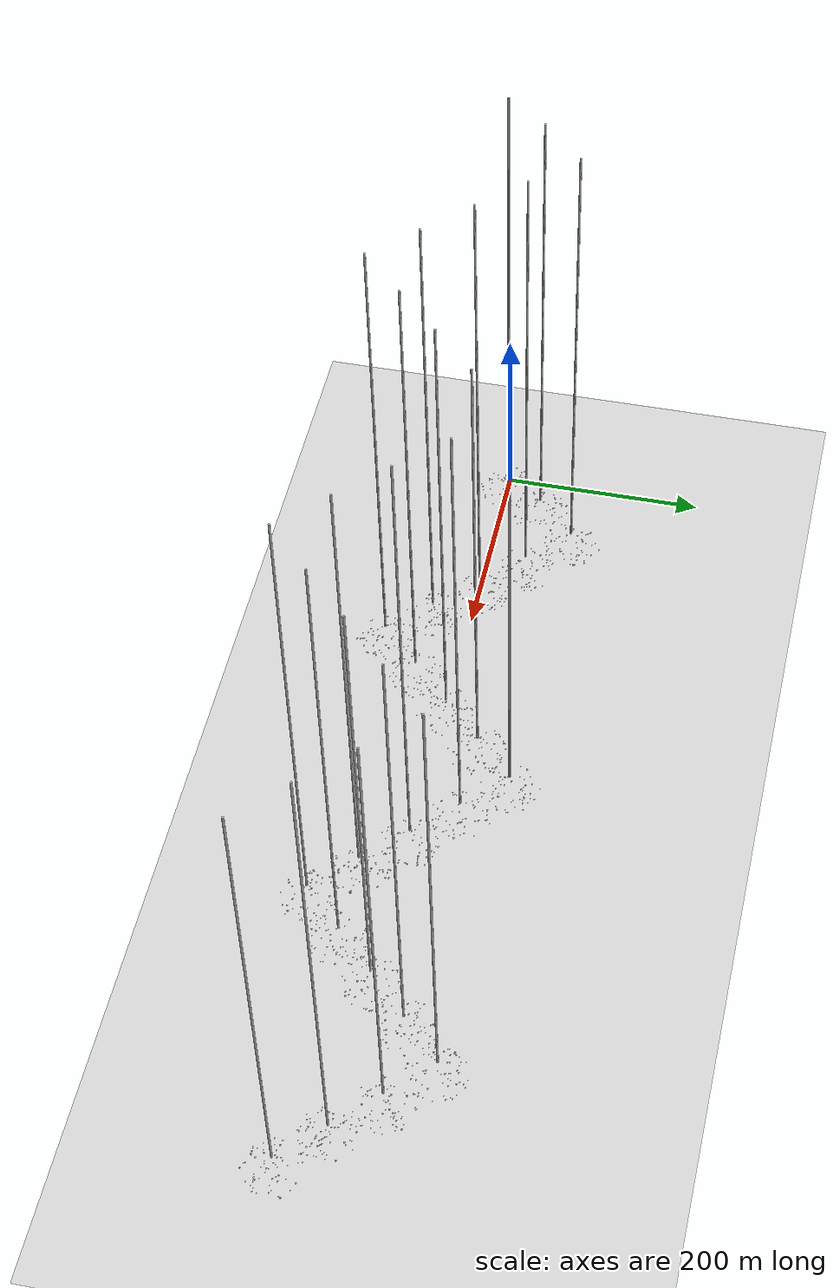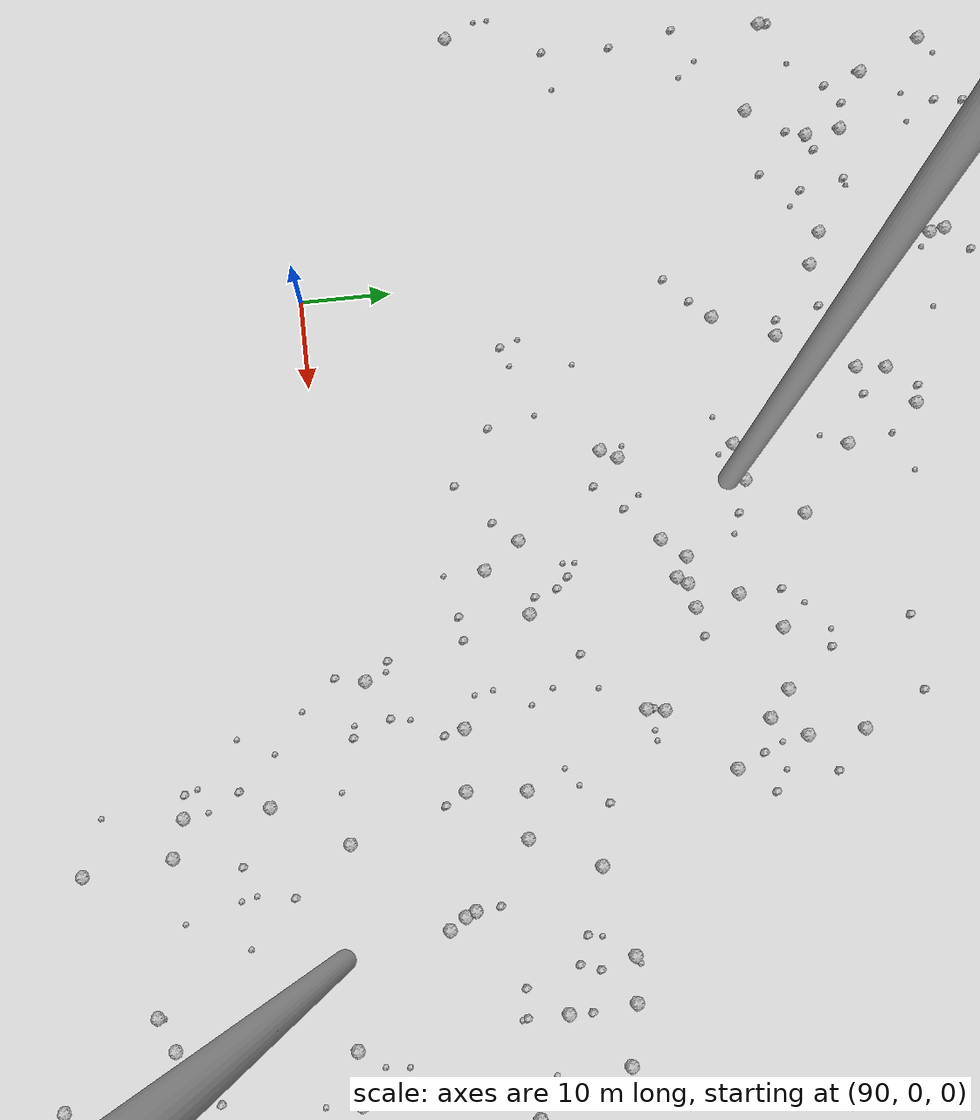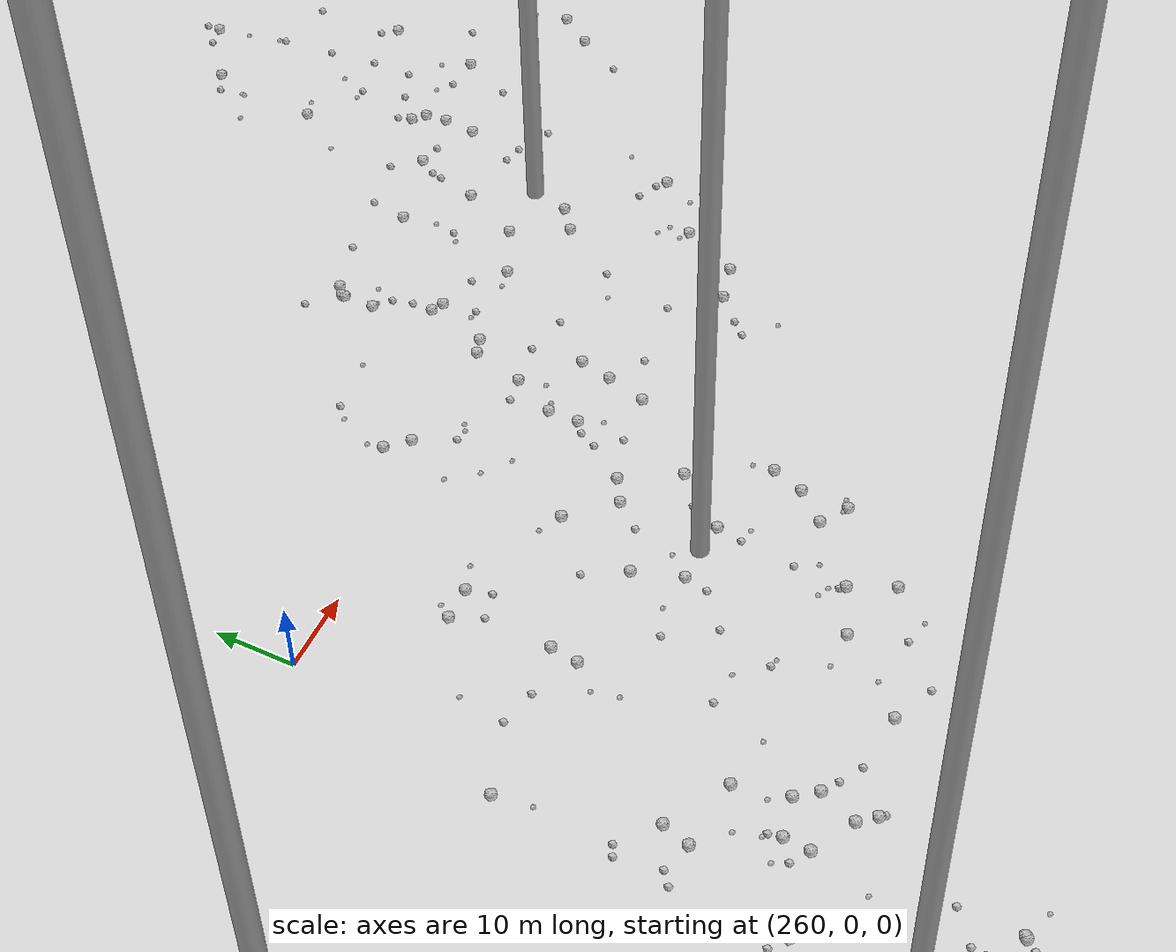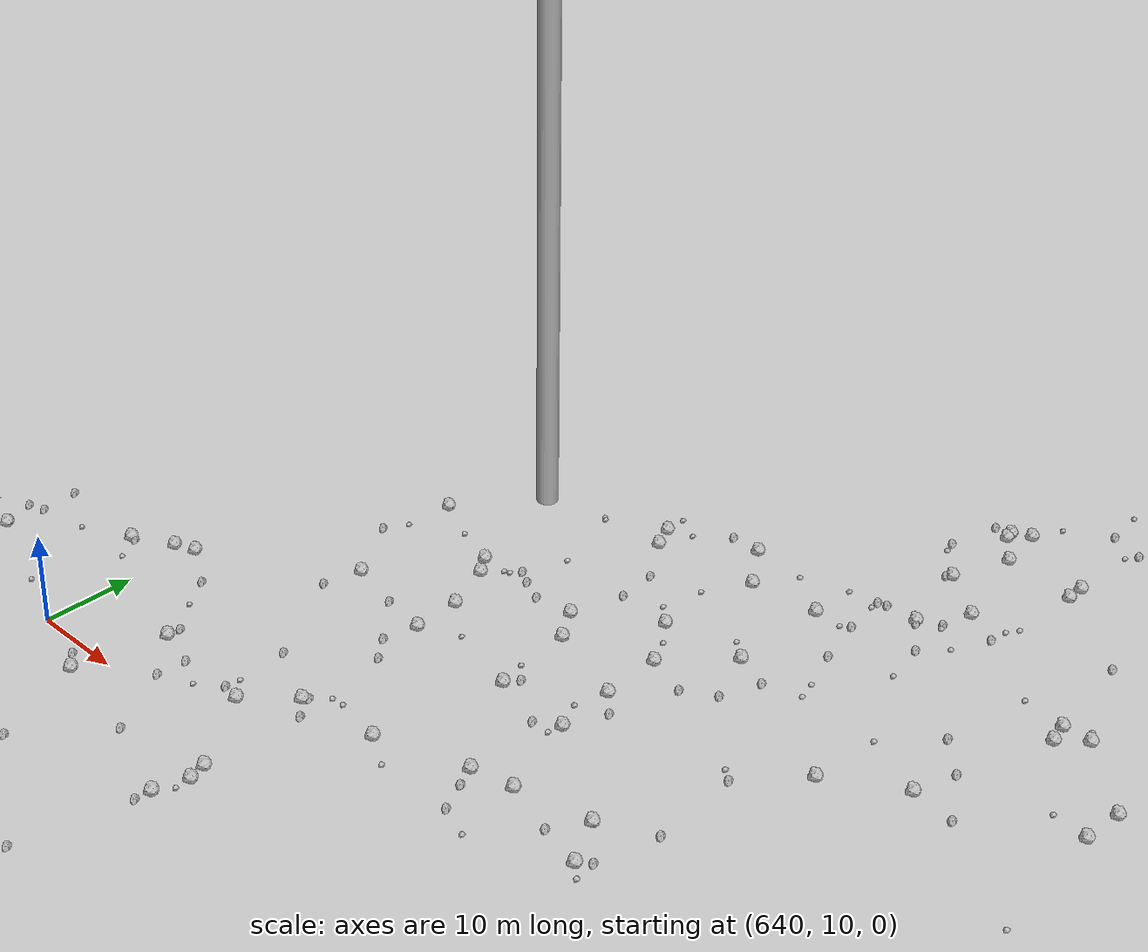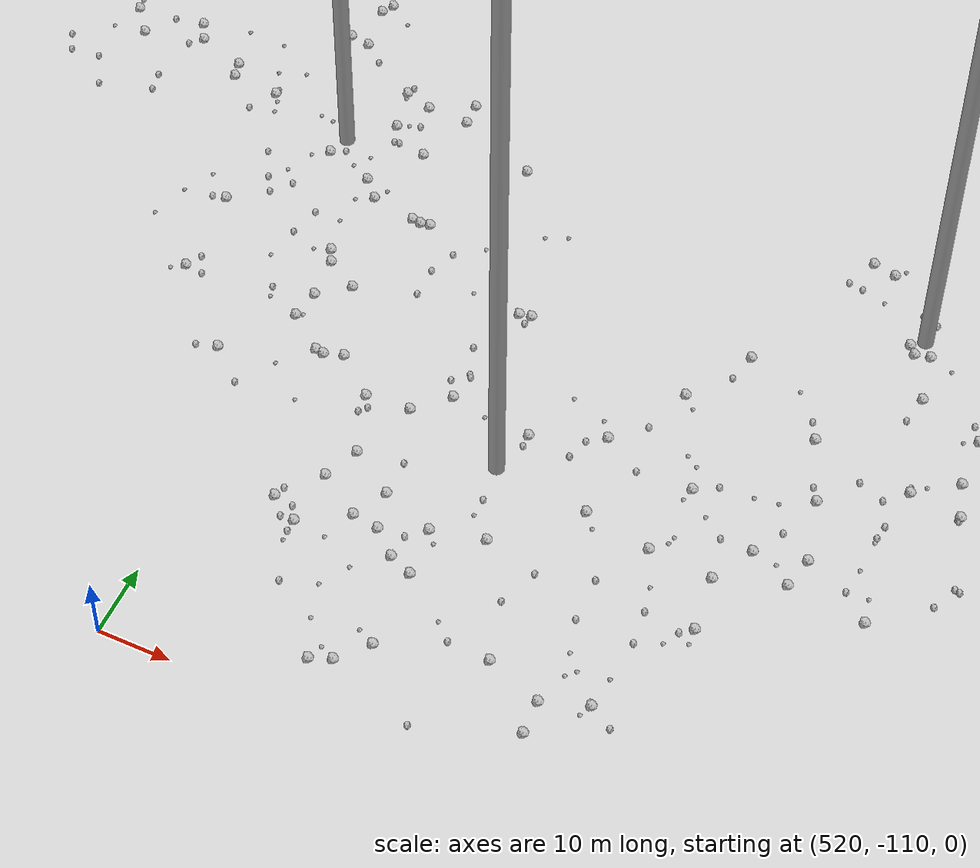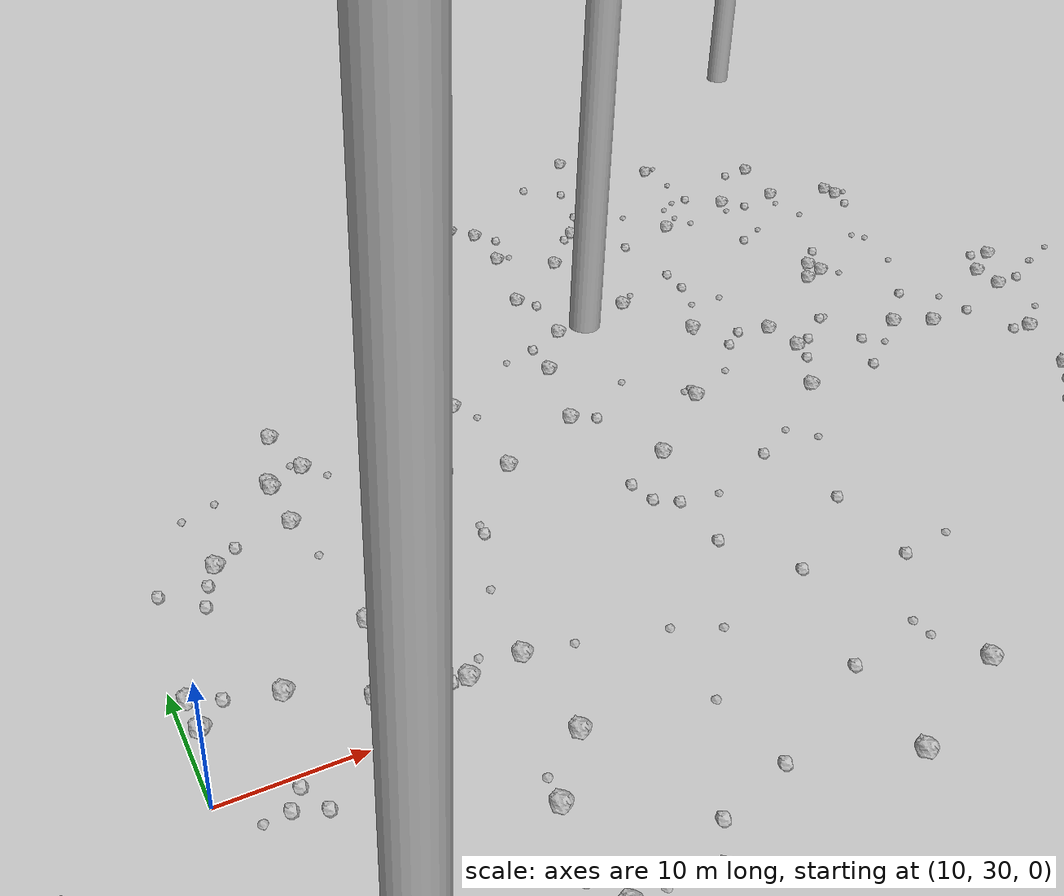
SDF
<sdf version="1.6">
 <world name="default">
  <include><uri>model://custom_ground</uri></include>
  <include><uri>model://sun</uri></include>
  <spherical_coordinates>
   <surface_model>EARTH_WGS84</surface_model>
   <latitude_deg>38.161479</latitude_deg>
   <longitude_deg>-122.454630</longitude_deg>
   <elevation>488.0</elevation>
   <heading_deg>90</heading_deg>
  </spherical_coordinates>
  <model name="rock1_0_0">
   <include><uri>model://rock1</uri><pose>14.795688683390786 -27.14831153094539 0.5 0 0 0</pose></include>
  </model>
  <model name="rock1_0_1">
   <include><uri>model://rock1</uri><pose>-1.706923984978932 10.54316519346279 0.5 0 0 0</pose></include>
  </model>
  <model name="rock1_0_2">
   <include><uri>model://rock1</uri><pose>36.20986750086257 7.562524197066146 0.5 0 0 0</pose></include>
  </model>
  <model name="rock1_0_3">
   <include><uri>model://rock1</uri><pose>-10.713392223705311 -1.8791601486154157 0.5 0 0 0</pose></include>
  </model>
  <model name="rock1_0_4">
   <include><uri>model://rock1</uri><pose>29.83726147053168 -21.61384395769337 0.5 0 0 0</pose></include>
  </model>
  <model name="rock1_0_5">
   <include><uri>model://rock1</uri><pose>19.894158736887007 -25.55735908063849 0.5 0 0 0</pose></include>
  </model>
  <model name="rock1_0_6">
   <include><uri>model://rock1</uri><pose>-6.229414679989398 8.862673283574942 0.5 0 0 0</pose></include>
  </model>
  <model name="rock1_0_7">
   <include><uri>model://rock1</uri><pose>28.392063431559578 21.204259694937107 0.5 0 0 0</pose></include>
  </model>
  <model name="rock1_0_8">
   <include><uri>model://rock1</uri><pose>-17.799776795680394 2.9973066329254223 0.5 0 0 0</pose></include>
  </model>
  <model name="rock1_0_9">
   <include><uri>model://rock1</uri><pose>-5.908799949721605 -19.581848003338365 0.5 0 0 0</pose></include>
  </model>
  <model name="rock1_0_10">
   <include><uri>model://rock1</uri><pose>0.5131681898043041 -13.494313717414727 0.5 0 0 0</pose></include>
  </model>
  <model name="rock1_0_11">
   <include><uri>model://rock1</uri><pose>-7.65340110197357 14.214385039071452 0.5 0 0 0</pose></include>
  </model>
  <model name="rock1_0_12">
   <include><uri>model://rock1</uri><pose>3.4089803754233827 -19.387710017260467 0.5 0 0 0</pose></include>
  </model>
  <model name="rock1_0_13">
   <include><uri>model://rock1</uri><pose>17.46791862944231 -18.244187734937878 0.5 0 0 0</pose></include>
  </model>
  <model name="rock1_0_14">
   <include><uri>model://rock1</uri><pose>32.79111083680419 1.2136669253837447 0.5 0 0 0</pose></include>
  </model>
  <model name="rock1_0_15">
   <include><uri>model://rock1</uri><pose>3.6267212202863632 -22.204231125626556 0.5 0 0 0</pose></include>
  </model>
  <model name="rock1_0_16">
   <include><uri>model://rock1</uri><pose>-5.364685814052528 -5.796391277258994 0.5 0 0 0</pose></include>
  </model>
  <model name="rock1_0_17">
   <include><uri>model://rock1</uri><pose>37.54391801237864 -11.596988959542134 0.5 0 0 0</pose></include>
  </model>
  <model name="rock1_0_18">
   <include><uri>model://rock1</uri><pose>-0.02281137222828633 -5.832264107584418 0.5 0 0 0</pose></include>
  </model>
  <model name="rock1_0_19">
   <include><uri>model://rock1</uri><pose>-5.224102922806127 11.451152772141818 0.5 0 0 0</pose></include>
  </model>
  <model name="rock1_0_20">
   <include><uri>model://rock1</uri><pose>-14.392712700027307 12.375875733089572 0.5 0 0 0</pose></include>
  </model>
  <model name="rock1_0_21">
   <include><uri>model://rock1</uri><pose>34.259506624269854 13.259453446502015 0.5 0 0 0</pose></include>
  </model>
  <model name="rock1_0_22">
   <include><uri>model://rock1</uri><pose>-8.866061724749766 9.345519450801802 0.5 0 0 0</pose></include>
  </model>
  <model name="rock1_0_23">
   <include><uri>model://rock1</uri><pose>20.518652755957582 3.233255584255005 0.5 0 0 0</pose></include>
  </model>
  <model name="rock1_0_24">
   <include><uri>model://rock1</uri><pose>18.207017896352333 21.315539076022574 0.5 0 0 0</pose></include>
  </model>
  <model name="rock1_0_25">
   <include><uri>model://rock1</uri><pose>2.038212884898172 -9.548987793975243 0.5 0 0 0</pose></include>
  </model>
  <model name="rock1_0_26">
   <include><uri>model://rock1</uri><pose>14.576690317029971 -4.447202481016223 0.5 0 0 0</pose></include>
  </model>
  <model name="rock2_0_0">
   <include><uri>model://rock2</uri><pose>-15.495539327728654 13.72186803700773 0.3 0 0 0</pose></include>
  </model>
  <model name="rock2_0_1">
   <include><uri>model://rock2</uri><pose>-17.07786166035204 -2.177265013467583 0.3 0 0 0</pose></include>
  </model>
  <model name="rock2_0_2">
   <include><uri>model://rock2</uri><pose>-14.713261614766246 -6.905199923018525 0.3 0 0 0</pose></include>
  </model>
  <model name="rock2_0_3">
   <include><uri>model://rock2</uri><pose>29.59546967933717 6.622737036477034 0.3 0 0 0</pose></include>
  </model>
  <model name="rock2_0_4">
   <include><uri>model://rock2</uri><pose>26.65429321618496 -21.744105184793405 0.3 0 0 0</pose></include>
  </model>
  <model name="rock2_0_5">
   <include><uri>model://rock2</uri><pose>7.4866258079092844 -18.212374485888645 0.3 0 0 0</pose></include>
  </model>
  <model name="rock2_0_6">
   <include><uri>model://rock2</uri><pose>8.604302659276083 -18.691747580249093 0.3 0 0 0</pose></include>
  </model>
  <model name="rock2_0_7">
   <include><uri>model://rock2</uri><pose>-9.563496964097551 15.309334300634305 0.3 0 0 0</pose></include>
  </model>
  <model name="rock2_0_8">
   <include><uri>model://rock2</uri><pose>15.145062004081588 29.061500034053708 0.3 0 0 0</pose></include>
  </model>
  <model name="rock2_0_9">
   <include><uri>model://rock2</uri><pose>18.801502723570543 -2.8233461534695117 0.3 0 0 0</pose></include>
  </model>
  <model name="rock2_0_10">
   <include><uri>model://rock2</uri><pose>1.5478529824665728 17.487551332967023 0.3 0 0 0</pose></include>
  </model>
  <model name="rock2_0_11">
   <include><uri>model://rock2</uri><pose>22.111100406113216 -7.2857802767124795 0.3 0 0 0</pose></include>
  </model>
  <model name="rock2_0_12">
   <include><uri>model://rock2</uri><pose>2.775841824752355 -7.326171847166343 0.3 0 0 0</pose></include>
  </model>
  <model name="rock2_0_13">
   <include><uri>model://rock2</uri><pose>-11.804403164181142 -14.675511997451284 0.3 0 0 0</pose></include>
  </model>
  <model name="rock2_0_14">
   <include><uri>model://rock2</uri><pose>19.715574235479714 -23.027488576152663 0.3 0 0 0</pose></include>
  </model>
  <model name="rock2_0_15">
   <include><uri>model://rock2</uri><pose>1.0558459031988612 24.99869160586244 0.3 0 0 0</pose></include>
  </model>
  <model name="rock2_0_16">
   <include><uri>model://rock2</uri><pose>-1.6252476968933003 -18.635608495968803 0.3 0 0 0</pose></include>
  </model>
  <model name="rock2_0_17">
   <include><uri>model://rock2</uri><pose>7.682084450049903 6.546321689420687 0.3 0 0 0</pose></include>
  </model>
  <model name="rock2_0_18">
   <include><uri>model://rock2</uri><pose>-2.2730771636869065 22.206646742545587 0.3 0 0 0</pose></include>
  </model>
  <model name="rock2_0_19">
   <include><uri>model://rock2</uri><pose>16.299728585252865 17.32045418123102 0.3 0 0 0</pose></include>
  </model>
  <model name="rock2_0_20">
   <include><uri>model://rock2</uri><pose>-13.552973471628631 9.087609601746152 0.3 0 0 0</pose></include>
  </model>
  <model name="rock2_0_21">
   <include><uri>model://rock2</uri><pose>24.041274496314948 -2.580237962663869 0.3 0 0 0</pose></include>
  </model>
  <model name="rock2_0_22">
   <include><uri>model://rock2</uri><pose>25.176981679820102 -15.330700207320437 0.3 0 0 0</pose></include>
  </model>
  <model name="rock2_0_23">
   <include><uri>model://rock2</uri><pose>-2.2752091433756263 -7.214180567994436 0.3 0 0 0</pose></include>
  </model>
  <model name="rock2_0_24">
   <include><uri>model://rock2</uri><pose>2.2608710360577007 -22.33759468981564 0.3 0 0 0</pose></include>
  </model>
  <model name="rock2_0_25">
   <include><uri>model://rock2</uri><pose>12.863975242542452 17.60222061896294 0.3 0 0 0</pose></include>
  </model>
  <model name="rock2_0_26">
   <include><uri>model://rock2</uri><pose>5.405452038079389 -22.029889060629323 0.3 0 0 0</pose></include>
  </model>
  <model name="rock3_0_0">
   <include><uri>model://rock3</uri><pose>3.0929600748753607 -7.819294703740191 0.2 0 0 0</pose></include>
  </model>
  <model name="rock3_0_1">
   <include><uri>model://rock3</uri><pose>35.72202980289187 -8.90646304234933 0.2 0 0 0</pose></include>
  </model>
  <model name="rock3_0_2">
   <include><uri>model://rock3</uri><pose>30.459421266073115 -17.299967465898607 0.2 0 0 0</pose></include>
  </model>
  <model name="rock3_0_3">
   <include><uri>model://rock3</uri><pose>-10.21954911992826 10.571860247155449 0.2 0 0 0</pose></include>
  </model>
  <model name="rock3_0_4">
   <include><uri>model://rock3</uri><pose>-16.1975670104704 7.797067646857933 0.2 0 0 0</pose></include>
  </model>
  <model name="rock3_0_5">
   <include><uri>model://rock3</uri><pose>15.470084045548099 11.642554874691001 0.2 0 0 0</pose></include>
  </model>
  <model name="rock3_0_6">
   <include><uri>model://rock3</uri><pose>-13.32084018999115 -4.050760291532786 0.2 0 0 0</pose></include>
  </model>
  <model name="rock3_0_7">
   <include><uri>model://rock3</uri><pose>20.62061421803992 -21.6032215973704 0.2 0 0 0</pose></include>
  </model>
  <model name="rock3_0_8">
   <include><uri>model://rock3</uri><pose>11.570854243627142 -29.087021737699022 0.2 0 0 0</pose></include>
  </model>
  <model name="rock3_0_9">
   <include><uri>model://rock3</uri><pose>1.7761193775469266 15.21858443852964 0.2 0 0 0</pose></include>
  </model>
  <model name="rock3_0_10">
   <include><uri>model://rock3</uri><pose>-4.318010584438653 -14.586683998507139 0.2 0 0 0</pose></include>
  </model>
  <model name="rock3_0_11">
   <include><uri>model://rock3</uri><pose>36.863085180940395 -13.261443660285249 0.2 0 0 0</pose></include>
  </model>
  <model name="rock3_0_12">
   <include><uri>model://rock3</uri><pose>4.354808618254516 19.527620026959113 0.2 0 0 0</pose></include>
  </model>
  <model name="rock3_0_13">
   <include><uri>model://rock3</uri><pose>-5.86892846807778 13.511710535619606 0.2 0 0 0</pose></include>
  </model>
  <model name="rock3_0_14">
   <include><uri>model://rock3</uri><pose>28.35077235400132 -2.571360793787754 0.2 0 0 0</pose></include>
  </model>
  <model name="rock3_0_15">
   <include><uri>model://rock3</uri><pose>12.319542586631641 27.470413714025945 0.2 0 0 0</pose></include>
  </model>
  <model name="rock3_0_16">
   <include><uri>model://rock3</uri><pose>-0.09806107476541115 5.5819427789004195 0.2 0 0 0</pose></include>
  </model>
  <model name="rock3_0_17">
   <include><uri>model://rock3</uri><pose>16.098115500979027 -3.0695586189147193 0.2 0 0 0</pose></include>
  </model>
  <model name="rock3_0_18">
   <include><uri>model://rock3</uri><pose>0.8649799179344093 27.45947377888725 0.2 0 0 0</pose></include>
  </model>
  <model name="rock3_0_19">
   <include><uri>model://rock3</uri><pose>-17.036343933529977 11.461713616488872 0.2 0 0 0</pose></include>
  </model>
  <model name="rock3_0_20">
   <include><uri>model://rock3</uri><pose>11.866864152873639 -3.8354137035608744 0.2 0 0 0</pose></include>
  </model>
  <model name="rock3_0_21">
   <include><uri>model://rock3</uri><pose>27.23349567277974 -15.640275342821738 0.2 0 0 0</pose></include>
  </model>
  <model name="rock3_0_22">
   <include><uri>model://rock3</uri><pose>3.5139568090347986 -21.468368377721514 0.2 0 0 0</pose></include>
  </model>
  <model name="rock3_0_23">
   <include><uri>model://rock3</uri><pose>16.800087873566675 -27.6458201842805 0.2 0 0 0</pose></include>
  </model>
  <model name="rock3_0_24">
   <include><uri>model://rock3</uri><pose>6.799011198940967 9.227520631842431 0.2 0 0 0</pose></include>
  </model>
  <model name="rock3_0_25">
   <include><uri>model://rock3</uri><pose>27.80600707217969 1.1737332141767176 0.2 0 0 0</pose></include>
  </model>
  <model name="rock3_0_26">
   <include><uri>model://rock3</uri><pose>-0.2728612256059435 21.03235328903454 0.2 0 0 0</pose></include>
  </model>
  <model name="rock1_1_0">
   <include><uri>model://rock1</uri><pose>23.16917806599867 58.95503365596117 0.5 0 0 0</pose></include>
  </model>
  <model name="rock1_1_1">
   <include><uri>model://rock1</uri><pose>41.769441717428165 52.810396076441926 0.5 0 0 0</pose></include>
  </model>
  <model name="rock1_1_2">
   <include><uri>model://rock1</uri><pose>26.385668367615388 59.91984490802601 0.5 0 0 0</pose></include>
  </model>
  <model name="rock1_1_3">
   <include><uri>model://rock1</uri><pose>32.268033143126075 33.02259215051849 0.5 0 0 0</pose></include>
  </model>
  <model name="rock1_1_4">
   <include><uri>model://rock1</uri><pose>21.936995749031247 33.72183625072573 0.5 0 0 0</pose></include>
  </model>
  <model name="rock1_1_5">
   <include><uri>model://rock1</uri><pose>16.765588618863738 36.660054734718315 0.5 0 0 0</pose></include>
  </model>
  <model name="rock1_1_6">
   <include><uri>model://rock1</uri><pose>11.066877147473438 35.92806499304362 0.5 0 0 0</pose></include>
  </model>
  <model name="rock1_1_7">
   <include><uri>model://rock1</uri><pose>23.190799083548484 58.25153017433064 0.5 0 0 0</pose></include>
  </model>
  <model name="rock1_1_8">
   <include><uri>model://rock1</uri><pose>11.017567999562992 38.576476592869305 0.5 0 0 0</pose></include>
  </model>
  <model name="rock1_1_9">
   <include><uri>model://rock1</uri><pose>28.10007914852126 32.64417099601107 0.5 0 0 0</pose></include>
  </model>
  <model name="rock1_1_10">
   <include><uri>model://rock1</uri><pose>32.28638030646984 25.597253553172266 0.5 0 0 0</pose></include>
  </model>
  <model name="rock1_1_11">
   <include><uri>model://rock1</uri><pose>62.12861810536877 55.159545892254755 0.5 0 0 0</pose></include>
  </model>
  <model name="rock1_1_12">
   <include><uri>model://rock1</uri><pose>23.14274993144547 53.365554564731625 0.5 0 0 0</pose></include>
  </model>
  <model name="rock1_1_13">
   <include><uri>model://rock1</uri><pose>50.038526514188895 56.84512710442398 0.5 0 0 0</pose></include>
  </model>
  <model name="rock1_1_14">
   <include><uri>model://rock1</uri><pose>25.341141356310406 65.17875993008593 0.5 0 0 0</pose></include>
  </model>
  <model name="rock1_1_15">
   <include><uri>model://rock1</uri><pose>23.1772937430421 31.215363954111904 0.5 0 0 0</pose></include>
  </model>
  <model name="rock1_1_16">
   <include><uri>model://rock1</uri><pose>60.20479711750749 19.159849661563655 0.5 0 0 0</pose></include>
  </model>
  <model name="rock1_1_17">
   <include><uri>model://rock1</uri><pose>50.497703506835364 15.058374393765133 0.5 0 0 0</pose></include>
  </model>
  <model name="rock1_1_18">
   <include><uri>model://rock1</uri><pose>30.673850412928005 53.51182246088657 0.5 0 0 0</pose></include>
  </model>
  <model name="rock1_1_19">
   <include><uri>model://rock1</uri><pose>28.373048881102076 13.814170839961843 0.5 0 0 0</pose></include>
  </model>
  <model name="rock1_1_20">
   <include><uri>model://rock1</uri><pose>16.387901483744177 50.76458313217134 0.5 0 0 0</pose></include>
  </model>
  <model name="rock1_1_21">
   <include><uri>model://rock1</uri><pose>18.270618568423686 19.815317669299183 0.5 0 0 0</pose></include>
  </model>
  <model name="rock1_1_22">
   <include><uri>model://rock1</uri><pose>41.520421687526145 62.90293716179329 0.5 0 0 0</pose></include>
  </model>
  <model name="rock1_1_23">
   <include><uri>model://rock1</uri><pose>54.273421365135235 48.85113210572209 0.5 0 0 0</pose></include>
  </model>
  <model name="rock1_1_24">
   <include><uri>model://rock1</uri><pose>31.259897802368453 51.738054988839586 0.5 0 0 0</pose></include>
  </model>
  <model name="rock1_1_25">
   <include><uri>model://rock1</uri><pose>52.48488435903323 64.89704599906645 0.5 0 0 0</pose></include>
  </model>
  <model name="rock1_1_26">
   <include><uri>model://rock1</uri><pose>24.182907434421242 40.61576723668887 0.5 0 0 0</pose></include>
  </model>
  <model name="rock2_1_0">
   <include><uri>model://rock2</uri><pose>15.278033020343297 48.94795535120945 0.3 0 0 0</pose></include>
  </model>
  <model name="rock2_1_1">
   <include><uri>model://rock2</uri><pose>27.093206706309154 46.04442298770584 0.3 0 0 0</pose></include>
  </model>
  <model name="rock2_1_2">
   <include><uri>model://rock2</uri><pose>34.916553189076325 67.73319667326588 0.3 0 0 0</pose></include>
  </model>
  <model name="rock2_1_3">
   <include><uri>model://rock2</uri><pose>11.745645008806553 49.31560742459806 0.3 0 0 0</pose></include>
  </model>
  <model name="rock2_1_4">
   <include><uri>model://rock2</uri><pose>26.85820054046407 32.81823160863458 0.3 0 0 0</pose></include>
  </model>
  <model name="rock2_1_5">
   <include><uri>model://rock2</uri><pose>18.303255126926636 52.29276696493431 0.3 0 0 0</pose></include>
  </model>
  <model name="rock2_1_6">
   <include><uri>model://rock2</uri><pose>61.70635201826482 45.11295150164874 0.3 0 0 0</pose></include>
  </model>
  <model name="rock2_1_7">
   <include><uri>model://rock2</uri><pose>49.764753658401254 43.757794591513374 0.3 0 0 0</pose></include>
  </model>
  <model name="rock2_1_8">
   <include><uri>model://rock2</uri><pose>51.314074911484866 37.30690355771692 0.3 0 0 0</pose></include>
  </model>
  <model name="rock2_1_9">
   <include><uri>model://rock2</uri><pose>42.02377010305634 17.974480070069724 0.3 0 0 0</pose></include>
  </model>
  <model name="rock2_1_10">
   <include><uri>model://rock2</uri><pose>63.138954554208105 37.726185249364924 0.3 0 0 0</pose></include>
  </model>
  <model name="rock2_1_11">
   <include><uri>model://rock2</uri><pose>24.853265389341352 33.54491036329445 0.3 0 0 0</pose></include>
  </model>
  <model name="rock2_1_12">
   <include><uri>model://rock2</uri><pose>54.822279935374546 31.89712796382808 0.3 0 0 0</pose></include>
  </model>
  <model name="rock2_1_13">
   <include><uri>model://rock2</uri><pose>52.04604206070739 55.88354324054196 0.3 0 0 0</pose></include>
  </model>
  <model name="rock2_1_14">
   <include><uri>model://rock2</uri><pose>13.028932649019406 37.81727608014744 0.3 0 0 0</pose></include>
  </model>
  <model name="rock2_1_15">
   <include><uri>model://rock2</uri><pose>62.93785905828035 29.99922202267827 0.3 0 0 0</pose></include>
  </model>
  <model name="rock2_1_16">
   <include><uri>model://rock2</uri><pose>26.97677582778527 16.276539400523216 0.3 0 0 0</pose></include>
  </model>
  <model name="rock2_1_17">
   <include><uri>model://rock2</uri><pose>14.522381687053672 46.850752540662775 0.3 0 0 0</pose></include>
  </model>
  <model name="rock2_1_18">
   <include><uri>model://rock2</uri><pose>36.19903594650701 16.276018293555857 0.3 0 0 0</pose></include>
  </model>
  <model name="rock2_1_19">
   <include><uri>model://rock2</uri><pose>14.0814162000261 27.634443688079973 0.3 0 0 0</pose></include>
  </model>
  <model name="rock2_1_20">
   <include><uri>model://rock2</uri><pose>51.50495029797018 22.567941023164646 0.3 0 0 0</pose></include>
  </model>
  <model name="rock2_1_21">
   <include><uri>model://rock2</uri><pose>35.835696709426365 45.71993024918394 0.3 0 0 0</pose></include>
  </model>
  <model name="rock2_1_22">
   <include><uri>model://rock2</uri><pose>16.12421036733445 26.802220085957067 0.3 0 0 0</pose></include>
  </model>
  <model name="rock2_1_23">
   <include><uri>model://rock2</uri><pose>51.52852056387644 42.60301778040395 0.3 0 0 0</pose></include>
  </model>
  <model name="rock2_1_24">
   <include><uri>model://rock2</uri><pose>49.34689184422824 46.197995217504655 0.3 0 0 0</pose></include>
  </model>
  <model name="rock2_1_25">
   <include><uri>model://rock2</uri><pose>36.897016057064036 54.40333493763585 0.3 0 0 0</pose></include>
  </model>
  <model name="rock2_1_26">
   <include><uri>model://rock2</uri><pose>23.938480970074078 15.753764203413908 0.3 0 0 0</pose></include>
  </model>
  <model name="rock3_1_0">
   <include><uri>model://rock3</uri><pose>33.34634750617055 39.84255580845233 0.2 0 0 0</pose></include>
  </model>
  <model name="rock3_1_1">
   <include><uri>model://rock3</uri><pose>58.1674329395429 24.215775440837533 0.2 0 0 0</pose></include>
  </model>
  <model name="rock3_1_2">
   <include><uri>model://rock3</uri><pose>67.62030035464753 45.22621099702883 0.2 0 0 0</pose></include>
  </model>
  <model name="rock3_1_3">
   <include><uri>model://rock3</uri><pose>33.6835638917117 49.49491906688275 0.2 0 0 0</pose></include>
  </model>
  <model name="rock3_1_4">
   <include><uri>model://rock3</uri><pose>42.75062989169066 60.6087677873167 0.2 0 0 0</pose></include>
  </model>
  <model name="rock3_1_5">
   <include><uri>model://rock3</uri><pose>35.946547032240204 32.48652365464285 0.2 0 0 0</pose></include>
  </model>
  <model name="rock3_1_6">
   <include><uri>model://rock3</uri><pose>33.71227098866759 48.196080217956414 0.2 0 0 0</pose></include>
  </model>
  <model name="rock3_1_7">
   <include><uri>model://rock3</uri><pose>25.571765992638422 60.74606832381594 0.2 0 0 0</pose></include>
  </model>
  <model name="rock3_1_8">
   <include><uri>model://rock3</uri><pose>49.50429347322947 67.86089040531127 0.2 0 0 0</pose></include>
  </model>
  <model name="rock3_1_9">
   <include><uri>model://rock3</uri><pose>58.23600666225528 22.630519995081997 0.2 0 0 0</pose></include>
  </model>
  <model name="rock3_1_10">
   <include><uri>model://rock3</uri><pose>36.043929304655684 46.84309007645507 0.2 0 0 0</pose></include>
  </model>
  <model name="rock3_1_11">
   <include><uri>model://rock3</uri><pose>18.44294942380887 58.31646937965889 0.2 0 0 0</pose></include>
  </model>
  <model name="rock3_1_12">
   <include><uri>model://rock3</uri><pose>28.23858985335243 39.669334063727334 0.2 0 0 0</pose></include>
  </model>
  <model name="rock3_1_13">
   <include><uri>model://rock3</uri><pose>67.57487030786679 30.63592211007467 0.2 0 0 0</pose></include>
  </model>
  <model name="rock3_1_14">
   <include><uri>model://rock3</uri><pose>27.8640036382742 58.17247062101975 0.2 0 0 0</pose></include>
  </model>
  <model name="rock3_1_15">
   <include><uri>model://rock3</uri><pose>42.5820515407155 30.896837202149754 0.2 0 0 0</pose></include>
  </model>
  <model name="rock3_1_16">
   <include><uri>model://rock3</uri><pose>30.747667332770675 13.948696499976872 0.2 0 0 0</pose></include>
  </model>
  <model name="rock3_1_17">
   <include><uri>model://rock3</uri><pose>15.532164920898701 57.179226777369195 0.2 0 0 0</pose></include>
  </model>
  <model name="rock3_1_18">
   <include><uri>model://rock3</uri><pose>45.97466236176388 29.369509022646277 0.2 0 0 0</pose></include>
  </model>
  <model name="rock3_1_19">
   <include><uri>model://rock3</uri><pose>65.75850372978364 47.26752067267272 0.2 0 0 0</pose></include>
  </model>
  <model name="rock3_1_20">
   <include><uri>model://rock3</uri><pose>55.060588785327624 42.23599269705508 0.2 0 0 0</pose></include>
  </model>
  <model name="rock3_1_21">
   <include><uri>model://rock3</uri><pose>23.658218814260685 48.836982590855534 0.2 0 0 0</pose></include>
  </model>
  <model name="rock3_1_22">
   <include><uri>model://rock3</uri><pose>61.610058529495106 56.29008338505395 0.2 0 0 0</pose></include>
  </model>
  <model name="rock3_1_23">
   <include><uri>model://rock3</uri><pose>57.36174145013359 60.1730974712328 0.2 0 0 0</pose></include>
  </model>
  <model name="rock3_1_24">
   <include><uri>model://rock3</uri><pose>29.43897928929149 34.024730266540175 0.2 0 0 0</pose></include>
  </model>
  <model name="rock3_1_25">
   <include><uri>model://rock3</uri><pose>41.452307805209486 24.08356666192958 0.2 0 0 0</pose></include>
  </model>
  <model name="rock3_1_26">
   <include><uri>model://rock3</uri><pose>28.62536044917299 23.315075776430643 0.2 0 0 0</pose></include>
  </model>
  <model name="rock1_2_0">
   <include><uri>model://rock1</uri><pose>105.12219063487004 88.4717341192216 0.5 0 0 0</pose></include>
  </model>
  <model name="rock1_2_1">
   <include><uri>model://rock1</uri><pose>89.3786248602793 70.55640311813472 0.5 0 0 0</pose></include>
  </model>
  <model name="rock1_2_2">
   <include><uri>model://rock1</uri><pose>64.30775744606497 84.43951248641594 0.5 0 0 0</pose></include>
  </model>
  <model name="rock1_2_3">
   <include><uri>model://rock1</uri><pose>75.9763616476971 62.43447989015775 0.5 0 0 0</pose></include>
  </model>
  <model name="rock1_2_4">
   <include><uri>model://rock1</uri><pose>79.76957447794163 109.97504551143965 0.5 0 0 0</pose></include>
  </model>
  <model name="rock1_2_5">
   <include><uri>model://rock1</uri><pose>91.07193292762355 90.53278752689431 0.5 0 0 0</pose></include>
  </model>
  <model name="rock1_2_6">
   <include><uri>model://rock1</uri><pose>65.78791605932064 73.08345328981868 0.5 0 0 0</pose></include>
  </model>
  <model name="rock1_2_7">
   <include><uri>model://rock1</uri><pose>76.32458909833542 58.51950206437804 0.5 0 0 0</pose></include>
  </model>
  <model name="rock1_2_8">
   <include><uri>model://rock1</uri><pose>57.7259924319346 97.10018407231792 0.5 0 0 0</pose></include>
  </model>
  <model name="rock1_2_9">
   <include><uri>model://rock1</uri><pose>86.88293297123786 69.6374534833433 0.5 0 0 0</pose></include>
  </model>
  <model name="rock1_2_10">
   <include><uri>model://rock1</uri><pose>98.0040403934881 90.01944184289196 0.5 0 0 0</pose></include>
  </model>
  <model name="rock1_2_11">
   <include><uri>model://rock1</uri><pose>59.13934907277906 88.09379772642885 0.5 0 0 0</pose></include>
  </model>
  <model name="rock1_2_12">
   <include><uri>model://rock1</uri><pose>91.79149141554103 56.621878212440215 0.5 0 0 0</pose></include>
  </model>
  <model name="rock1_2_13">
   <include><uri>model://rock1</uri><pose>88.11354913176145 58.21618638606446 0.5 0 0 0</pose></include>
  </model>
  <model name="rock1_2_14">
   <include><uri>model://rock1</uri><pose>105.31022625376954 86.74111295387294 0.5 0 0 0</pose></include>
  </model>
  <model name="rock1_2_15">
   <include><uri>model://rock1</uri><pose>88.26158218705774 102.88417962027378 0.5 0 0 0</pose></include>
  </model>
  <model name="rock1_2_16">
   <include><uri>model://rock1</uri><pose>71.8085035127649 91.581156126922 0.5 0 0 0</pose></include>
  </model>
  <model name="rock1_2_17">
   <include><uri>model://rock1</uri><pose>69.299107709541 65.83840954658507 0.5 0 0 0</pose></include>
  </model>
  <model name="rock1_2_18">
   <include><uri>model://rock1</uri><pose>100.3050648694267 97.94064006867617 0.5 0 0 0</pose></include>
  </model>
  <model name="rock1_2_19">
   <include><uri>model://rock1</uri><pose>89.07307557194925 72.2536054952814 0.5 0 0 0</pose></include>
  </model>
  <model name="rock1_2_20">
   <include><uri>model://rock1</uri><pose>72.68769171602416 52.11487801222323 0.5 0 0 0</pose></include>
  </model>
  <model name="rock1_2_21">
   <include><uri>model://rock1</uri><pose>59.724860981383294 94.72879832683122 0.5 0 0 0</pose></include>
  </model>
  <model name="rock1_2_22">
   <include><uri>model://rock1</uri><pose>104.50043940781504 63.12353083816058 0.5 0 0 0</pose></include>
  </model>
  <model name="rock1_2_23">
   <include><uri>model://rock1</uri><pose>56.406969027556755 78.45115230250043 0.5 0 0 0</pose></include>
  </model>
  <model name="rock1_2_24">
   <include><uri>model://rock1</uri><pose>69.99770694548553 90.4734046247952 0.5 0 0 0</pose></include>
  </model>
  <model name="rock1_2_25">
   <include><uri>model://rock1</uri><pose>80.82197387062398 87.2480651967665 0.5 0 0 0</pose></include>
  </model>
  <model name="rock1_2_26">
   <include><uri>model://rock1</uri><pose>56.851915770791976 70.73002247075752 0.5 0 0 0</pose></include>
  </model>
  <model name="rock2_2_0">
   <include><uri>model://rock2</uri><pose>91.75456087630494 74.86026504483533 0.3 0 0 0</pose></include>
  </model>
  <model name="rock2_2_1">
   <include><uri>model://rock2</uri><pose>87.65439481310347 93.38419836277802 0.3 0 0 0</pose></include>
  </model>
  <model name="rock2_2_2">
   <include><uri>model://rock2</uri><pose>78.10039257336378 59.19389467963419 0.3 0 0 0</pose></include>
  </model>
  <model name="rock2_2_3">
   <include><uri>model://rock2</uri><pose>75.6103985798468 56.3615478032569 0.3 0 0 0</pose></include>
  </model>
  <model name="rock2_2_4">
   <include><uri>model://rock2</uri><pose>57.65774811252511 76.7307785086277 0.3 0 0 0</pose></include>
  </model>
  <model name="rock2_2_5">
   <include><uri>model://rock2</uri><pose>82.83817852086457 56.95799795395201 0.3 0 0 0</pose></include>
  </model>
  <model name="rock2_2_6">
   <include><uri>model://rock2</uri><pose>78.54827555304068 101.62204272114184 0.3 0 0 0</pose></include>
  </model>
  <model name="rock2_2_7">
   <include><uri>model://rock2</uri><pose>71.27299615164327 104.39627631218944 0.3 0 0 0</pose></include>
  </model>
  <model name="rock2_2_8">
   <include><uri>model://rock2</uri><pose>96.5878166333319 56.94296275908931 0.3 0 0 0</pose></include>
  </model>
  <model name="rock2_2_9">
   <include><uri>model://rock2</uri><pose>74.80162514601612 101.35279310991194 0.3 0 0 0</pose></include>
  </model>
  <model name="rock2_2_10">
   <include><uri>model://rock2</uri><pose>68.43366326989675 89.59338582210759 0.3 0 0 0</pose></include>
  </model>
  <model name="rock2_2_11">
   <include><uri>model://rock2</uri><pose>61.27072475244081 92.67863785329999 0.3 0 0 0</pose></include>
  </model>
  <model name="rock2_2_12">
   <include><uri>model://rock2</uri><pose>73.80674112968742 76.97538041091171 0.3 0 0 0</pose></include>
  </model>
  <model name="rock2_2_13">
   <include><uri>model://rock2</uri><pose>104.40509752693669 84.05338254193937 0.3 0 0 0</pose></include>
  </model>
  <model name="rock2_2_14">
   <include><uri>model://rock2</uri><pose>72.74263467805825 94.72518406149635 0.3 0 0 0</pose></include>
  </model>
  <model name="rock2_2_15">
   <include><uri>model://rock2</uri><pose>73.46989493243065 73.77393759591821 0.3 0 0 0</pose></include>
  </model>
  <model name="rock2_2_16">
   <include><uri>model://rock2</uri><pose>62.21871867748537 56.21165459594315 0.3 0 0 0</pose></include>
  </model>
  <model name="rock2_2_17">
   <include><uri>model://rock2</uri><pose>96.80738488346589 97.61956462166756 0.3 0 0 0</pose></include>
  </model>
  <model name="rock2_2_18">
   <include><uri>model://rock2</uri><pose>52.862216733391804 68.864937375514 0.3 0 0 0</pose></include>
  </model>
  <model name="rock2_2_19">
   <include><uri>model://rock2</uri><pose>72.76845951337256 63.21931130982888 0.3 0 0 0</pose></include>
  </model>
  <model name="rock2_2_20">
   <include><uri>model://rock2</uri><pose>81.88729550120819 62.011471329576885 0.3 0 0 0</pose></include>
  </model>
  <model name="rock2_2_21">
   <include><uri>model://rock2</uri><pose>80.45608393720016 52.686155208843324 0.3 0 0 0</pose></include>
  </model>
  <model name="rock2_2_22">
   <include><uri>model://rock2</uri><pose>70.46427484972165 61.56820705813994 0.3 0 0 0</pose></include>
  </model>
  <model name="rock2_2_23">
   <include><uri>model://rock2</uri><pose>93.08361497228964 62.772374250530774 0.3 0 0 0</pose></include>
  </model>
  <model name="rock2_2_24">
   <include><uri>model://rock2</uri><pose>86.76500654889429 80.59518681914665 0.3 0 0 0</pose></include>
  </model>
  <model name="rock2_2_25">
   <include><uri>model://rock2</uri><pose>73.56120518513441 84.79721028005028 0.3 0 0 0</pose></include>
  </model>
  <model name="rock2_2_26">
   <include><uri>model://rock2</uri><pose>92.91692090946523 88.57904392162087 0.3 0 0 0</pose></include>
  </model>
  <model name="rock3_2_0">
   <include><uri>model://rock3</uri><pose>76.68843769881555 58.40541256546863 0.2 0 0 0</pose></include>
  </model>
  <model name="rock3_2_1">
   <include><uri>model://rock3</uri><pose>97.01273857522966 87.82985163383262 0.2 0 0 0</pose></include>
  </model>
  <model name="rock3_2_2">
   <include><uri>model://rock3</uri><pose>90.23714911039922 88.53633058213387 0.2 0 0 0</pose></include>
  </model>
  <model name="rock3_2_3">
   <include><uri>model://rock3</uri><pose>83.3953200807898 89.44109683588209 0.2 0 0 0</pose></include>
  </model>
  <model name="rock3_2_4">
   <include><uri>model://rock3</uri><pose>85.70274110844161 93.3474216868518 0.2 0 0 0</pose></include>
  </model>
  <model name="rock3_2_5">
   <include><uri>model://rock3</uri><pose>77.93849684025946 92.13405975947447 0.2 0 0 0</pose></include>
  </model>
  <model name="rock3_2_6">
   <include><uri>model://rock3</uri><pose>75.72731445718492 70.28316340017197 0.2 0 0 0</pose></include>
  </model>
  <model name="rock3_2_7">
   <include><uri>model://rock3</uri><pose>67.61644121475575 74.62991058290916 0.2 0 0 0</pose></include>
  </model>
  <model name="rock3_2_8">
   <include><uri>model://rock3</uri><pose>90.1611733844291 82.45201721967373 0.2 0 0 0</pose></include>
  </model>
  <model name="rock3_2_9">
   <include><uri>model://rock3</uri><pose>60.66356829941766 88.31136204666532 0.2 0 0 0</pose></include>
  </model>
  <model name="rock3_2_10">
   <include><uri>model://rock3</uri><pose>96.39777042263592 60.4951110094642 0.2 0 0 0</pose></include>
  </model>
  <model name="rock3_2_11">
   <include><uri>model://rock3</uri><pose>68.98908511956128 65.27047612682584 0.2 0 0 0</pose></include>
  </model>
  <model name="rock3_2_12">
   <include><uri>model://rock3</uri><pose>90.88006834667439 69.43329522837999 0.2 0 0 0</pose></include>
  </model>
  <model name="rock3_2_13">
   <include><uri>model://rock3</uri><pose>89.92142397508914 103.80431928719032 0.2 0 0 0</pose></include>
  </model>
  <model name="rock3_2_14">
   <include><uri>model://rock3</uri><pose>106.89400012305192 87.1198464193132 0.2 0 0 0</pose></include>
  </model>
  <model name="rock3_2_15">
   <include><uri>model://rock3</uri><pose>84.2712950207258 87.40351050248182 0.2 0 0 0</pose></include>
  </model>
  <model name="rock3_2_16">
   <include><uri>model://rock3</uri><pose>72.22974841384499 70.17799200262289 0.2 0 0 0</pose></include>
  </model>
  <model name="rock3_2_17">
   <include><uri>model://rock3</uri><pose>84.56407869582262 55.56610572840585 0.2 0 0 0</pose></include>
  </model>
  <model name="rock3_2_18">
   <include><uri>model://rock3</uri><pose>97.38725018472654 83.84555221625554 0.2 0 0 0</pose></include>
  </model>
  <model name="rock3_2_19">
   <include><uri>model://rock3</uri><pose>98.91994043858081 76.5102645407558 0.2 0 0 0</pose></include>
  </model>
  <model name="rock3_2_20">
   <include><uri>model://rock3</uri><pose>83.59517815145512 91.92701729666739 0.2 0 0 0</pose></include>
  </model>
  <model name="rock3_2_21">
   <include><uri>model://rock3</uri><pose>82.67060344751818 62.17862428499454 0.2 0 0 0</pose></include>
  </model>
  <model name="rock3_2_22">
   <include><uri>model://rock3</uri><pose>88.45931150835759 98.33419644277456 0.2 0 0 0</pose></include>
  </model>
  <model name="rock3_2_23">
   <include><uri>model://rock3</uri><pose>67.18745856145597 57.761937366256895 0.2 0 0 0</pose></include>
  </model>
  <model name="rock3_2_24">
   <include><uri>model://rock3</uri><pose>97.94786569966038 69.59851521429611 0.2 0 0 0</pose></include>
  </model>
  <model name="rock3_2_25">
   <include><uri>model://rock3</uri><pose>52.90266183150062 68.9326869566725 0.2 0 0 0</pose></include>
  </model>
  <model name="rock3_2_26">
   <include><uri>model://rock3</uri><pose>99.74823590974376 75.35121214988666 0.2 0 0 0</pose></include>
  </model>
  <model name="rock1_3_0">
   <include><uri>model://rock1</uri><pose>139.31325235486077 34.091565301486796 0.5 0 0 0</pose></include>
  </model>
  <model name="rock1_3_1">
   <include><uri>model://rock1</uri><pose>122.41552861898148 16.90040068946153 0.5 0 0 0</pose></include>
  </model>
  <model name="rock1_3_2">
   <include><uri>model://rock1</uri><pose>121.05481736328792 36.04953658979015 0.5 0 0 0</pose></include>
  </model>
  <model name="rock1_3_3">
   <include><uri>model://rock1</uri><pose>99.61792270362923 51.64330266373069 0.5 0 0 0</pose></include>
  </model>
  <model name="rock1_3_4">
   <include><uri>model://rock1</uri><pose>126.16794954077616 38.29522217991891 0.5 0 0 0</pose></include>
  </model>
  <model name="rock1_3_5">
   <include><uri>model://rock1</uri><pose>127.63073872851498 21.129365110896998 0.5 0 0 0</pose></include>
  </model>
  <model name="rock1_3_6">
   <include><uri>model://rock1</uri><pose>104.1286656420984 59.86001306293318 0.5 0 0 0</pose></include>
  </model>
  <model name="rock1_3_7">
   <include><uri>model://rock1</uri><pose>127.81224062475407 43.57480054237783 0.5 0 0 0</pose></include>
  </model>
  <model name="rock1_3_8">
   <include><uri>model://rock1</uri><pose>141.2665269167353 44.98142599727454 0.5 0 0 0</pose></include>
  </model>
  <model name="rock1_3_9">
   <include><uri>model://rock1</uri><pose>131.88510701927387 47.71560943439992 0.5 0 0 0</pose></include>
  </model>
  <model name="rock1_3_10">
   <include><uri>model://rock1</uri><pose>123.206470016855 38.54749136130543 0.5 0 0 0</pose></include>
  </model>
  <model name="rock1_3_11">
   <include><uri>model://rock1</uri><pose>146.15405789232034 40.808806195990485 0.5 0 0 0</pose></include>
  </model>
  <model name="rock1_3_12">
   <include><uri>model://rock1</uri><pose>96.74006827006589 44.91978153393363 0.5 0 0 0</pose></include>
  </model>
  <model name="rock1_3_13">
   <include><uri>model://rock1</uri><pose>112.64550613174002 57.68208346185338 0.5 0 0 0</pose></include>
  </model>
  <model name="rock1_3_14">
   <include><uri>model://rock1</uri><pose>143.38571881670197 54.68331257014292 0.5 0 0 0</pose></include>
  </model>
  <model name="rock1_3_15">
   <include><uri>model://rock1</uri><pose>111.35003646989286 45.25556479289699 0.5 0 0 0</pose></include>
  </model>
  <model name="rock1_3_16">
   <include><uri>model://rock1</uri><pose>138.4577494935288 47.29198527726347 0.5 0 0 0</pose></include>
  </model>
  <model name="rock1_3_17">
   <include><uri>model://rock1</uri><pose>128.8076418793408 38.80610907682309 0.5 0 0 0</pose></include>
  </model>
  <model name="rock1_3_18">
   <include><uri>model://rock1</uri><pose>111.57186998443112 32.58777069229952 0.5 0 0 0</pose></include>
  </model>
  <model name="rock1_3_19">
   <include><uri>model://rock1</uri><pose>125.33746074821951 37.22658806911917 0.5 0 0 0</pose></include>
  </model>
  <model name="rock1_3_20">
   <include><uri>model://rock1</uri><pose>110.55851836257544 30.776087113708023 0.5 0 0 0</pose></include>
  </model>
  <model name="rock1_3_21">
   <include><uri>model://rock1</uri><pose>138.9695240471829 32.169128708406284 0.5 0 0 0</pose></include>
  </model>
  <model name="rock1_3_22">
   <include><uri>model://rock1</uri><pose>119.80974393568135 51.8757079466621 0.5 0 0 0</pose></include>
  </model>
  <model name="rock1_3_23">
   <include><uri>model://rock1</uri><pose>115.50440417494787 45.98942999124535 0.5 0 0 0</pose></include>
  </model>
  <model name="rock1_3_24">
   <include><uri>model://rock1</uri><pose>143.44949173793802 48.631345610891195 0.5 0 0 0</pose></include>
  </model>
  <model name="rock1_3_25">
   <include><uri>model://rock1</uri><pose>119.58819534244792 20.865500543499984 0.5 0 0 0</pose></include>
  </model>
  <model name="rock1_3_26">
   <include><uri>model://rock1</uri><pose>108.83467425046618 65.80912507974737 0.5 0 0 0</pose></include>
  </model>
  <model name="rock2_3_0">
   <include><uri>model://rock2</uri><pose>107.17634545470476 60.31254999584734 0.3 0 0 0</pose></include>
  </model>
  <model name="rock2_3_1">
   <include><uri>model://rock2</uri><pose>138.95252783019163 32.948672153689955 0.3 0 0 0</pose></include>
  </model>
  <model name="rock2_3_2">
   <include><uri>model://rock2</uri><pose>94.57569333223918 42.731047322372085 0.3 0 0 0</pose></include>
  </model>
  <model name="rock2_3_3">
   <include><uri>model://rock2</uri><pose>125.13943535773336 24.37220166051906 0.3 0 0 0</pose></include>
  </model>
  <model name="rock2_3_4">
   <include><uri>model://rock2</uri><pose>91.72175607364568 40.186456028198705 0.3 0 0 0</pose></include>
  </model>
  <model name="rock2_3_5">
   <include><uri>model://rock2</uri><pose>125.79932673486516 21.9408063081084 0.3 0 0 0</pose></include>
  </model>
  <model name="rock2_3_6">
   <include><uri>model://rock2</uri><pose>117.25066378246878 18.30002854858787 0.3 0 0 0</pose></include>
  </model>
  <model name="rock2_3_7">
   <include><uri>model://rock2</uri><pose>131.89939620222367 39.36419622465117 0.3 0 0 0</pose></include>
  </model>
  <model name="rock2_3_8">
   <include><uri>model://rock2</uri><pose>97.67572002327957 21.325596277453585 0.3 0 0 0</pose></include>
  </model>
  <model name="rock2_3_9">
   <include><uri>model://rock2</uri><pose>106.83315034839873 66.37920680059909 0.3 0 0 0</pose></include>
  </model>
  <model name="rock2_3_10">
   <include><uri>model://rock2</uri><pose>131.88210821093398 61.44405989265883 0.3 0 0 0</pose></include>
  </model>
  <model name="rock2_3_11">
   <include><uri>model://rock2</uri><pose>148.87878724785375 44.581345717931676 0.3 0 0 0</pose></include>
  </model>
  <model name="rock2_3_12">
   <include><uri>model://rock2</uri><pose>112.77342265545099 14.67923431024575 0.3 0 0 0</pose></include>
  </model>
  <model name="rock2_3_13">
   <include><uri>model://rock2</uri><pose>139.9773725498957 61.581025363780526 0.3 0 0 0</pose></include>
  </model>
  <model name="rock2_3_14">
   <include><uri>model://rock2</uri><pose>127.0749594970208 13.621885307075111 0.3 0 0 0</pose></include>
  </model>
  <model name="rock2_3_15">
   <include><uri>model://rock2</uri><pose>127.68480260695927 48.20605765687661 0.3 0 0 0</pose></include>
  </model>
  <model name="rock2_3_16">
   <include><uri>model://rock2</uri><pose>144.75376373128952 43.88822016786382 0.3 0 0 0</pose></include>
  </model>
  <model name="rock2_3_17">
   <include><uri>model://rock2</uri><pose>134.41301169951265 52.60493735457284 0.3 0 0 0</pose></include>
  </model>
  <model name="rock2_3_18">
   <include><uri>model://rock2</uri><pose>118.9784802074397 44.902830781566145 0.3 0 0 0</pose></include>
  </model>
  <model name="rock2_3_19">
   <include><uri>model://rock2</uri><pose>129.6306006168158 13.872097289784854 0.3 0 0 0</pose></include>
  </model>
  <model name="rock2_3_20">
   <include><uri>model://rock2</uri><pose>114.41597550205059 29.600337786574066 0.3 0 0 0</pose></include>
  </model>
  <model name="rock2_3_21">
   <include><uri>model://rock2</uri><pose>106.73476070804284 18.96868897414584 0.3 0 0 0</pose></include>
  </model>
  <model name="rock2_3_22">
   <include><uri>model://rock2</uri><pose>117.21551674904566 32.57340009963312 0.3 0 0 0</pose></include>
  </model>
  <model name="rock2_3_23">
   <include><uri>model://rock2</uri><pose>123.97251850780337 25.639086420795138 0.3 0 0 0</pose></include>
  </model>
  <model name="rock2_3_24">
   <include><uri>model://rock2</uri><pose>132.3936246941165 26.01043147169997 0.3 0 0 0</pose></include>
  </model>
  <model name="rock2_3_25">
   <include><uri>model://rock2</uri><pose>97.75425610424678 51.98484036810013 0.3 0 0 0</pose></include>
  </model>
  <model name="rock2_3_26">
   <include><uri>model://rock2</uri><pose>147.40927411225516 51.3506464578485 0.3 0 0 0</pose></include>
  </model>
  <model name="rock3_3_0">
   <include><uri>model://rock3</uri><pose>122.51176957106087 26.57051331510069 0.2 0 0 0</pose></include>
  </model>
  <model name="rock3_3_1">
   <include><uri>model://rock3</uri><pose>142.30041060695848 32.90669402426628 0.2 0 0 0</pose></include>
  </model>
  <model name="rock3_3_2">
   <include><uri>model://rock3</uri><pose>108.00733629887372 43.51105864748972 0.2 0 0 0</pose></include>
  </model>
  <model name="rock3_3_3">
   <include><uri>model://rock3</uri><pose>115.82364432256368 34.345815200638086 0.2 0 0 0</pose></include>
  </model>
  <model name="rock3_3_4">
   <include><uri>model://rock3</uri><pose>129.39948397485193 50.412830358532354 0.2 0 0 0</pose></include>
  </model>
  <model name="rock3_3_5">
   <include><uri>model://rock3</uri><pose>121.19480003171913 44.05852487342307 0.2 0 0 0</pose></include>
  </model>
  <model name="rock3_3_6">
   <include><uri>model://rock3</uri><pose>143.826182499335 45.910606501044384 0.2 0 0 0</pose></include>
  </model>
  <model name="rock3_3_7">
   <include><uri>model://rock3</uri><pose>105.76860416978283 24.18005459776957 0.2 0 0 0</pose></include>
  </model>
  <model name="rock3_3_8">
   <include><uri>model://rock3</uri><pose>99.87692271874664 22.105432456109533 0.2 0 0 0</pose></include>
  </model>
  <model name="rock3_3_9">
   <include><uri>model://rock3</uri><pose>122.47573158871832 12.477745453506824 0.2 0 0 0</pose></include>
  </model>
  <model name="rock3_3_10">
   <include><uri>model://rock3</uri><pose>111.30266375663496 54.83099459116772 0.2 0 0 0</pose></include>
  </model>
  <model name="rock3_3_11">
   <include><uri>model://rock3</uri><pose>116.21105307287142 64.51104073781755 0.2 0 0 0</pose></include>
  </model>
  <model name="rock3_3_12">
   <include><uri>model://rock3</uri><pose>146.69318352821813 45.949036331046834 0.2 0 0 0</pose></include>
  </model>
  <model name="rock3_3_13">
   <include><uri>model://rock3</uri><pose>111.76350723089851 62.78704838693277 0.2 0 0 0</pose></include>
  </model>
  <model name="rock3_3_14">
   <include><uri>model://rock3</uri><pose>132.5137384729916 52.786007039289764 0.2 0 0 0</pose></include>
  </model>
  <model name="rock3_3_15">
   <include><uri>model://rock3</uri><pose>110.20621702914713 33.24290721922844 0.2 0 0 0</pose></include>
  </model>
  <model name="rock3_3_16">
   <include><uri>model://rock3</uri><pose>141.19661596096057 32.80413563740408 0.2 0 0 0</pose></include>
  </model>
  <model name="rock3_3_17">
   <include><uri>model://rock3</uri><pose>103.71314217516344 54.62008271202094 0.2 0 0 0</pose></include>
  </model>
  <model name="rock3_3_18">
   <include><uri>model://rock3</uri><pose>135.6403915707816 22.662971265198 0.2 0 0 0</pose></include>
  </model>
  <model name="rock3_3_19">
   <include><uri>model://rock3</uri><pose>112.24592768352316 43.60879066829615 0.2 0 0 0</pose></include>
  </model>
  <model name="rock3_3_20">
   <include><uri>model://rock3</uri><pose>111.93046510724439 62.66017011705758 0.2 0 0 0</pose></include>
  </model>
  <model name="rock3_3_21">
   <include><uri>model://rock3</uri><pose>122.45064387716145 25.282666325658496 0.2 0 0 0</pose></include>
  </model>
  <model name="rock3_3_22">
   <include><uri>model://rock3</uri><pose>136.16772248679092 27.4609714766178 0.2 0 0 0</pose></include>
  </model>
  <model name="rock3_3_23">
   <include><uri>model://rock3</uri><pose>100.42848032957131 28.952061705448095 0.2 0 0 0</pose></include>
  </model>
  <model name="rock3_3_24">
   <include><uri>model://rock3</uri><pose>135.52260487599722 14.387982023670977 0.2 0 0 0</pose></include>
  </model>
  <model name="rock3_3_25">
   <include><uri>model://rock3</uri><pose>96.92325329536985 23.3289071749723 0.2 0 0 0</pose></include>
  </model>
  <model name="rock3_3_26">
   <include><uri>model://rock3</uri><pose>137.19767586238854 20.269445212205042 0.2 0 0 0</pose></include>
  </model>
  <model name="rock1_4_0">
   <include><uri>model://rock1</uri><pose>150.98016919177113 18.325213939955646 0.5 0 0 0</pose></include>
  </model>
  <model name="rock1_4_1">
   <include><uri>model://rock1</uri><pose>132.91202344961366 3.110305982573287 0.5 0 0 0</pose></include>
  </model>
  <model name="rock1_4_2">
   <include><uri>model://rock1</uri><pose>149.9186559853873 -27.66160300285285 0.5 0 0 0</pose></include>
  </model>
  <model name="rock1_4_3">
   <include><uri>model://rock1</uri><pose>168.4350849217418 27.367357086945724 0.5 0 0 0</pose></include>
  </model>
  <model name="rock1_4_4">
   <include><uri>model://rock1</uri><pose>149.56493690277816 0.007191260034534963 0.5 0 0 0</pose></include>
  </model>
  <model name="rock1_4_5">
   <include><uri>model://rock1</uri><pose>168.7574964973902 20.404114057977182 0.5 0 0 0</pose></include>
  </model>
  <model name="rock1_4_6">
   <include><uri>model://rock1</uri><pose>180.35491285105704 16.191413770999205 0.5 0 0 0</pose></include>
  </model>
  <model name="rock1_4_7">
   <include><uri>model://rock1</uri><pose>145.11801865262046 -16.94140424832664 0.5 0 0 0</pose></include>
  </model>
  <model name="rock1_4_8">
   <include><uri>model://rock1</uri><pose>178.52016647944674 16.3617373116046 0.5 0 0 0</pose></include>
  </model>
  <model name="rock1_4_9">
   <include><uri>model://rock1</uri><pose>168.12542454321076 -19.341336859271944 0.5 0 0 0</pose></include>
  </model>
  <model name="rock1_4_10">
   <include><uri>model://rock1</uri><pose>138.96634971329308 12.969439595009987 0.5 0 0 0</pose></include>
  </model>
  <model name="rock1_4_11">
   <include><uri>model://rock1</uri><pose>154.5375583294854 25.563971941342153 0.5 0 0 0</pose></include>
  </model>
  <model name="rock1_4_12">
   <include><uri>model://rock1</uri><pose>157.64686067988853 12.149517932795646 0.5 0 0 0</pose></include>
  </model>
  <model name="rock1_4_13">
   <include><uri>model://rock1</uri><pose>158.1031729944149 11.051653061830166 0.5 0 0 0</pose></include>
  </model>
  <model name="rock1_4_14">
   <include><uri>model://rock1</uri><pose>159.27138119436367 9.319884027974162 0.5 0 0 0</pose></include>
  </model>
  <model name="rock1_4_15">
   <include><uri>model://rock1</uri><pose>145.48867669721616 12.433376494312995 0.5 0 0 0</pose></include>
  </model>
  <model name="rock1_4_16">
   <include><uri>model://rock1</uri><pose>144.93212156928132 -7.903364126592141 0.5 0 0 0</pose></include>
  </model>
  <model name="rock1_4_17">
   <include><uri>model://rock1</uri><pose>174.43973219898757 26.056270631050488 0.5 0 0 0</pose></include>
  </model>
  <model name="rock1_4_18">
   <include><uri>model://rock1</uri><pose>164.68728762142996 -20.922854063391227 0.5 0 0 0</pose></include>
  </model>
  <model name="rock1_4_19">
   <include><uri>model://rock1</uri><pose>163.77906595497052 27.823408574788346 0.5 0 0 0</pose></include>
  </model>
  <model name="rock1_4_20">
   <include><uri>model://rock1</uri><pose>149.0526940672933 -18.30175439434182 0.5 0 0 0</pose></include>
  </model>
  <model name="rock1_4_21">
   <include><uri>model://rock1</uri><pose>146.06462946450682 18.746825983866373 0.5 0 0 0</pose></include>
  </model>
  <model name="rock1_4_22">
   <include><uri>model://rock1</uri><pose>170.04190695431328 -1.1284984316151032 0.5 0 0 0</pose></include>
  </model>
  <model name="rock1_4_23">
   <include><uri>model://rock1</uri><pose>185.8720132272515 -6.359253001441537 0.5 0 0 0</pose></include>
  </model>
  <model name="rock1_4_24">
   <include><uri>model://rock1</uri><pose>177.62239777166008 -5.392123403222826 0.5 0 0 0</pose></include>
  </model>
  <model name="rock1_4_25">
   <include><uri>model://rock1</uri><pose>175.29353646771926 -1.1773297317418923 0.5 0 0 0</pose></include>
  </model>
  <model name="rock1_4_26">
   <include><uri>model://rock1</uri><pose>187.64179371580772 8.258935329824439 0.5 0 0 0</pose></include>
  </model>
  <model name="rock2_4_0">
   <include><uri>model://rock2</uri><pose>150.65087411739557 -11.19989457102929 0.3 0 0 0</pose></include>
  </model>
  <model name="rock2_4_1">
   <include><uri>model://rock2</uri><pose>177.26911300292636 -7.8650437688332495 0.3 0 0 0</pose></include>
  </model>
  <model name="rock2_4_2">
   <include><uri>model://rock2</uri><pose>181.20619625265002 14.46912695469539 0.3 0 0 0</pose></include>
  </model>
  <model name="rock2_4_3">
   <include><uri>model://rock2</uri><pose>132.19180398563316 -0.05147709585762783 0.3 0 0 0</pose></include>
  </model>
  <model name="rock2_4_4">
   <include><uri>model://rock2</uri><pose>130.95686828464105 5.660168786864077 0.3 0 0 0</pose></include>
  </model>
  <model name="rock2_4_5">
   <include><uri>model://rock2</uri><pose>146.67351261023836 10.236020315386483 0.3 0 0 0</pose></include>
  </model>
  <model name="rock2_4_6">
   <include><uri>model://rock2</uri><pose>173.6868559203829 -15.165393308227415 0.3 0 0 0</pose></include>
  </model>
  <model name="rock2_4_7">
   <include><uri>model://rock2</uri><pose>164.74340754957427 24.201397535998588 0.3 0 0 0</pose></include>
  </model>
  <model name="rock2_4_8">
   <include><uri>model://rock2</uri><pose>157.39162414962544 14.76479585855163 0.3 0 0 0</pose></include>
  </model>
  <model name="rock2_4_9">
   <include><uri>model://rock2</uri><pose>180.95846627804036 19.771506824820285 0.3 0 0 0</pose></include>
  </model>
  <model name="rock2_4_10">
   <include><uri>model://rock2</uri><pose>164.0253593484599 22.137328002195765 0.3 0 0 0</pose></include>
  </model>
  <model name="rock2_4_11">
   <include><uri>model://rock2</uri><pose>182.24498536093083 -6.17995568900248 0.3 0 0 0</pose></include>
  </model>
  <model name="rock2_4_12">
   <include><uri>model://rock2</uri><pose>139.45746522334244 10.822590140569432 0.3 0 0 0</pose></include>
  </model>
  <model name="rock2_4_13">
   <include><uri>model://rock2</uri><pose>168.6983418867735 16.218500183254868 0.3 0 0 0</pose></include>
  </model>
  <model name="rock2_4_14">
   <include><uri>model://rock2</uri><pose>154.32336738073843 -6.080041655215375 0.3 0 0 0</pose></include>
  </model>
  <model name="rock2_4_15">
   <include><uri>model://rock2</uri><pose>142.9468264951189 -11.00647921426124 0.3 0 0 0</pose></include>
  </model>
  <model name="rock2_4_16">
   <include><uri>model://rock2</uri><pose>161.20249760325197 23.253490332229568 0.3 0 0 0</pose></include>
  </model>
  <model name="rock2_4_17">
   <include><uri>model://rock2</uri><pose>176.34971995913355 11.658133324104185 0.3 0 0 0</pose></include>
  </model>
  <model name="rock2_4_18">
   <include><uri>model://rock2</uri><pose>137.07261040970278 5.369014768282803 0.3 0 0 0</pose></include>
  </model>
  <model name="rock2_4_19">
   <include><uri>model://rock2</uri><pose>175.6696314794745 7.177084068686739 0.3 0 0 0</pose></include>
  </model>
  <model name="rock2_4_20">
   <include><uri>model://rock2</uri><pose>168.82160011585205 22.825147441193465 0.3 0 0 0</pose></include>
  </model>
  <model name="rock2_4_21">
   <include><uri>model://rock2</uri><pose>138.6739897559476 1.338790206148527 0.3 0 0 0</pose></include>
  </model>
  <model name="rock2_4_22">
   <include><uri>model://rock2</uri><pose>148.1692596224745 27.177110057079375 0.3 0 0 0</pose></include>
  </model>
  <model name="rock2_4_23">
   <include><uri>model://rock2</uri><pose>172.44211485286962 -15.430230926577973 0.3 0 0 0</pose></include>
  </model>
  <model name="rock2_4_24">
   <include><uri>model://rock2</uri><pose>142.66924082027776 -16.662840946247712 0.3 0 0 0</pose></include>
  </model>
  <model name="rock2_4_25">
   <include><uri>model://rock2</uri><pose>179.75675985367053 -3.903083275570161 0.3 0 0 0</pose></include>
  </model>
  <model name="rock2_4_26">
   <include><uri>model://rock2</uri><pose>165.7521971244911 16.4259939653019 0.3 0 0 0</pose></include>
  </model>
  <model name="rock3_4_0">
   <include><uri>model://rock3</uri><pose>146.03242587557426 24.22709339901163 0.2 0 0 0</pose></include>
  </model>
  <model name="rock3_4_1">
   <include><uri>model://rock3</uri><pose>155.7560229975538 -17.529591744531203 0.2 0 0 0</pose></include>
  </model>
  <model name="rock3_4_2">
   <include><uri>model://rock3</uri><pose>175.05708819820518 -4.875856029978646 0.2 0 0 0</pose></include>
  </model>
  <model name="rock3_4_3">
   <include><uri>model://rock3</uri><pose>142.213175908945 -15.33275346410144 0.2 0 0 0</pose></include>
  </model>
  <model name="rock3_4_4">
   <include><uri>model://rock3</uri><pose>164.5372413384165 28.25597670313192 0.2 0 0 0</pose></include>
  </model>
  <model name="rock3_4_5">
   <include><uri>model://rock3</uri><pose>172.14123690276335 3.9039851298691772 0.2 0 0 0</pose></include>
  </model>
  <model name="rock3_4_6">
   <include><uri>model://rock3</uri><pose>161.44619864768848 24.698146642377445 0.2 0 0 0</pose></include>
  </model>
  <model name="rock3_4_7">
   <include><uri>model://rock3</uri><pose>174.5098005913749 18.481745226743143 0.2 0 0 0</pose></include>
  </model>
  <model name="rock3_4_8">
   <include><uri>model://rock3</uri><pose>144.15452688231056 -0.4223554790959909 0.2 0 0 0</pose></include>
  </model>
  <model name="rock3_4_9">
   <include><uri>model://rock3</uri><pose>168.83114542490495 15.638399531829371 0.2 0 0 0</pose></include>
  </model>
  <model name="rock3_4_10">
   <include><uri>model://rock3</uri><pose>144.1615418837435 -25.472128116411703 0.2 0 0 0</pose></include>
  </model>
  <model name="rock3_4_11">
   <include><uri>model://rock3</uri><pose>137.4986090363179 -10.875160242761176 0.2 0 0 0</pose></include>
  </model>
  <model name="rock3_4_12">
   <include><uri>model://rock3</uri><pose>144.73003946476774 -14.37266930541484 0.2 0 0 0</pose></include>
  </model>
  <model name="rock3_4_13">
   <include><uri>model://rock3</uri><pose>144.14118022411108 22.91422832701752 0.2 0 0 0</pose></include>
  </model>
  <model name="rock3_4_14">
   <include><uri>model://rock3</uri><pose>132.07194718445763 5.35885402051175 0.2 0 0 0</pose></include>
  </model>
  <model name="rock3_4_15">
   <include><uri>model://rock3</uri><pose>158.95884804766982 -11.046844846605616 0.2 0 0 0</pose></include>
  </model>
  <model name="rock3_4_16">
   <include><uri>model://rock3</uri><pose>164.85131822246575 -20.359399337963765 0.2 0 0 0</pose></include>
  </model>
  <model name="rock3_4_17">
   <include><uri>model://rock3</uri><pose>153.7255847758376 -10.045450470084187 0.2 0 0 0</pose></include>
  </model>
  <model name="rock3_4_18">
   <include><uri>model://rock3</uri><pose>139.45727746838634 -7.0317082516926135 0.2 0 0 0</pose></include>
  </model>
  <model name="rock3_4_19">
   <include><uri>model://rock3</uri><pose>137.3849357929352 1.5113069746059935 0.2 0 0 0</pose></include>
  </model>
  <model name="rock3_4_20">
   <include><uri>model://rock3</uri><pose>171.86200618214244 1.4427028113042475 0.2 0 0 0</pose></include>
  </model>
  <model name="rock3_4_21">
   <include><uri>model://rock3</uri><pose>137.38263790325954 7.4182334182032506 0.2 0 0 0</pose></include>
  </model>
  <model name="rock3_4_22">
   <include><uri>model://rock3</uri><pose>167.69027008020717 -11.323419938608552 0.2 0 0 0</pose></include>
  </model>
  <model name="rock3_4_23">
   <include><uri>model://rock3</uri><pose>146.8128039547544 9.998652743676729 0.2 0 0 0</pose></include>
  </model>
  <model name="rock3_4_24">
   <include><uri>model://rock3</uri><pose>154.0850453314775 -11.660989399353813 0.2 0 0 0</pose></include>
  </model>
  <model name="rock3_4_25">
   <include><uri>model://rock3</uri><pose>135.33031956070957 -3.8200138669624835 0.2 0 0 0</pose></include>
  </model>
  <model name="rock3_4_26">
   <include><uri>model://rock3</uri><pose>135.20632431657984 16.369749335282243 0.2 0 0 0</pose></include>
  </model>
  <model name="rock1_5_0">
   <include><uri>model://rock1</uri><pose>210.1339528259904 -41.80332036843292 0.5 0 0 0</pose></include>
  </model>
  <model name="rock1_5_1">
   <include><uri>model://rock1</uri><pose>198.36435680317112 -67.7943433634696 0.5 0 0 0</pose></include>
  </model>
  <model name="rock1_5_2">
   <include><uri>model://rock1</uri><pose>211.06909703116267 -31.537426130025942 0.5 0 0 0</pose></include>
  </model>
  <model name="rock1_5_3">
   <include><uri>model://rock1</uri><pose>193.81537425671894 -17.082889284654527 0.5 0 0 0</pose></include>
  </model>
  <model name="rock1_5_4">
   <include><uri>model://rock1</uri><pose>172.82957635088968 -30.81201040317258 0.5 0 0 0</pose></include>
  </model>
  <model name="rock1_5_5">
   <include><uri>model://rock1</uri><pose>196.1418998504714 -45.07564551779156 0.5 0 0 0</pose></include>
  </model>
  <model name="rock1_5_6">
   <include><uri>model://rock1</uri><pose>178.82927651418078 -45.96095036788706 0.5 0 0 0</pose></include>
  </model>
  <model name="rock1_5_7">
   <include><uri>model://rock1</uri><pose>200.9335836367856 -29.54339758120365 0.5 0 0 0</pose></include>
  </model>
  <model name="rock1_5_8">
   <include><uri>model://rock1</uri><pose>190.23734788383905 -41.700827352497896 0.5 0 0 0</pose></include>
  </model>
  <model name="rock1_5_9">
   <include><uri>model://rock1</uri><pose>202.81654673158567 -35.2765431579121 0.5 0 0 0</pose></include>
  </model>
  <model name="rock1_5_10">
   <include><uri>model://rock1</uri><pose>196.91205613487318 -25.989496511229994 0.5 0 0 0</pose></include>
  </model>
  <model name="rock1_5_11">
   <include><uri>model://rock1</uri><pose>179.3998716786762 -51.573634637410066 0.5 0 0 0</pose></include>
  </model>
  <model name="rock1_5_12">
   <include><uri>model://rock1</uri><pose>180.17881571533837 -48.961908044284975 0.5 0 0 0</pose></include>
  </model>
  <model name="rock1_5_13">
   <include><uri>model://rock1</uri><pose>172.13387316459455 -38.30653456438724 0.5 0 0 0</pose></include>
  </model>
  <model name="rock1_5_14">
   <include><uri>model://rock1</uri><pose>174.09517957541905 -50.01279550930405 0.5 0 0 0</pose></include>
  </model>
  <model name="rock1_5_15">
   <include><uri>model://rock1</uri><pose>179.19442618092882 -44.81036634291746 0.5 0 0 0</pose></include>
  </model>
  <model name="rock1_5_16">
   <include><uri>model://rock1</uri><pose>188.9270928983614 -27.333945663216156 0.5 0 0 0</pose></include>
  </model>
  <model name="rock1_5_17">
   <include><uri>model://rock1</uri><pose>203.0822697375006 -38.51823683977149 0.5 0 0 0</pose></include>
  </model>
  <model name="rock1_5_18">
   <include><uri>model://rock1</uri><pose>198.42457221510625 -25.78273017246461 0.5 0 0 0</pose></include>
  </model>
  <model name="rock1_5_19">
   <include><uri>model://rock1</uri><pose>218.25573027117372 -43.99964587159293 0.5 0 0 0</pose></include>
  </model>
  <model name="rock1_5_20">
   <include><uri>model://rock1</uri><pose>196.93308915163 -11.902731478379003 0.5 0 0 0</pose></include>
  </model>
  <model name="rock1_5_21">
   <include><uri>model://rock1</uri><pose>207.92929015815537 -40.23690432270389 0.5 0 0 0</pose></include>
  </model>
  <model name="rock1_5_22">
   <include><uri>model://rock1</uri><pose>219.25770980583604 -57.17183658849426 0.5 0 0 0</pose></include>
  </model>
  <model name="rock1_5_23">
   <include><uri>model://rock1</uri><pose>202.8312640991395 -21.70055015810351 0.5 0 0 0</pose></include>
  </model>
  <model name="rock1_5_24">
   <include><uri>model://rock1</uri><pose>212.7071423254562 -35.838922586828126 0.5 0 0 0</pose></include>
  </model>
  <model name="rock1_5_25">
   <include><uri>model://rock1</uri><pose>216.16881546305567 -43.6152481086983 0.5 0 0 0</pose></include>
  </model>
  <model name="rock1_5_26">
   <include><uri>model://rock1</uri><pose>219.75446972870355 -57.139854013431346 0.5 0 0 0</pose></include>
  </model>
  <model name="rock2_5_0">
   <include><uri>model://rock2</uri><pose>192.7472277362359 -39.6209933856579 0.3 0 0 0</pose></include>
  </model>
  <model name="rock2_5_1">
   <include><uri>model://rock2</uri><pose>226.2745186445657 -34.44571505309027 0.3 0 0 0</pose></include>
  </model>
  <model name="rock2_5_2">
   <include><uri>model://rock2</uri><pose>199.69232190801154 -26.375214720427472 0.3 0 0 0</pose></include>
  </model>
  <model name="rock2_5_3">
   <include><uri>model://rock2</uri><pose>185.93481513067874 -14.3888072327969 0.3 0 0 0</pose></include>
  </model>
  <model name="rock2_5_4">
   <include><uri>model://rock2</uri><pose>205.3495752234122 -53.19818659590499 0.3 0 0 0</pose></include>
  </model>
  <model name="rock2_5_5">
   <include><uri>model://rock2</uri><pose>220.80811379107865 -19.33965543516745 0.3 0 0 0</pose></include>
  </model>
  <model name="rock2_5_6">
   <include><uri>model://rock2</uri><pose>207.04011019841462 -23.629213892094896 0.3 0 0 0</pose></include>
  </model>
  <model name="rock2_5_7">
   <include><uri>model://rock2</uri><pose>226.92728488322123 -35.85267621428646 0.3 0 0 0</pose></include>
  </model>
  <model name="rock2_5_8">
   <include><uri>model://rock2</uri><pose>219.8293935174811 -53.19725467131481 0.3 0 0 0</pose></include>
  </model>
  <model name="rock2_5_9">
   <include><uri>model://rock2</uri><pose>224.08841845505486 -50.595784449842114 0.3 0 0 0</pose></include>
  </model>
  <model name="rock2_5_10">
   <include><uri>model://rock2</uri><pose>197.9985237390816 -33.230717416191936 0.3 0 0 0</pose></include>
  </model>
  <model name="rock2_5_11">
   <include><uri>model://rock2</uri><pose>186.86247827339827 -61.48188520130399 0.3 0 0 0</pose></include>
  </model>
  <model name="rock2_5_12">
   <include><uri>model://rock2</uri><pose>201.55465400903427 -17.024284949733257 0.3 0 0 0</pose></include>
  </model>
  <model name="rock2_5_13">
   <include><uri>model://rock2</uri><pose>186.38835524493788 -49.48183384880635 0.3 0 0 0</pose></include>
  </model>
  <model name="rock2_5_14">
   <include><uri>model://rock2</uri><pose>187.97689516817582 -54.113610051932525 0.3 0 0 0</pose></include>
  </model>
  <model name="rock2_5_15">
   <include><uri>model://rock2</uri><pose>195.34351278699592 -61.07033095570823 0.3 0 0 0</pose></include>
  </model>
  <model name="rock2_5_16">
   <include><uri>model://rock2</uri><pose>189.08332370207958 -37.430168753523716 0.3 0 0 0</pose></include>
  </model>
  <model name="rock2_5_17">
   <include><uri>model://rock2</uri><pose>187.90843496640173 -66.46713779768135 0.3 0 0 0</pose></include>
  </model>
  <model name="rock2_5_18">
   <include><uri>model://rock2</uri><pose>212.2800408765591 -19.753175217042738 0.3 0 0 0</pose></include>
  </model>
  <model name="rock2_5_19">
   <include><uri>model://rock2</uri><pose>188.415097766001 -23.055085400893347 0.3 0 0 0</pose></include>
  </model>
  <model name="rock2_5_20">
   <include><uri>model://rock2</uri><pose>213.86379743348405 -39.00730236360134 0.3 0 0 0</pose></include>
  </model>
  <model name="rock2_5_21">
   <include><uri>model://rock2</uri><pose>193.78270436950828 -27.24213886256038 0.3 0 0 0</pose></include>
  </model>
  <model name="rock2_5_22">
   <include><uri>model://rock2</uri><pose>194.73837621967022 -32.25968719763769 0.3 0 0 0</pose></include>
  </model>
  <model name="rock2_5_23">
   <include><uri>model://rock2</uri><pose>211.39111427034848 -28.95581706035474 0.3 0 0 0</pose></include>
  </model>
  <model name="rock2_5_24">
   <include><uri>model://rock2</uri><pose>186.04506801969973 -43.506116906959065 0.3 0 0 0</pose></include>
  </model>
  <model name="rock2_5_25">
   <include><uri>model://rock2</uri><pose>178.55418565705818 -46.69815624489555 0.3 0 0 0</pose></include>
  </model>
  <model name="rock2_5_26">
   <include><uri>model://rock2</uri><pose>182.36157431624196 -21.170427098195972 0.3 0 0 0</pose></include>
  </model>
  <model name="rock3_5_0">
   <include><uri>model://rock3</uri><pose>191.58235693845137 -59.29590338969939 0.2 0 0 0</pose></include>
  </model>
  <model name="rock3_5_1">
   <include><uri>model://rock3</uri><pose>223.82115967465674 -57.734155373442185 0.2 0 0 0</pose></include>
  </model>
  <model name="rock3_5_2">
   <include><uri>model://rock3</uri><pose>170.998071666681 -40.91998003327036 0.2 0 0 0</pose></include>
  </model>
  <model name="rock3_5_3">
   <include><uri>model://rock3</uri><pose>227.21805427824563 -42.23528487899303 0.2 0 0 0</pose></include>
  </model>
  <model name="rock3_5_4">
   <include><uri>model://rock3</uri><pose>179.90827349865933 -47.86944295332241 0.2 0 0 0</pose></include>
  </model>
  <model name="rock3_5_5">
   <include><uri>model://rock3</uri><pose>179.01590440160874 -32.5936243047464 0.2 0 0 0</pose></include>
  </model>
  <model name="rock3_5_6">
   <include><uri>model://rock3</uri><pose>208.75272508017642 -68.52344717618386 0.2 0 0 0</pose></include>
  </model>
  <model name="rock3_5_7">
   <include><uri>model://rock3</uri><pose>225.63112926395434 -35.44853773873215 0.2 0 0 0</pose></include>
  </model>
  <model name="rock3_5_8">
   <include><uri>model://rock3</uri><pose>201.19931192534602 -45.549819047160554 0.2 0 0 0</pose></include>
  </model>
  <model name="rock3_5_9">
   <include><uri>model://rock3</uri><pose>217.0618872533418 -51.31736954705616 0.2 0 0 0</pose></include>
  </model>
  <model name="rock3_5_10">
   <include><uri>model://rock3</uri><pose>193.54119719976887 -15.036006394608215 0.2 0 0 0</pose></include>
  </model>
  <model name="rock3_5_11">
   <include><uri>model://rock3</uri><pose>184.8873161294126 -37.19672561478059 0.2 0 0 0</pose></include>
  </model>
  <model name="rock3_5_12">
   <include><uri>model://rock3</uri><pose>208.38034686178324 -18.49823941708486 0.2 0 0 0</pose></include>
  </model>
  <model name="rock3_5_13">
   <include><uri>model://rock3</uri><pose>193.28232680401746 -40.38274963922072 0.2 0 0 0</pose></include>
  </model>
  <model name="rock3_5_14">
   <include><uri>model://rock3</uri><pose>226.78948783505382 -29.311723527044244 0.2 0 0 0</pose></include>
  </model>
  <model name="rock3_5_15">
   <include><uri>model://rock3</uri><pose>206.96961595955113 -60.38229698726454 0.2 0 0 0</pose></include>
  </model>
  <model name="rock3_5_16">
   <include><uri>model://rock3</uri><pose>190.3891249060215 -19.147197154719215 0.2 0 0 0</pose></include>
  </model>
  <model name="rock3_5_17">
   <include><uri>model://rock3</uri><pose>193.08527792689114 -43.33952210052476 0.2 0 0 0</pose></include>
  </model>
  <model name="rock3_5_18">
   <include><uri>model://rock3</uri><pose>179.15031877407452 -44.169580831065744 0.2 0 0 0</pose></include>
  </model>
  <model name="rock3_5_19">
   <include><uri>model://rock3</uri><pose>194.2191332951952 -43.329069404456995 0.2 0 0 0</pose></include>
  </model>
  <model name="rock3_5_20">
   <include><uri>model://rock3</uri><pose>220.33536688853897 -51.48764377113491 0.2 0 0 0</pose></include>
  </model>
  <model name="rock3_5_21">
   <include><uri>model://rock3</uri><pose>222.408370204319 -56.96618365160903 0.2 0 0 0</pose></include>
  </model>
  <model name="rock3_5_22">
   <include><uri>model://rock3</uri><pose>196.18707776874575 -36.3095548071471 0.2 0 0 0</pose></include>
  </model>
  <model name="rock3_5_23">
   <include><uri>model://rock3</uri><pose>186.1833591991472 -56.49784158885334 0.2 0 0 0</pose></include>
  </model>
  <model name="rock3_5_24">
   <include><uri>model://rock3</uri><pose>198.93997116438936 -25.676282956083227 0.2 0 0 0</pose></include>
  </model>
  <model name="rock3_5_25">
   <include><uri>model://rock3</uri><pose>211.09800186049654 -47.77028090333919 0.2 0 0 0</pose></include>
  </model>
  <model name="rock3_5_26">
   <include><uri>model://rock3</uri><pose>204.00847077980157 -47.31162302391115 0.2 0 0 0</pose></include>
  </model>
  <model name="rock1_6_0">
   <include><uri>model://rock1</uri><pose>236.2013049061071 -99.54173613283167 0.5 0 0 0</pose></include>
  </model>
  <model name="rock1_6_1">
   <include><uri>model://rock1</uri><pose>233.00643264643068 -94.75727622920846 0.5 0 0 0</pose></include>
  </model>
  <model name="rock1_6_2">
   <include><uri>model://rock1</uri><pose>262.863761684182 -61.1849228743234 0.5 0 0 0</pose></include>
  </model>
  <model name="rock1_6_3">
   <include><uri>model://rock1</uri><pose>253.2451151299137 -99.93219184122441 0.5 0 0 0</pose></include>
  </model>
  <model name="rock1_6_4">
   <include><uri>model://rock1</uri><pose>230.45587825269797 -97.82974295025038 0.5 0 0 0</pose></include>
  </model>
  <model name="rock1_6_5">
   <include><uri>model://rock1</uri><pose>244.26131383435455 -88.3656453510368 0.5 0 0 0</pose></include>
  </model>
  <model name="rock1_6_6">
   <include><uri>model://rock1</uri><pose>251.83376515091032 -74.69775254269469 0.5 0 0 0</pose></include>
  </model>
  <model name="rock1_6_7">
   <include><uri>model://rock1</uri><pose>237.78705720122144 -94.3768013526712 0.5 0 0 0</pose></include>
  </model>
  <model name="rock1_6_8">
   <include><uri>model://rock1</uri><pose>244.1362592587672 -102.06122168230083 0.5 0 0 0</pose></include>
  </model>
  <model name="rock1_6_9">
   <include><uri>model://rock1</uri><pose>252.424137972702 -63.2575075857512 0.5 0 0 0</pose></include>
  </model>
  <model name="rock1_6_10">
   <include><uri>model://rock1</uri><pose>262.9528394417549 -85.20531678137291 0.5 0 0 0</pose></include>
  </model>
  <model name="rock1_6_11">
   <include><uri>model://rock1</uri><pose>227.14914122402894 -54.32884780355702 0.5 0 0 0</pose></include>
  </model>
  <model name="rock1_6_12">
   <include><uri>model://rock1</uri><pose>261.53080797324117 -95.06638298884732 0.5 0 0 0</pose></include>
  </model>
  <model name="rock1_6_13">
   <include><uri>model://rock1</uri><pose>263.17697202551824 -84.97000073870501 0.5 0 0 0</pose></include>
  </model>
  <model name="rock1_6_14">
   <include><uri>model://rock1</uri><pose>211.53650626651876 -84.9872040996394 0.5 0 0 0</pose></include>
  </model>
  <model name="rock1_6_15">
   <include><uri>model://rock1</uri><pose>245.18201509924873 -56.22983074465545 0.5 0 0 0</pose></include>
  </model>
  <model name="rock1_6_16">
   <include><uri>model://rock1</uri><pose>261.3061111509385 -88.38784885602372 0.5 0 0 0</pose></include>
  </model>
  <model name="rock1_6_17">
   <include><uri>model://rock1</uri><pose>238.12883605150404 -87.87866781243127 0.5 0 0 0</pose></include>
  </model>
  <model name="rock1_6_18">
   <include><uri>model://rock1</uri><pose>238.9358431845983 -74.66367094388767 0.5 0 0 0</pose></include>
  </model>
  <model name="rock1_6_19">
   <include><uri>model://rock1</uri><pose>236.87394871498066 -55.00287938142744 0.5 0 0 0</pose></include>
  </model>
  <model name="rock1_6_20">
   <include><uri>model://rock1</uri><pose>245.30676272773619 -105.48513631106862 0.5 0 0 0</pose></include>
  </model>
  <model name="rock1_6_21">
   <include><uri>model://rock1</uri><pose>214.4354329762968 -73.6318497251566 0.5 0 0 0</pose></include>
  </model>
  <model name="rock1_6_22">
   <include><uri>model://rock1</uri><pose>248.6683656391603 -77.94430324809633 0.5 0 0 0</pose></include>
  </model>
  <model name="rock1_6_23">
   <include><uri>model://rock1</uri><pose>245.99608582114834 -108.77701307182235 0.5 0 0 0</pose></include>
  </model>
  <model name="rock1_6_24">
   <include><uri>model://rock1</uri><pose>238.90295538854235 -84.1950543522654 0.5 0 0 0</pose></include>
  </model>
  <model name="rock1_6_25">
   <include><uri>model://rock1</uri><pose>251.39424168857516 -90.68716307549214 0.5 0 0 0</pose></include>
  </model>
  <model name="rock1_6_26">
   <include><uri>model://rock1</uri><pose>244.44257412408436 -103.66593249566766 0.5 0 0 0</pose></include>
  </model>
  <model name="rock2_6_0">
   <include><uri>model://rock2</uri><pose>228.52461568702662 -72.25489551565605 0.3 0 0 0</pose></include>
  </model>
  <model name="rock2_6_1">
   <include><uri>model://rock2</uri><pose>229.68381851928103 -90.90013828484969 0.3 0 0 0</pose></include>
  </model>
  <model name="rock2_6_2">
   <include><uri>model://rock2</uri><pose>239.8864697238805 -88.98439584079654 0.3 0 0 0</pose></include>
  </model>
  <model name="rock2_6_3">
   <include><uri>model://rock2</uri><pose>253.65916732076747 -96.09148046591226 0.3 0 0 0</pose></include>
  </model>
  <model name="rock2_6_4">
   <include><uri>model://rock2</uri><pose>265.6718434358014 -74.42964295471239 0.3 0 0 0</pose></include>
  </model>
  <model name="rock2_6_5">
   <include><uri>model://rock2</uri><pose>218.74044392646823 -76.70512311492891 0.3 0 0 0</pose></include>
  </model>
  <model name="rock2_6_6">
   <include><uri>model://rock2</uri><pose>255.80087885051663 -82.99456217221415 0.3 0 0 0</pose></include>
  </model>
  <model name="rock2_6_7">
   <include><uri>model://rock2</uri><pose>220.48175766434704 -100.65117583328936 0.3 0 0 0</pose></include>
  </model>
  <model name="rock2_6_8">
   <include><uri>model://rock2</uri><pose>263.3671359346084 -77.35277398953423 0.3 0 0 0</pose></include>
  </model>
  <model name="rock2_6_9">
   <include><uri>model://rock2</uri><pose>218.17430598072823 -60.769875370599024 0.3 0 0 0</pose></include>
  </model>
  <model name="rock2_6_10">
   <include><uri>model://rock2</uri><pose>219.2085312682015 -99.35956389046899 0.3 0 0 0</pose></include>
  </model>
  <model name="rock2_6_11">
   <include><uri>model://rock2</uri><pose>247.54642184234163 -60.10585452224307 0.3 0 0 0</pose></include>
  </model>
  <model name="rock2_6_12">
   <include><uri>model://rock2</uri><pose>259.57356201879475 -80.3720290922326 0.3 0 0 0</pose></include>
  </model>
  <model name="rock2_6_13">
   <include><uri>model://rock2</uri><pose>231.47401998086121 -83.16225055125682 0.3 0 0 0</pose></include>
  </model>
  <model name="rock2_6_14">
   <include><uri>model://rock2</uri><pose>258.9626177933005 -86.73709621856686 0.3 0 0 0</pose></include>
  </model>
  <model name="rock2_6_15">
   <include><uri>model://rock2</uri><pose>260.7938076990612 -95.27808790019562 0.3 0 0 0</pose></include>
  </model>
  <model name="rock2_6_16">
   <include><uri>model://rock2</uri><pose>261.93171481805587 -86.54097743754379 0.3 0 0 0</pose></include>
  </model>
  <model name="rock2_6_17">
   <include><uri>model://rock2</uri><pose>246.72115219393552 -99.17501320326672 0.3 0 0 0</pose></include>
  </model>
  <model name="rock2_6_18">
   <include><uri>model://rock2</uri><pose>239.24964626593464 -67.24044436146596 0.3 0 0 0</pose></include>
  </model>
  <model name="rock2_6_19">
   <include><uri>model://rock2</uri><pose>222.7420805443736 -69.177776946107 0.3 0 0 0</pose></include>
  </model>
  <model name="rock2_6_20">
   <include><uri>model://rock2</uri><pose>220.1965960194717 -76.67939904261996 0.3 0 0 0</pose></include>
  </model>
  <model name="rock2_6_21">
   <include><uri>model://rock2</uri><pose>250.39978725493586 -61.73766156158259 0.3 0 0 0</pose></include>
  </model>
  <model name="rock2_6_22">
   <include><uri>model://rock2</uri><pose>248.15063360098736 -69.72952728226929 0.3 0 0 0</pose></include>
  </model>
  <model name="rock2_6_23">
   <include><uri>model://rock2</uri><pose>222.060978969165 -81.76604938567131 0.3 0 0 0</pose></include>
  </model>
  <model name="rock2_6_24">
   <include><uri>model://rock2</uri><pose>217.6218557879814 -66.74935546259135 0.3 0 0 0</pose></include>
  </model>
  <model name="rock2_6_25">
   <include><uri>model://rock2</uri><pose>211.99051734131635 -77.2275970713722 0.3 0 0 0</pose></include>
  </model>
  <model name="rock2_6_26">
   <include><uri>model://rock2</uri><pose>236.28987534031222 -108.39403685828341 0.3 0 0 0</pose></include>
  </model>
  <model name="rock3_6_0">
   <include><uri>model://rock3</uri><pose>266.78956463931235 -86.35478158763647 0.2 0 0 0</pose></include>
  </model>
  <model name="rock3_6_1">
   <include><uri>model://rock3</uri><pose>260.5544583645224 -68.71487633006002 0.2 0 0 0</pose></include>
  </model>
  <model name="rock3_6_2">
   <include><uri>model://rock3</uri><pose>230.6955369396143 -87.26934866565941 0.2 0 0 0</pose></include>
  </model>
  <model name="rock3_6_3">
   <include><uri>model://rock3</uri><pose>220.64117509953422 -79.72577443423948 0.2 0 0 0</pose></include>
  </model>
  <model name="rock3_6_4">
   <include><uri>model://rock3</uri><pose>225.41301776138945 -101.68432626076324 0.2 0 0 0</pose></include>
  </model>
  <model name="rock3_6_5">
   <include><uri>model://rock3</uri><pose>228.24915240685033 -65.65896017919442 0.2 0 0 0</pose></include>
  </model>
  <model name="rock3_6_6">
   <include><uri>model://rock3</uri><pose>225.70468078386844 -87.71934730972656 0.2 0 0 0</pose></include>
  </model>
  <model name="rock3_6_7">
   <include><uri>model://rock3</uri><pose>259.5369743260838 -82.02171128222238 0.2 0 0 0</pose></include>
  </model>
  <model name="rock3_6_8">
   <include><uri>model://rock3</uri><pose>237.12924218047064 -104.92791058609275 0.2 0 0 0</pose></include>
  </model>
  <model name="rock3_6_9">
   <include><uri>model://rock3</uri><pose>231.63101814113838 -86.90286080374604 0.2 0 0 0</pose></include>
  </model>
  <model name="rock3_6_10">
   <include><uri>model://rock3</uri><pose>235.21469395691963 -92.52519955512433 0.2 0 0 0</pose></include>
  </model>
  <model name="rock3_6_11">
   <include><uri>model://rock3</uri><pose>230.01061309130495 -97.37624236896205 0.2 0 0 0</pose></include>
  </model>
  <model name="rock3_6_12">
   <include><uri>model://rock3</uri><pose>220.48202019929525 -74.54719717989815 0.2 0 0 0</pose></include>
  </model>
  <model name="rock3_6_13">
   <include><uri>model://rock3</uri><pose>227.88143138523375 -74.05668796866092 0.2 0 0 0</pose></include>
  </model>
  <model name="rock3_6_14">
   <include><uri>model://rock3</uri><pose>250.43454429958433 -101.25504869149098 0.2 0 0 0</pose></include>
  </model>
  <model name="rock3_6_15">
   <include><uri>model://rock3</uri><pose>232.9849074854529 -108.16824573743833 0.2 0 0 0</pose></include>
  </model>
  <model name="rock3_6_16">
   <include><uri>model://rock3</uri><pose>249.17455179026751 -64.93047094530547 0.2 0 0 0</pose></include>
  </model>
  <model name="rock3_6_17">
   <include><uri>model://rock3</uri><pose>220.99827857435935 -80.18092418731489 0.2 0 0 0</pose></include>
  </model>
  <model name="rock3_6_18">
   <include><uri>model://rock3</uri><pose>261.66109830823046 -93.30238190790907 0.2 0 0 0</pose></include>
  </model>
  <model name="rock3_6_19">
   <include><uri>model://rock3</uri><pose>227.33065778930194 -57.451577538942736 0.2 0 0 0</pose></include>
  </model>
  <model name="rock3_6_20">
   <include><uri>model://rock3</uri><pose>228.83451498965988 -79.39739269077013 0.2 0 0 0</pose></include>
  </model>
  <model name="rock3_6_21">
   <include><uri>model://rock3</uri><pose>235.99702876763791 -58.18340931785592 0.2 0 0 0</pose></include>
  </model>
  <model name="rock3_6_22">
   <include><uri>model://rock3</uri><pose>235.83608931011796 -73.66161075007165 0.2 0 0 0</pose></include>
  </model>
  <model name="rock3_6_23">
   <include><uri>model://rock3</uri><pose>231.61858029179916 -102.71982728382235 0.2 0 0 0</pose></include>
  </model>
  <model name="rock3_6_24">
   <include><uri>model://rock3</uri><pose>235.31063149576363 -56.08277549592218 0.2 0 0 0</pose></include>
  </model>
  <model name="rock3_6_25">
   <include><uri>model://rock3</uri><pose>250.6807054756103 -56.78312412220069 0.2 0 0 0</pose></include>
  </model>
  <model name="rock3_6_26">
   <include><uri>model://rock3</uri><pose>243.9879127562258 -104.86412617488483 0.2 0 0 0</pose></include>
  </model>
  <model name="rock1_7_0">
   <include><uri>model://rock1</uri><pose>268.1641680591387 -56.76109738383646 0.5 0 0 0</pose></include>
  </model>
  <model name="rock1_7_1">
   <include><uri>model://rock1</uri><pose>277.24787967049525 -12.418713093321507 0.5 0 0 0</pose></include>
  </model>
  <model name="rock1_7_2">
   <include><uri>model://rock1</uri><pose>273.0184225971298 -12.52504008325441 0.5 0 0 0</pose></include>
  </model>
  <model name="rock1_7_3">
   <include><uri>model://rock1</uri><pose>270.0906360923972 -59.251513666172094 0.5 0 0 0</pose></include>
  </model>
  <model name="rock1_7_4">
   <include><uri>model://rock1</uri><pose>291.45550540823206 -17.407806589192475 0.5 0 0 0</pose></include>
  </model>
  <model name="rock1_7_5">
   <include><uri>model://rock1</uri><pose>290.2866411463735 -53.79248164587726 0.5 0 0 0</pose></include>
  </model>
  <model name="rock1_7_6">
   <include><uri>model://rock1</uri><pose>297.8467498446769 -34.37765794072127 0.5 0 0 0</pose></include>
  </model>
  <model name="rock1_7_7">
   <include><uri>model://rock1</uri><pose>282.20252503974643 -62.805930008099025 0.5 0 0 0</pose></include>
  </model>
  <model name="rock1_7_8">
   <include><uri>model://rock1</uri><pose>259.0736250743063 -45.82648540946918 0.5 0 0 0</pose></include>
  </model>
  <model name="rock1_7_9">
   <include><uri>model://rock1</uri><pose>287.72687700337923 -28.09177117849613 0.5 0 0 0</pose></include>
  </model>
  <model name="rock1_7_10">
   <include><uri>model://rock1</uri><pose>266.69385307738304 -50.222764067107974 0.5 0 0 0</pose></include>
  </model>
  <model name="rock1_7_11">
   <include><uri>model://rock1</uri><pose>257.95154379328653 -49.36506438039624 0.5 0 0 0</pose></include>
  </model>
  <model name="rock1_7_12">
   <include><uri>model://rock1</uri><pose>269.8511375335106 -66.03944699979391 0.5 0 0 0</pose></include>
  </model>
  <model name="rock1_7_13">
   <include><uri>model://rock1</uri><pose>254.40554565172138 -27.766672435248495 0.5 0 0 0</pose></include>
  </model>
  <model name="rock1_7_14">
   <include><uri>model://rock1</uri><pose>303.76045253884746 -44.73025654100947 0.5 0 0 0</pose></include>
  </model>
  <model name="rock1_7_15">
   <include><uri>model://rock1</uri><pose>273.81879162119776 -28.329564378729955 0.5 0 0 0</pose></include>
  </model>
  <model name="rock1_7_16">
   <include><uri>model://rock1</uri><pose>307.09938121901445 -40.937706136280255 0.5 0 0 0</pose></include>
  </model>
  <model name="rock1_7_17">
   <include><uri>model://rock1</uri><pose>307.0714886409487 -46.87378182673872 0.5 0 0 0</pose></include>
  </model>
  <model name="rock1_7_18">
   <include><uri>model://rock1</uri><pose>274.36288762915075 -24.762575366576357 0.5 0 0 0</pose></include>
  </model>
  <model name="rock1_7_19">
   <include><uri>model://rock1</uri><pose>268.1855648609592 -64.05744869258032 0.5 0 0 0</pose></include>
  </model>
  <model name="rock1_7_20">
   <include><uri>model://rock1</uri><pose>298.9114596335379 -56.44913695877824 0.5 0 0 0</pose></include>
  </model>
  <model name="rock1_7_21">
   <include><uri>model://rock1</uri><pose>296.33910099504664 -22.607346350056787 0.5 0 0 0</pose></include>
  </model>
  <model name="rock1_7_22">
   <include><uri>model://rock1</uri><pose>296.4264741240217 -51.11502467869431 0.5 0 0 0</pose></include>
  </model>
  <model name="rock1_7_23">
   <include><uri>model://rock1</uri><pose>303.41540404491496 -27.545536678165817 0.5 0 0 0</pose></include>
  </model>
  <model name="rock1_7_24">
   <include><uri>model://rock1</uri><pose>289.70021506849537 -34.10211663822099 0.5 0 0 0</pose></include>
  </model>
  <model name="rock1_7_25">
   <include><uri>model://rock1</uri><pose>308.515281693211 -36.84317934596862 0.5 0 0 0</pose></include>
  </model>
  <model name="rock1_7_26">
   <include><uri>model://rock1</uri><pose>263.1457344630492 -57.87607696094991 0.5 0 0 0</pose></include>
  </model>
  <model name="rock2_7_0">
   <include><uri>model://rock2</uri><pose>287.3663268774785 -65.07596111236785 0.3 0 0 0</pose></include>
  </model>
  <model name="rock2_7_1">
   <include><uri>model://rock2</uri><pose>284.710148806424 -40.68283279246228 0.3 0 0 0</pose></include>
  </model>
  <model name="rock2_7_2">
   <include><uri>model://rock2</uri><pose>289.03357957160426 -37.07177317894906 0.3 0 0 0</pose></include>
  </model>
  <model name="rock2_7_3">
   <include><uri>model://rock2</uri><pose>263.23477471056907 -24.593151653846796 0.3 0 0 0</pose></include>
  </model>
  <model name="rock2_7_4">
   <include><uri>model://rock2</uri><pose>293.52946714876646 -25.875503262184772 0.3 0 0 0</pose></include>
  </model>
  <model name="rock2_7_5">
   <include><uri>model://rock2</uri><pose>295.9071153364872 -50.470079182576 0.3 0 0 0</pose></include>
  </model>
  <model name="rock2_7_6">
   <include><uri>model://rock2</uri><pose>254.12736763637278 -48.24381656998506 0.3 0 0 0</pose></include>
  </model>
  <model name="rock2_7_7">
   <include><uri>model://rock2</uri><pose>270.34841923006417 -66.61110245638419 0.3 0 0 0</pose></include>
  </model>
  <model name="rock2_7_8">
   <include><uri>model://rock2</uri><pose>284.89626351566324 -23.106755538492003 0.3 0 0 0</pose></include>
  </model>
  <model name="rock2_7_9">
   <include><uri>model://rock2</uri><pose>282.682429846113 -47.81215379444177 0.3 0 0 0</pose></include>
  </model>
  <model name="rock2_7_10">
   <include><uri>model://rock2</uri><pose>254.6016795682803 -42.07066564895132 0.3 0 0 0</pose></include>
  </model>
  <model name="rock2_7_11">
   <include><uri>model://rock2</uri><pose>262.84945793311994 -56.206151343720435 0.3 0 0 0</pose></include>
  </model>
  <model name="rock2_7_12">
   <include><uri>model://rock2</uri><pose>296.56700068959196 -44.5455437971303 0.3 0 0 0</pose></include>
  </model>
  <model name="rock2_7_13">
   <include><uri>model://rock2</uri><pose>303.9953262912292 -30.221891751114455 0.3 0 0 0</pose></include>
  </model>
  <model name="rock2_7_14">
   <include><uri>model://rock2</uri><pose>260.6002064205701 -59.7056914574649 0.3 0 0 0</pose></include>
  </model>
  <model name="rock2_7_15">
   <include><uri>model://rock2</uri><pose>297.25546762487414 -37.63875477802015 0.3 0 0 0</pose></include>
  </model>
  <model name="rock2_7_16">
   <include><uri>model://rock2</uri><pose>278.0815547647128 -15.404991922420741 0.3 0 0 0</pose></include>
  </model>
  <model name="rock2_7_17">
   <include><uri>model://rock2</uri><pose>275.5136072597444 -44.12685486921309 0.3 0 0 0</pose></include>
  </model>
  <model name="rock2_7_18">
   <include><uri>model://rock2</uri><pose>253.23988690367366 -42.727191131795294 0.3 0 0 0</pose></include>
  </model>
  <model name="rock2_7_19">
   <include><uri>model://rock2</uri><pose>252.52564635875314 -49.55482124288258 0.3 0 0 0</pose></include>
  </model>
  <model name="rock2_7_20">
   <include><uri>model://rock2</uri><pose>274.713247705297 -16.20784350051182 0.3 0 0 0</pose></include>
  </model>
  <model name="rock2_7_21">
   <include><uri>model://rock2</uri><pose>292.40092726362286 -60.31887486905638 0.3 0 0 0</pose></include>
  </model>
  <model name="rock2_7_22">
   <include><uri>model://rock2</uri><pose>272.09180791603933 -60.546444795107135 0.3 0 0 0</pose></include>
  </model>
  <model name="rock2_7_23">
   <include><uri>model://rock2</uri><pose>274.85590086668486 -62.12503312491528 0.3 0 0 0</pose></include>
  </model>
  <model name="rock2_7_24">
   <include><uri>model://rock2</uri><pose>281.06934299288764 -35.05730295486897 0.3 0 0 0</pose></include>
  </model>
  <model name="rock2_7_25">
   <include><uri>model://rock2</uri><pose>267.86703794294516 -25.661709697234677 0.3 0 0 0</pose></include>
  </model>
  <model name="rock2_7_26">
   <include><uri>model://rock2</uri><pose>299.5151675216056 -30.45713356501045 0.3 0 0 0</pose></include>
  </model>
  <model name="rock3_7_0">
   <include><uri>model://rock3</uri><pose>283.72899572529053 -48.077880230613246 0.2 0 0 0</pose></include>
  </model>
  <model name="rock3_7_1">
   <include><uri>model://rock3</uri><pose>298.0626795000615 -47.12681459890143 0.2 0 0 0</pose></include>
  </model>
  <model name="rock3_7_2">
   <include><uri>model://rock3</uri><pose>279.8301965125573 -44.43903561041607 0.2 0 0 0</pose></include>
  </model>
  <model name="rock3_7_3">
   <include><uri>model://rock3</uri><pose>292.0395615286624 -31.343884903478646 0.2 0 0 0</pose></include>
  </model>
  <model name="rock3_7_4">
   <include><uri>model://rock3</uri><pose>285.97648188374535 -59.356969211480816 0.2 0 0 0</pose></include>
  </model>
  <model name="rock3_7_5">
   <include><uri>model://rock3</uri><pose>308.2422175080489 -34.24102617949813 0.2 0 0 0</pose></include>
  </model>
  <model name="rock3_7_6">
   <include><uri>model://rock3</uri><pose>264.1052618928324 -18.69693506045042 0.2 0 0 0</pose></include>
  </model>
  <model name="rock3_7_7">
   <include><uri>model://rock3</uri><pose>284.7358226148916 -33.64876406754608 0.2 0 0 0</pose></include>
  </model>
  <model name="rock3_7_8">
   <include><uri>model://rock3</uri><pose>255.07212625184602 -32.46022851285261 0.2 0 0 0</pose></include>
  </model>
  <model name="rock3_7_9">
   <include><uri>model://rock3</uri><pose>306.4146776177737 -46.54369948484228 0.2 0 0 0</pose></include>
  </model>
  <model name="rock3_7_10">
   <include><uri>model://rock3</uri><pose>273.2596973543542 -51.12252840065119 0.2 0 0 0</pose></include>
  </model>
  <model name="rock3_7_11">
   <include><uri>model://rock3</uri><pose>266.73676660012313 -54.508639023319056 0.2 0 0 0</pose></include>
  </model>
  <model name="rock3_7_12">
   <include><uri>model://rock3</uri><pose>299.17345062475977 -38.036125823903475 0.2 0 0 0</pose></include>
  </model>
  <model name="rock3_7_13">
   <include><uri>model://rock3</uri><pose>308.1487938989414 -46.18360167401364 0.2 0 0 0</pose></include>
  </model>
  <model name="rock3_7_14">
   <include><uri>model://rock3</uri><pose>288.55392413762576 -15.962280235244592 0.2 0 0 0</pose></include>
  </model>
  <model name="rock3_7_15">
   <include><uri>model://rock3</uri><pose>271.0042719196691 -31.34444049698893 0.2 0 0 0</pose></include>
  </model>
  <model name="rock3_7_16">
   <include><uri>model://rock3</uri><pose>294.0288130263768 -48.68675345459731 0.2 0 0 0</pose></include>
  </model>
  <model name="rock3_7_17">
   <include><uri>model://rock3</uri><pose>271.7142376477291 -34.58876898580258 0.2 0 0 0</pose></include>
  </model>
  <model name="rock3_7_18">
   <include><uri>model://rock3</uri><pose>274.2436128699388 -10.867743657727459 0.2 0 0 0</pose></include>
  </model>
  <model name="rock3_7_19">
   <include><uri>model://rock3</uri><pose>295.58463777664804 -61.04660737028133 0.2 0 0 0</pose></include>
  </model>
  <model name="rock3_7_20">
   <include><uri>model://rock3</uri><pose>261.4341644781743 -52.77266453070205 0.2 0 0 0</pose></include>
  </model>
  <model name="rock3_7_21">
   <include><uri>model://rock3</uri><pose>259.7854192588519 -57.98244547094116 0.2 0 0 0</pose></include>
  </model>
  <model name="rock3_7_22">
   <include><uri>model://rock3</uri><pose>285.58913293668013 -53.7701182193026 0.2 0 0 0</pose></include>
  </model>
  <model name="rock3_7_23">
   <include><uri>model://rock3</uri><pose>262.3180026717515 -55.844164082126625 0.2 0 0 0</pose></include>
  </model>
  <model name="rock3_7_24">
   <include><uri>model://rock3</uri><pose>295.43357431909504 -49.31961946523242 0.2 0 0 0</pose></include>
  </model>
  <model name="rock3_7_25">
   <include><uri>model://rock3</uri><pose>280.57363607790137 -11.22863906609355 0.2 0 0 0</pose></include>
  </model>
  <model name="rock3_7_26">
   <include><uri>model://rock3</uri><pose>270.2122832105328 -66.07909500785308 0.2 0 0 0</pose></include>
  </model>
  <model name="rock1_8_0">
   <include><uri>model://rock1</uri><pose>314.06041321678043 -8.8222842516311 0.5 0 0 0</pose></include>
  </model>
  <model name="rock1_8_1">
   <include><uri>model://rock1</uri><pose>313.6399642381712 11.860363137617668 0.5 0 0 0</pose></include>
  </model>
  <model name="rock1_8_2">
   <include><uri>model://rock1</uri><pose>326.32354732057297 22.963431684495205 0.5 0 0 0</pose></include>
  </model>
  <model name="rock1_8_3">
   <include><uri>model://rock1</uri><pose>308.00813359753374 -3.187387761317037 0.5 0 0 0</pose></include>
  </model>
  <model name="rock1_8_4">
   <include><uri>model://rock1</uri><pose>310.99982989097117 22.75849761466675 0.5 0 0 0</pose></include>
  </model>
  <model name="rock1_8_5">
   <include><uri>model://rock1</uri><pose>313.11790677831294 -12.95435799102571 0.5 0 0 0</pose></include>
  </model>
  <model name="rock1_8_6">
   <include><uri>model://rock1</uri><pose>339.7107557767021 -11.238881592399537 0.5 0 0 0</pose></include>
  </model>
  <model name="rock1_8_7">
   <include><uri>model://rock1</uri><pose>333.65522824359823 2.6999657780466038 0.5 0 0 0</pose></include>
  </model>
  <model name="rock1_8_8">
   <include><uri>model://rock1</uri><pose>299.38721224843886 -20.72889963945307 0.5 0 0 0</pose></include>
  </model>
  <model name="rock1_8_9">
   <include><uri>model://rock1</uri><pose>336.1331582308517 -18.580958607515917 0.5 0 0 0</pose></include>
  </model>
  <model name="rock1_8_10">
   <include><uri>model://rock1</uri><pose>311.84504835807536 4.140270520032679 0.5 0 0 0</pose></include>
  </model>
  <model name="rock1_8_11">
   <include><uri>model://rock1</uri><pose>309.7651905170427 3.4473063271507414 0.5 0 0 0</pose></include>
  </model>
  <model name="rock1_8_12">
   <include><uri>model://rock1</uri><pose>333.60327432733936 17.028898842880068 0.5 0 0 0</pose></include>
  </model>
  <model name="rock1_8_13">
   <include><uri>model://rock1</uri><pose>305.27915386188886 -12.624356242275088 0.5 0 0 0</pose></include>
  </model>
  <model name="rock1_8_14">
   <include><uri>model://rock1</uri><pose>311.00284128467575 18.802592759755797 0.5 0 0 0</pose></include>
  </model>
  <model name="rock1_8_15">
   <include><uri>model://rock1</uri><pose>291.6363394959519 6.360772544247567 0.5 0 0 0</pose></include>
  </model>
  <model name="rock1_8_16">
   <include><uri>model://rock1</uri><pose>323.5577789304534 6.460767236000386 0.5 0 0 0</pose></include>
  </model>
  <model name="rock1_8_17">
   <include><uri>model://rock1</uri><pose>305.2357780867176 -8.727962177162855 0.5 0 0 0</pose></include>
  </model>
  <model name="rock1_8_18">
   <include><uri>model://rock1</uri><pose>294.04364252529837 3.8359038840757265 0.5 0 0 0</pose></include>
  </model>
  <model name="rock1_8_19">
   <include><uri>model://rock1</uri><pose>346.77463513639077 -4.742301179356172 0.5 0 0 0</pose></include>
  </model>
  <model name="rock1_8_20">
   <include><uri>model://rock1</uri><pose>311.6987053895414 -18.070250590364015 0.5 0 0 0</pose></include>
  </model>
  <model name="rock1_8_21">
   <include><uri>model://rock1</uri><pose>329.9848285182422 9.519066900218206 0.5 0 0 0</pose></include>
  </model>
  <model name="rock1_8_22">
   <include><uri>model://rock1</uri><pose>312.23106405604335 24.158770901594913 0.5 0 0 0</pose></include>
  </model>
  <model name="rock1_8_23">
   <include><uri>model://rock1</uri><pose>310.9953072815937 23.169473670473046 0.5 0 0 0</pose></include>
  </model>
  <model name="rock1_8_24">
   <include><uri>model://rock1</uri><pose>315.16272701499054 11.10916441495229 0.5 0 0 0</pose></include>
  </model>
  <model name="rock1_8_25">
   <include><uri>model://rock1</uri><pose>331.42249340438383 -19.787996333045612 0.5 0 0 0</pose></include>
  </model>
  <model name="rock1_8_26">
   <include><uri>model://rock1</uri><pose>336.6406897955026 5.010147929801391 0.5 0 0 0</pose></include>
  </model>
  <model name="rock2_8_0">
   <include><uri>model://rock2</uri><pose>326.6933615772589 -14.290084250817474 0.3 0 0 0</pose></include>
  </model>
  <model name="rock2_8_1">
   <include><uri>model://rock2</uri><pose>303.8238686739279 -13.75474630104273 0.3 0 0 0</pose></include>
  </model>
  <model name="rock2_8_2">
   <include><uri>model://rock2</uri><pose>341.554497611452 16.03546242926815 0.3 0 0 0</pose></include>
  </model>
  <model name="rock2_8_3">
   <include><uri>model://rock2</uri><pose>318.8886351278332 26.215455038683785 0.3 0 0 0</pose></include>
  </model>
  <model name="rock2_8_4">
   <include><uri>model://rock2</uri><pose>320.2010998241955 9.806728145053278 0.3 0 0 0</pose></include>
  </model>
  <model name="rock2_8_5">
   <include><uri>model://rock2</uri><pose>312.98124757024516 17.11766081176615 0.3 0 0 0</pose></include>
  </model>
  <model name="rock2_8_6">
   <include><uri>model://rock2</uri><pose>343.9591847960104 15.504281311434625 0.3 0 0 0</pose></include>
  </model>
  <model name="rock2_8_7">
   <include><uri>model://rock2</uri><pose>326.59466085007614 -24.486563865933064 0.3 0 0 0</pose></include>
  </model>
  <model name="rock2_8_8">
   <include><uri>model://rock2</uri><pose>296.5099697790267 -0.892818791794209 0.3 0 0 0</pose></include>
  </model>
  <model name="rock2_8_9">
   <include><uri>model://rock2</uri><pose>305.0471478879534 -18.78060602918515 0.3 0 0 0</pose></include>
  </model>
  <model name="rock2_8_10">
   <include><uri>model://rock2</uri><pose>328.66540918443957 -4.925869576731877 0.3 0 0 0</pose></include>
  </model>
  <model name="rock2_8_11">
   <include><uri>model://rock2</uri><pose>327.09577056177505 27.72830708052026 0.3 0 0 0</pose></include>
  </model>
  <model name="rock2_8_12">
   <include><uri>model://rock2</uri><pose>304.81234261508746 -3.6686798854948606 0.3 0 0 0</pose></include>
  </model>
  <model name="rock2_8_13">
   <include><uri>model://rock2</uri><pose>334.7891628145289 22.166719012722197 0.3 0 0 0</pose></include>
  </model>
  <model name="rock2_8_14">
   <include><uri>model://rock2</uri><pose>317.31220768445684 -24.15696990575973 0.3 0 0 0</pose></include>
  </model>
  <model name="rock2_8_15">
   <include><uri>model://rock2</uri><pose>343.04482300935484 -2.516322472158137 0.3 0 0 0</pose></include>
  </model>
  <model name="rock2_8_16">
   <include><uri>model://rock2</uri><pose>313.302010527214 -2.2654049434506938 0.3 0 0 0</pose></include>
  </model>
  <model name="rock2_8_17">
   <include><uri>model://rock2</uri><pose>328.2328490144106 -22.73327477602649 0.3 0 0 0</pose></include>
  </model>
  <model name="rock2_8_18">
   <include><uri>model://rock2</uri><pose>345.59418313242844 -3.7023276834032686 0.3 0 0 0</pose></include>
  </model>
  <model name="rock2_8_19">
   <include><uri>model://rock2</uri><pose>302.71694897593375 -15.989494809511196 0.3 0 0 0</pose></include>
  </model>
  <model name="rock2_8_20">
   <include><uri>model://rock2</uri><pose>313.632290737569 14.588548505994481 0.3 0 0 0</pose></include>
  </model>
  <model name="rock2_8_21">
   <include><uri>model://rock2</uri><pose>295.0482275227442 14.251782130942573 0.3 0 0 0</pose></include>
  </model>
  <model name="rock2_8_22">
   <include><uri>model://rock2</uri><pose>307.7510488180632 26.669788782962186 0.3 0 0 0</pose></include>
  </model>
  <model name="rock2_8_23">
   <include><uri>model://rock2</uri><pose>315.819985818685 6.892594987121804 0.3 0 0 0</pose></include>
  </model>
  <model name="rock2_8_24">
   <include><uri>model://rock2</uri><pose>317.5460388624866 -15.517407049988485 0.3 0 0 0</pose></include>
  </model>
  <model name="rock2_8_25">
   <include><uri>model://rock2</uri><pose>326.6934651446831 15.887089031512438 0.3 0 0 0</pose></include>
  </model>
  <model name="rock2_8_26">
   <include><uri>model://rock2</uri><pose>318.79963293266223 -3.366699982409177 0.3 0 0 0</pose></include>
  </model>
  <model name="rock3_8_0">
   <include><uri>model://rock3</uri><pose>318.71597545438254 -23.784340960161558 0.2 0 0 0</pose></include>
  </model>
  <model name="rock3_8_1">
   <include><uri>model://rock3</uri><pose>293.2199705823803 -5.858501532710303 0.2 0 0 0</pose></include>
  </model>
  <model name="rock3_8_2">
   <include><uri>model://rock3</uri><pose>290.5196433484738 -2.4090218779588994 0.2 0 0 0</pose></include>
  </model>
  <model name="rock3_8_3">
   <include><uri>model://rock3</uri><pose>327.2429043772638 18.667489710245526 0.2 0 0 0</pose></include>
  </model>
  <model name="rock3_8_4">
   <include><uri>model://rock3</uri><pose>338.1665600093012 -7.499030786558382 0.2 0 0 0</pose></include>
  </model>
  <model name="rock3_8_5">
   <include><uri>model://rock3</uri><pose>314.0013523576144 19.691224439585902 0.2 0 0 0</pose></include>
  </model>
  <model name="rock3_8_6">
   <include><uri>model://rock3</uri><pose>291.29229612508794 8.401353996937843 0.2 0 0 0</pose></include>
  </model>
  <model name="rock3_8_7">
   <include><uri>model://rock3</uri><pose>330.0859557444963 -27.83536045060473 0.2 0 0 0</pose></include>
  </model>
  <model name="rock3_8_8">
   <include><uri>model://rock3</uri><pose>308.83010903865926 -6.5047435479294045 0.2 0 0 0</pose></include>
  </model>
  <model name="rock3_8_9">
   <include><uri>model://rock3</uri><pose>296.4927938035269 -8.344774068228109 0.2 0 0 0</pose></include>
  </model>
  <model name="rock3_8_10">
   <include><uri>model://rock3</uri><pose>298.1580172687569 -1.1115227225866455 0.2 0 0 0</pose></include>
  </model>
  <model name="rock3_8_11">
   <include><uri>model://rock3</uri><pose>306.5605461806168 -15.447025533643703 0.2 0 0 0</pose></include>
  </model>
  <model name="rock3_8_12">
   <include><uri>model://rock3</uri><pose>311.8198729481507 18.609747103021228 0.2 0 0 0</pose></include>
  </model>
  <model name="rock3_8_13">
   <include><uri>model://rock3</uri><pose>344.8639355272274 -8.937537140950468 0.2 0 0 0</pose></include>
  </model>
  <model name="rock3_8_14">
   <include><uri>model://rock3</uri><pose>299.0410430414683 -0.546204025755948 0.2 0 0 0</pose></include>
  </model>
  <model name="rock3_8_15">
   <include><uri>model://rock3</uri><pose>306.5723396662669 -8.362048335575395 0.2 0 0 0</pose></include>
  </model>
  <model name="rock3_8_16">
   <include><uri>model://rock3</uri><pose>314.75267476100316 6.950153734772421 0.2 0 0 0</pose></include>
  </model>
  <model name="rock3_8_17">
   <include><uri>model://rock3</uri><pose>302.0517995398739 15.14808197035191 0.2 0 0 0</pose></include>
  </model>
  <model name="rock3_8_18">
   <include><uri>model://rock3</uri><pose>325.1437658474275 -6.827127571137673 0.2 0 0 0</pose></include>
  </model>
  <model name="rock3_8_19">
   <include><uri>model://rock3</uri><pose>325.5038210608142 14.974079971981794 0.2 0 0 0</pose></include>
  </model>
  <model name="rock3_8_20">
   <include><uri>model://rock3</uri><pose>349.2069705683566 1.551816260076258 0.2 0 0 0</pose></include>
  </model>
  <model name="rock3_8_21">
   <include><uri>model://rock3</uri><pose>339.687052491129 -8.5062311276197 0.2 0 0 0</pose></include>
  </model>
  <model name="rock3_8_22">
   <include><uri>model://rock3</uri><pose>321.16332862067026 5.997587055069154 0.2 0 0 0</pose></include>
  </model>
  <model name="rock3_8_23">
   <include><uri>model://rock3</uri><pose>293.50804475424604 12.812807924894976 0.2 0 0 0</pose></include>
  </model>
  <model name="rock3_8_24">
   <include><uri>model://rock3</uri><pose>309.6581363919184 -27.533666107092188 0.2 0 0 0</pose></include>
  </model>
  <model name="rock3_8_25">
   <include><uri>model://rock3</uri><pose>346.9539255383554 -9.598649121879681 0.2 0 0 0</pose></include>
  </model>
  <model name="rock3_8_26">
   <include><uri>model://rock3</uri><pose>338.50000631561545 -10.448593098162252 0.2 0 0 0</pose></include>
  </model>
  <model name="rock1_9_0">
   <include><uri>model://rock1</uri><pose>380.01211394330596 51.863543859366445 0.5 0 0 0</pose></include>
  </model>
  <model name="rock1_9_1">
   <include><uri>model://rock1</uri><pose>366.73802026731 61.03659241174153 0.5 0 0 0</pose></include>
  </model>
  <model name="rock1_9_2">
   <include><uri>model://rock1</uri><pose>344.25975634326 22.489341570965543 0.5 0 0 0</pose></include>
  </model>
  <model name="rock1_9_3">
   <include><uri>model://rock1</uri><pose>374.833735201699 49.585878086156725 0.5 0 0 0</pose></include>
  </model>
  <model name="rock1_9_4">
   <include><uri>model://rock1</uri><pose>376.8890668384217 61.92710438604827 0.5 0 0 0</pose></include>
  </model>
  <model name="rock1_9_5">
   <include><uri>model://rock1</uri><pose>367.35455567584637 64.39585169069225 0.5 0 0 0</pose></include>
  </model>
  <model name="rock1_9_6">
   <include><uri>model://rock1</uri><pose>374.28292384944166 43.3492215529806 0.5 0 0 0</pose></include>
  </model>
  <model name="rock1_9_7">
   <include><uri>model://rock1</uri><pose>368.2646387905827 39.599691346124374 0.5 0 0 0</pose></include>
  </model>
  <model name="rock1_9_8">
   <include><uri>model://rock1</uri><pose>336.57798967179224 25.73749988266195 0.5 0 0 0</pose></include>
  </model>
  <model name="rock1_9_9">
   <include><uri>model://rock1</uri><pose>378.9894014049771 59.14917747864564 0.5 0 0 0</pose></include>
  </model>
  <model name="rock1_9_10">
   <include><uri>model://rock1</uri><pose>344.3654251063628 29.506642782593623 0.5 0 0 0</pose></include>
  </model>
  <model name="rock1_9_11">
   <include><uri>model://rock1</uri><pose>386.4874547023297 26.334450458237157 0.5 0 0 0</pose></include>
  </model>
  <model name="rock1_9_12">
   <include><uri>model://rock1</uri><pose>355.87712773715856 28.969733240514795 0.5 0 0 0</pose></include>
  </model>
  <model name="rock1_9_13">
   <include><uri>model://rock1</uri><pose>383.8934508544226 34.98171807022427 0.5 0 0 0</pose></include>
  </model>
  <model name="rock1_9_14">
   <include><uri>model://rock1</uri><pose>344.66033096059556 26.678561780840255 0.5 0 0 0</pose></include>
  </model>
  <model name="rock1_9_15">
   <include><uri>model://rock1</uri><pose>353.6517053034945 66.55998361610654 0.5 0 0 0</pose></include>
  </model>
  <model name="rock1_9_16">
   <include><uri>model://rock1</uri><pose>347.162957805399 63.351879292079204 0.5 0 0 0</pose></include>
  </model>
  <model name="rock1_9_17">
   <include><uri>model://rock1</uri><pose>337.67932107029554 43.83568051871363 0.5 0 0 0</pose></include>
  </model>
  <model name="rock1_9_18">
   <include><uri>model://rock1</uri><pose>369.75031574061404 21.401021181284424 0.5 0 0 0</pose></include>
  </model>
  <model name="rock1_9_19">
   <include><uri>model://rock1</uri><pose>357.6624369220761 41.17712206344859 0.5 0 0 0</pose></include>
  </model>
  <model name="rock1_9_20">
   <include><uri>model://rock1</uri><pose>339.3862252761004 58.24532585010708 0.5 0 0 0</pose></include>
  </model>
  <model name="rock1_9_21">
   <include><uri>model://rock1</uri><pose>366.43184897545393 45.285750661101694 0.5 0 0 0</pose></include>
  </model>
  <model name="rock1_9_22">
   <include><uri>model://rock1</uri><pose>385.42622565152914 41.37337940514719 0.5 0 0 0</pose></include>
  </model>
  <model name="rock1_9_23">
   <include><uri>model://rock1</uri><pose>389.5029627450188 39.926935343137785 0.5 0 0 0</pose></include>
  </model>
  <model name="rock1_9_24">
   <include><uri>model://rock1</uri><pose>342.9141392380772 30.90414300138832 0.5 0 0 0</pose></include>
  </model>
  <model name="rock1_9_25">
   <include><uri>model://rock1</uri><pose>370.302789159552 64.65717842422677 0.5 0 0 0</pose></include>
  </model>
  <model name="rock1_9_26">
   <include><uri>model://rock1</uri><pose>366.76587599629175 17.14838811504908 0.5 0 0 0</pose></include>
  </model>
  <model name="rock2_9_0">
   <include><uri>model://rock2</uri><pose>350.4893241207674 40.963112229505924 0.3 0 0 0</pose></include>
  </model>
  <model name="rock2_9_1">
   <include><uri>model://rock2</uri><pose>369.87539776646014 40.16989596653045 0.3 0 0 0</pose></include>
  </model>
  <model name="rock2_9_2">
   <include><uri>model://rock2</uri><pose>339.46175990283325 25.258647457536938 0.3 0 0 0</pose></include>
  </model>
  <model name="rock2_9_3">
   <include><uri>model://rock2</uri><pose>364.3089263397657 65.00310320964697 0.3 0 0 0</pose></include>
  </model>
  <model name="rock2_9_4">
   <include><uri>model://rock2</uri><pose>356.1977460636158 43.07679263964156 0.3 0 0 0</pose></include>
  </model>
  <model name="rock2_9_5">
   <include><uri>model://rock2</uri><pose>350.44781348829974 35.607027889756736 0.3 0 0 0</pose></include>
  </model>
  <model name="rock2_9_6">
   <include><uri>model://rock2</uri><pose>351.3403169058882 29.319315919241056 0.3 0 0 0</pose></include>
  </model>
  <model name="rock2_9_7">
   <include><uri>model://rock2</uri><pose>346.3563791953485 33.9365782961562 0.3 0 0 0</pose></include>
  </model>
  <model name="rock2_9_8">
   <include><uri>model://rock2</uri><pose>379.9724302779338 55.06475049757791 0.3 0 0 0</pose></include>
  </model>
  <model name="rock2_9_9">
   <include><uri>model://rock2</uri><pose>352.80996887184796 22.52051345784892 0.3 0 0 0</pose></include>
  </model>
  <model name="rock2_9_10">
   <include><uri>model://rock2</uri><pose>333.83180670145 29.12461814592753 0.3 0 0 0</pose></include>
  </model>
  <model name="rock2_9_11">
   <include><uri>model://rock2</uri><pose>349.74580234036245 47.213223227047614 0.3 0 0 0</pose></include>
  </model>
  <model name="rock2_9_12">
   <include><uri>model://rock2</uri><pose>348.3837257997949 13.454392601441516 0.3 0 0 0</pose></include>
  </model>
  <model name="rock2_9_13">
   <include><uri>model://rock2</uri><pose>374.0264259204402 50.255557621259165 0.3 0 0 0</pose></include>
  </model>
  <model name="rock2_9_14">
   <include><uri>model://rock2</uri><pose>349.0903757820789 54.05996263020201 0.3 0 0 0</pose></include>
  </model>
  <model name="rock2_9_15">
   <include><uri>model://rock2</uri><pose>385.5885299873716 37.22772793073251 0.3 0 0 0</pose></include>
  </model>
  <model name="rock2_9_16">
   <include><uri>model://rock2</uri><pose>388.27964400144435 35.745846177255146 0.3 0 0 0</pose></include>
  </model>
  <model name="rock2_9_17">
   <include><uri>model://rock2</uri><pose>336.83656457991 56.92011520590306 0.3 0 0 0</pose></include>
  </model>
  <model name="rock2_9_18">
   <include><uri>model://rock2</uri><pose>342.36957557161384 32.74272712655363 0.3 0 0 0</pose></include>
  </model>
  <model name="rock2_9_19">
   <include><uri>model://rock2</uri><pose>344.50175378845853 62.9246252891467 0.3 0 0 0</pose></include>
  </model>
  <model name="rock2_9_20">
   <include><uri>model://rock2</uri><pose>356.71602363738566 52.70406809870157 0.3 0 0 0</pose></include>
  </model>
  <model name="rock2_9_21">
   <include><uri>model://rock2</uri><pose>363.44549905733345 11.228023445905102 0.3 0 0 0</pose></include>
  </model>
  <model name="rock2_9_22">
   <include><uri>model://rock2</uri><pose>383.07154790055586 35.139210586741044 0.3 0 0 0</pose></include>
  </model>
  <model name="rock2_9_23">
   <include><uri>model://rock2</uri><pose>361.7342778645165 31.891710313245582 0.3 0 0 0</pose></include>
  </model>
  <model name="rock2_9_24">
   <include><uri>model://rock2</uri><pose>335.15479155432183 23.570498123766185 0.3 0 0 0</pose></include>
  </model>
  <model name="rock2_9_25">
   <include><uri>model://rock2</uri><pose>347.1713835931936 65.23119266406218 0.3 0 0 0</pose></include>
  </model>
  <model name="rock2_9_26">
   <include><uri>model://rock2</uri><pose>344.8888326263873 39.61412935245745 0.3 0 0 0</pose></include>
  </model>
  <model name="rock3_9_0">
   <include><uri>model://rock3</uri><pose>379.67458976047135 41.22276052965572 0.2 0 0 0</pose></include>
  </model>
  <model name="rock3_9_1">
   <include><uri>model://rock3</uri><pose>370.1135574691529 41.259893635517464 0.2 0 0 0</pose></include>
  </model>
  <model name="rock3_9_2">
   <include><uri>model://rock3</uri><pose>379.61126128725584 32.20853063831193 0.2 0 0 0</pose></include>
  </model>
  <model name="rock3_9_3">
   <include><uri>model://rock3</uri><pose>349.4990518227761 30.782880120524943 0.2 0 0 0</pose></include>
  </model>
  <model name="rock3_9_4">
   <include><uri>model://rock3</uri><pose>348.0033160420225 59.19823402362727 0.2 0 0 0</pose></include>
  </model>
  <model name="rock3_9_5">
   <include><uri>model://rock3</uri><pose>348.93277655302927 54.89501703132018 0.2 0 0 0</pose></include>
  </model>
  <model name="rock3_9_6">
   <include><uri>model://rock3</uri><pose>343.53484679609846 39.67337976875923 0.2 0 0 0</pose></include>
  </model>
  <model name="rock3_9_7">
   <include><uri>model://rock3</uri><pose>382.09099322326097 39.06191950953618 0.2 0 0 0</pose></include>
  </model>
  <model name="rock3_9_8">
   <include><uri>model://rock3</uri><pose>378.2348764988345 47.40371937008533 0.2 0 0 0</pose></include>
  </model>
  <model name="rock3_9_9">
   <include><uri>model://rock3</uri><pose>374.1408077716811 41.82139500820786 0.2 0 0 0</pose></include>
  </model>
  <model name="rock3_9_10">
   <include><uri>model://rock3</uri><pose>333.3093184610723 51.67438487894065 0.2 0 0 0</pose></include>
  </model>
  <model name="rock3_9_11">
   <include><uri>model://rock3</uri><pose>379.3042436274027 61.29134137280927 0.2 0 0 0</pose></include>
  </model>
  <model name="rock3_9_12">
   <include><uri>model://rock3</uri><pose>361.8414221565582 62.83457711373231 0.2 0 0 0</pose></include>
  </model>
  <model name="rock3_9_13">
   <include><uri>model://rock3</uri><pose>337.47302793003473 53.91553639113782 0.2 0 0 0</pose></include>
  </model>
  <model name="rock3_9_14">
   <include><uri>model://rock3</uri><pose>369.0231502286055 25.793865623844862 0.2 0 0 0</pose></include>
  </model>
  <model name="rock3_9_15">
   <include><uri>model://rock3</uri><pose>359.99582232727306 59.486773178716106 0.2 0 0 0</pose></include>
  </model>
  <model name="rock3_9_16">
   <include><uri>model://rock3</uri><pose>354.17634042130123 32.554867324012875 0.2 0 0 0</pose></include>
  </model>
  <model name="rock3_9_17">
   <include><uri>model://rock3</uri><pose>340.02205468099334 44.71550048911496 0.2 0 0 0</pose></include>
  </model>
  <model name="rock3_9_18">
   <include><uri>model://rock3</uri><pose>337.36394226450176 53.48183604561933 0.2 0 0 0</pose></include>
  </model>
  <model name="rock3_9_19">
   <include><uri>model://rock3</uri><pose>342.96675414753236 30.503647401227234 0.2 0 0 0</pose></include>
  </model>
  <model name="rock3_9_20">
   <include><uri>model://rock3</uri><pose>333.44755733569684 37.83688546017734 0.2 0 0 0</pose></include>
  </model>
  <model name="rock3_9_21">
   <include><uri>model://rock3</uri><pose>380.92730252193763 20.05434856434904 0.2 0 0 0</pose></include>
  </model>
  <model name="rock3_9_22">
   <include><uri>model://rock3</uri><pose>346.06946609897255 43.04667330433849 0.2 0 0 0</pose></include>
  </model>
  <model name="rock3_9_23">
   <include><uri>model://rock3</uri><pose>384.17848991755704 24.42506734108418 0.2 0 0 0</pose></include>
  </model>
  <model name="rock3_9_24">
   <include><uri>model://rock3</uri><pose>360.03062046163296 56.630199634114 0.2 0 0 0</pose></include>
  </model>
  <model name="rock3_9_25">
   <include><uri>model://rock3</uri><pose>382.75653663266473 27.72846130258581 0.2 0 0 0</pose></include>
  </model>
  <model name="rock3_9_26">
   <include><uri>model://rock3</uri><pose>384.5736771384178 38.021900704272845 0.2 0 0 0</pose></include>
  </model>
  <model name="rock1_10_0">
   <include><uri>model://rock1</uri><pose>387.11638461895325 72.8656317190228 0.5 0 0 0</pose></include>
  </model>
  <model name="rock1_10_1">
   <include><uri>model://rock1</uri><pose>409.76372805866987 53.91993743660421 0.5 0 0 0</pose></include>
  </model>
  <model name="rock1_10_2">
   <include><uri>model://rock1</uri><pose>411.3204160542373 70.37938219273073 0.5 0 0 0</pose></include>
  </model>
  <model name="rock1_10_3">
   <include><uri>model://rock1</uri><pose>394.58220090144124 108.72484054980396 0.5 0 0 0</pose></include>
  </model>
  <model name="rock1_10_4">
   <include><uri>model://rock1</uri><pose>390.1478230112836 100.33603415706233 0.5 0 0 0</pose></include>
  </model>
  <model name="rock1_10_5">
   <include><uri>model://rock1</uri><pose>401.8597233426386 100.60948022994882 0.5 0 0 0</pose></include>
  </model>
  <model name="rock1_10_6">
   <include><uri>model://rock1</uri><pose>402.3547731160724 66.68761736602515 0.5 0 0 0</pose></include>
  </model>
  <model name="rock1_10_7">
   <include><uri>model://rock1</uri><pose>422.11600472221744 97.36133812213518 0.5 0 0 0</pose></include>
  </model>
  <model name="rock1_10_8">
   <include><uri>model://rock1</uri><pose>383.0277035629198 57.250514415090464 0.5 0 0 0</pose></include>
  </model>
  <model name="rock1_10_9">
   <include><uri>model://rock1</uri><pose>396.9605195114839 74.04740457963592 0.5 0 0 0</pose></include>
  </model>
  <model name="rock1_10_10">
   <include><uri>model://rock1</uri><pose>382.9135245758092 66.07871472983508 0.5 0 0 0</pose></include>
  </model>
  <model name="rock1_10_11">
   <include><uri>model://rock1</uri><pose>398.3447660390259 90.88611038079742 0.5 0 0 0</pose></include>
  </model>
  <model name="rock1_10_12">
   <include><uri>model://rock1</uri><pose>407.5488446320328 95.23121142089299 0.5 0 0 0</pose></include>
  </model>
  <model name="rock1_10_13">
   <include><uri>model://rock1</uri><pose>410.38306599336744 56.88413876920406 0.5 0 0 0</pose></include>
  </model>
  <model name="rock1_10_14">
   <include><uri>model://rock1</uri><pose>414.42930507177414 66.2302588393576 0.5 0 0 0</pose></include>
  </model>
  <model name="rock1_10_15">
   <include><uri>model://rock1</uri><pose>383.7145696146637 60.84153717814793 0.5 0 0 0</pose></include>
  </model>
  <model name="rock1_10_16">
   <include><uri>model://rock1</uri><pose>407.84452506873953 105.64084505753868 0.5 0 0 0</pose></include>
  </model>
  <model name="rock1_10_17">
   <include><uri>model://rock1</uri><pose>411.66419493827624 71.86251695726553 0.5 0 0 0</pose></include>
  </model>
  <model name="rock1_10_18">
   <include><uri>model://rock1</uri><pose>390.3275164026387 71.26043741809126 0.5 0 0 0</pose></include>
  </model>
  <model name="rock1_10_19">
   <include><uri>model://rock1</uri><pose>374.7046935204913 92.4201901524618 0.5 0 0 0</pose></include>
  </model>
  <model name="rock1_10_20">
   <include><uri>model://rock1</uri><pose>392.79470733416684 94.10616140334383 0.5 0 0 0</pose></include>
  </model>
  <model name="rock1_10_21">
   <include><uri>model://rock1</uri><pose>387.5242160252542 68.28972796128585 0.5 0 0 0</pose></include>
  </model>
  <model name="rock1_10_22">
   <include><uri>model://rock1</uri><pose>427.02697283003147 72.93454328787513 0.5 0 0 0</pose></include>
  </model>
  <model name="rock1_10_23">
   <include><uri>model://rock1</uri><pose>414.38684454770544 95.7894700059762 0.5 0 0 0</pose></include>
  </model>
  <model name="rock1_10_24">
   <include><uri>model://rock1</uri><pose>408.13812599874177 96.13779371470575 0.5 0 0 0</pose></include>
  </model>
  <model name="rock1_10_25">
   <include><uri>model://rock1</uri><pose>371.5454226883429 74.84424816029959 0.5 0 0 0</pose></include>
  </model>
  <model name="rock1_10_26">
   <include><uri>model://rock1</uri><pose>418.3005130221036 64.13510238058949 0.5 0 0 0</pose></include>
  </model>
  <model name="rock2_10_0">
   <include><uri>model://rock2</uri><pose>427.6318881924038 84.09101044573785 0.3 0 0 0</pose></include>
  </model>
  <model name="rock2_10_1">
   <include><uri>model://rock2</uri><pose>428.18077115611084 82.46015475019212 0.3 0 0 0</pose></include>
  </model>
  <model name="rock2_10_2">
   <include><uri>model://rock2</uri><pose>411.14824802678004 94.59665437354832 0.3 0 0 0</pose></include>
  </model>
  <model name="rock2_10_3">
   <include><uri>model://rock2</uri><pose>406.6260201257157 76.20020550597381 0.3 0 0 0</pose></include>
  </model>
  <model name="rock2_10_4">
   <include><uri>model://rock2</uri><pose>407.8375092532682 70.46271568372946 0.3 0 0 0</pose></include>
  </model>
  <model name="rock2_10_5">
   <include><uri>model://rock2</uri><pose>422.63971943816216 70.86474152524217 0.3 0 0 0</pose></include>
  </model>
  <model name="rock2_10_6">
   <include><uri>model://rock2</uri><pose>407.0042652604751 101.75701644935559 0.3 0 0 0</pose></include>
  </model>
  <model name="rock2_10_7">
   <include><uri>model://rock2</uri><pose>386.5959932272759 91.57102972852364 0.3 0 0 0</pose></include>
  </model>
  <model name="rock2_10_8">
   <include><uri>model://rock2</uri><pose>402.7171617746729 89.98289661865296 0.3 0 0 0</pose></include>
  </model>
  <model name="rock2_10_9">
   <include><uri>model://rock2</uri><pose>395.7739140204144 104.46601544142143 0.3 0 0 0</pose></include>
  </model>
  <model name="rock2_10_10">
   <include><uri>model://rock2</uri><pose>397.8408235028685 50.91451639706228 0.3 0 0 0</pose></include>
  </model>
  <model name="rock2_10_11">
   <include><uri>model://rock2</uri><pose>391.49330299410383 79.77380655708691 0.3 0 0 0</pose></include>
  </model>
  <model name="rock2_10_12">
   <include><uri>model://rock2</uri><pose>402.98923173288557 95.60523136093518 0.3 0 0 0</pose></include>
  </model>
  <model name="rock2_10_13">
   <include><uri>model://rock2</uri><pose>412.4480942289759 85.64730130059874 0.3 0 0 0</pose></include>
  </model>
  <model name="rock2_10_14">
   <include><uri>model://rock2</uri><pose>381.8048873040439 96.73799682435529 0.3 0 0 0</pose></include>
  </model>
  <model name="rock2_10_15">
   <include><uri>model://rock2</uri><pose>372.9834493513962 91.93450344341352 0.3 0 0 0</pose></include>
  </model>
  <model name="rock2_10_16">
   <include><uri>model://rock2</uri><pose>414.91699163329827 84.88494953626588 0.3 0 0 0</pose></include>
  </model>
  <model name="rock2_10_17">
   <include><uri>model://rock2</uri><pose>396.28445839453167 70.74878295121259 0.3 0 0 0</pose></include>
  </model>
  <model name="rock2_10_18">
   <include><uri>model://rock2</uri><pose>414.52261644644904 55.508090500246176 0.3 0 0 0</pose></include>
  </model>
  <model name="rock2_10_19">
   <include><uri>model://rock2</uri><pose>420.55103938630225 89.19568448140294 0.3 0 0 0</pose></include>
  </model>
  <model name="rock2_10_20">
   <include><uri>model://rock2</uri><pose>410.10884214369764 92.15329340229974 0.3 0 0 0</pose></include>
  </model>
  <model name="rock2_10_21">
   <include><uri>model://rock2</uri><pose>390.3084709511877 80.18341458269452 0.3 0 0 0</pose></include>
  </model>
  <model name="rock2_10_22">
   <include><uri>model://rock2</uri><pose>388.18759307743187 67.95772534029601 0.3 0 0 0</pose></include>
  </model>
  <model name="rock2_10_23">
   <include><uri>model://rock2</uri><pose>409.33202144335496 64.44902103272915 0.3 0 0 0</pose></include>
  </model>
  <model name="rock2_10_24">
   <include><uri>model://rock2</uri><pose>425.21907759504575 72.4289984351786 0.3 0 0 0</pose></include>
  </model>
  <model name="rock2_10_25">
   <include><uri>model://rock2</uri><pose>371.1662999234306 85.00191336090498 0.3 0 0 0</pose></include>
  </model>
  <model name="rock2_10_26">
   <include><uri>model://rock2</uri><pose>425.11969683597624 80.49523234652543 0.3 0 0 0</pose></include>
  </model>
  <model name="rock3_10_0">
   <include><uri>model://rock3</uri><pose>407.30749980577207 101.68612107647854 0.2 0 0 0</pose></include>
  </model>
  <model name="rock3_10_1">
   <include><uri>model://rock3</uri><pose>396.45514438672325 59.699609897539325 0.2 0 0 0</pose></include>
  </model>
  <model name="rock3_10_2">
   <include><uri>model://rock3</uri><pose>390.428852436544 77.6983350854056 0.2 0 0 0</pose></include>
  </model>
  <model name="rock3_10_3">
   <include><uri>model://rock3</uri><pose>413.10630187689344 70.82469996285805 0.2 0 0 0</pose></include>
  </model>
  <model name="rock3_10_4">
   <include><uri>model://rock3</uri><pose>423.1623839464563 80.69942994777284 0.2 0 0 0</pose></include>
  </model>
  <model name="rock3_10_5">
   <include><uri>model://rock3</uri><pose>399.6525988575679 92.73706946292505 0.2 0 0 0</pose></include>
  </model>
  <model name="rock3_10_6">
   <include><uri>model://rock3</uri><pose>383.9009419902311 60.50206581930947 0.2 0 0 0</pose></include>
  </model>
  <model name="rock3_10_7">
   <include><uri>model://rock3</uri><pose>408.0496833442579 106.50626286720886 0.2 0 0 0</pose></include>
  </model>
  <model name="rock3_10_8">
   <include><uri>model://rock3</uri><pose>398.9877232756785 63.659415374103276 0.2 0 0 0</pose></include>
  </model>
  <model name="rock3_10_9">
   <include><uri>model://rock3</uri><pose>406.4343003185132 64.76528389835033 0.2 0 0 0</pose></include>
  </model>
  <model name="rock3_10_10">
   <include><uri>model://rock3</uri><pose>412.6219370109974 100.59094554960043 0.2 0 0 0</pose></include>
  </model>
  <model name="rock3_10_11">
   <include><uri>model://rock3</uri><pose>383.65253118786626 86.99807721269411 0.2 0 0 0</pose></include>
  </model>
  <model name="rock3_10_12">
   <include><uri>model://rock3</uri><pose>386.1462898319461 75.4231333064319 0.2 0 0 0</pose></include>
  </model>
  <model name="rock3_10_13">
   <include><uri>model://rock3</uri><pose>400.47156231060285 53.33606602403132 0.2 0 0 0</pose></include>
  </model>
  <model name="rock3_10_14">
   <include><uri>model://rock3</uri><pose>392.5004169508593 85.76457988412587 0.2 0 0 0</pose></include>
  </model>
  <model name="rock3_10_15">
   <include><uri>model://rock3</uri><pose>404.6730854343348 90.36862284366111 0.2 0 0 0</pose></include>
  </model>
  <model name="rock3_10_16">
   <include><uri>model://rock3</uri><pose>411.7161400806773 55.81964642941685 0.2 0 0 0</pose></include>
  </model>
  <model name="rock3_10_17">
   <include><uri>model://rock3</uri><pose>406.5528460384487 56.11694616389243 0.2 0 0 0</pose></include>
  </model>
  <model name="rock3_10_18">
   <include><uri>model://rock3</uri><pose>392.76638167416024 67.93506051790804 0.2 0 0 0</pose></include>
  </model>
  <model name="rock3_10_19">
   <include><uri>model://rock3</uri><pose>399.30965945505767 92.67065425980925 0.2 0 0 0</pose></include>
  </model>
  <model name="rock3_10_20">
   <include><uri>model://rock3</uri><pose>415.77622520661805 58.09941215015135 0.2 0 0 0</pose></include>
  </model>
  <model name="rock3_10_21">
   <include><uri>model://rock3</uri><pose>411.94043980880076 69.99663452832726 0.2 0 0 0</pose></include>
  </model>
  <model name="rock3_10_22">
   <include><uri>model://rock3</uri><pose>395.54945972629815 92.682272301356 0.2 0 0 0</pose></include>
  </model>
  <model name="rock3_10_23">
   <include><uri>model://rock3</uri><pose>372.06875158932155 77.98388452255088 0.2 0 0 0</pose></include>
  </model>
  <model name="rock3_10_24">
   <include><uri>model://rock3</uri><pose>417.850627685362 73.7149853785531 0.2 0 0 0</pose></include>
  </model>
  <model name="rock3_10_25">
   <include><uri>model://rock3</uri><pose>379.63540526078015 94.50338350479818 0.2 0 0 0</pose></include>
  </model>
  <model name="rock3_10_26">
   <include><uri>model://rock3</uri><pose>383.6752589235564 56.79180399711575 0.2 0 0 0</pose></include>
  </model>
  <model name="rock1_11_0">
   <include><uri>model://rock1</uri><pose>413.04581492887354 36.335516430439085 0.5 0 0 0</pose></include>
  </model>
  <model name="rock1_11_1">
   <include><uri>model://rock1</uri><pose>439.9144884098497 22.663465109301505 0.5 0 0 0</pose></include>
  </model>
  <model name="rock1_11_2">
   <include><uri>model://rock1</uri><pose>440.4392047785704 66.07786897384409 0.5 0 0 0</pose></include>
  </model>
  <model name="rock1_11_3">
   <include><uri>model://rock1</uri><pose>451.00268658197234 14.744725814775851 0.5 0 0 0</pose></include>
  </model>
  <model name="rock1_11_4">
   <include><uri>model://rock1</uri><pose>460.84224832065087 18.943933462431072 0.5 0 0 0</pose></include>
  </model>
  <model name="rock1_11_5">
   <include><uri>model://rock1</uri><pose>453.05763047545594 32.37709955352767 0.5 0 0 0</pose></include>
  </model>
  <model name="rock1_11_6">
   <include><uri>model://rock1</uri><pose>449.74595896518446 39.28486274404795 0.5 0 0 0</pose></include>
  </model>
  <model name="rock1_11_7">
   <include><uri>model://rock1</uri><pose>460.1583053934857 47.66926302812519 0.5 0 0 0</pose></include>
  </model>
  <model name="rock1_11_8">
   <include><uri>model://rock1</uri><pose>430.41091316317284 64.00358033755998 0.5 0 0 0</pose></include>
  </model>
  <model name="rock1_11_9">
   <include><uri>model://rock1</uri><pose>444.9834540061946 20.523096160407448 0.5 0 0 0</pose></include>
  </model>
  <model name="rock1_11_10">
   <include><uri>model://rock1</uri><pose>428.9723784930955 64.22622871440612 0.5 0 0 0</pose></include>
  </model>
  <model name="rock1_11_11">
   <include><uri>model://rock1</uri><pose>448.1464863090731 42.53212400350198 0.5 0 0 0</pose></include>
  </model>
  <model name="rock1_11_12">
   <include><uri>model://rock1</uri><pose>443.1270653901658 45.89071532916209 0.5 0 0 0</pose></include>
  </model>
  <model name="rock1_11_13">
   <include><uri>model://rock1</uri><pose>459.1698043917512 37.001641118247065 0.5 0 0 0</pose></include>
  </model>
  <model name="rock1_11_14">
   <include><uri>model://rock1</uri><pose>467.6498842092327 39.30920440265842 0.5 0 0 0</pose></include>
  </model>
  <model name="rock1_11_15">
   <include><uri>model://rock1</uri><pose>427.8457679375053 51.769335914229536 0.5 0 0 0</pose></include>
  </model>
  <model name="rock1_11_16">
   <include><uri>model://rock1</uri><pose>442.83180699332286 58.349707138939664 0.5 0 0 0</pose></include>
  </model>
  <model name="rock1_11_17">
   <include><uri>model://rock1</uri><pose>448.7683311673966 40.837224171061386 0.5 0 0 0</pose></include>
  </model>
  <model name="rock1_11_18">
   <include><uri>model://rock1</uri><pose>436.803346307604 16.908464926189545 0.5 0 0 0</pose></include>
  </model>
  <model name="rock1_11_19">
   <include><uri>model://rock1</uri><pose>452.9708476017867 46.77506669624648 0.5 0 0 0</pose></include>
  </model>
  <model name="rock1_11_20">
   <include><uri>model://rock1</uri><pose>415.2058098397681 26.923814485059786 0.5 0 0 0</pose></include>
  </model>
  <model name="rock1_11_21">
   <include><uri>model://rock1</uri><pose>444.03536549598306 55.64199208969719 0.5 0 0 0</pose></include>
  </model>
  <model name="rock1_11_22">
   <include><uri>model://rock1</uri><pose>436.55083413732643 38.24387949364334 0.5 0 0 0</pose></include>
  </model>
  <model name="rock1_11_23">
   <include><uri>model://rock1</uri><pose>462.1550209559344 27.95753787213507 0.5 0 0 0</pose></include>
  </model>
  <model name="rock1_11_24">
   <include><uri>model://rock1</uri><pose>427.2918210461633 18.769119574244186 0.5 0 0 0</pose></include>
  </model>
  <model name="rock1_11_25">
   <include><uri>model://rock1</uri><pose>426.3237225070733 49.41901604443513 0.5 0 0 0</pose></include>
  </model>
  <model name="rock1_11_26">
   <include><uri>model://rock1</uri><pose>441.0598290216458 65.27826164864118 0.5 0 0 0</pose></include>
  </model>
  <model name="rock2_11_0">
   <include><uri>model://rock2</uri><pose>443.98549320199675 54.73102396857611 0.3 0 0 0</pose></include>
  </model>
  <model name="rock2_11_1">
   <include><uri>model://rock2</uri><pose>449.63920566542885 39.12182452691327 0.3 0 0 0</pose></include>
  </model>
  <model name="rock2_11_2">
   <include><uri>model://rock2</uri><pose>444.73912427967423 29.308456708042062 0.3 0 0 0</pose></include>
  </model>
  <model name="rock2_11_3">
   <include><uri>model://rock2</uri><pose>442.99148521976554 46.655079328411574 0.3 0 0 0</pose></include>
  </model>
  <model name="rock2_11_4">
   <include><uri>model://rock2</uri><pose>426.2138591952253 19.02376090366786 0.3 0 0 0</pose></include>
  </model>
  <model name="rock2_11_5">
   <include><uri>model://rock2</uri><pose>421.2536767815675 47.754042887620244 0.3 0 0 0</pose></include>
  </model>
  <model name="rock2_11_6">
   <include><uri>model://rock2</uri><pose>437.5903029390066 31.532354296991713 0.3 0 0 0</pose></include>
  </model>
  <model name="rock2_11_7">
   <include><uri>model://rock2</uri><pose>444.7261677703164 42.998406820004234 0.3 0 0 0</pose></include>
  </model>
  <model name="rock2_11_8">
   <include><uri>model://rock2</uri><pose>424.71343494969693 38.53215315527564 0.3 0 0 0</pose></include>
  </model>
  <model name="rock2_11_9">
   <include><uri>model://rock2</uri><pose>465.4400483510535 34.22344941827046 0.3 0 0 0</pose></include>
  </model>
  <model name="rock2_11_10">
   <include><uri>model://rock2</uri><pose>460.41063747821204 30.30818683095778 0.3 0 0 0</pose></include>
  </model>
  <model name="rock2_11_11">
   <include><uri>model://rock2</uri><pose>463.0210336078973 44.848475074101664 0.3 0 0 0</pose></include>
  </model>
  <model name="rock2_11_12">
   <include><uri>model://rock2</uri><pose>417.43981135271184 58.3084819799611 0.3 0 0 0</pose></include>
  </model>
  <model name="rock2_11_13">
   <include><uri>model://rock2</uri><pose>433.43114178820446 11.638557567859076 0.3 0 0 0</pose></include>
  </model>
  <model name="rock2_11_14">
   <include><uri>model://rock2</uri><pose>449.2651256591954 27.84908875612936 0.3 0 0 0</pose></include>
  </model>
  <model name="rock2_11_15">
   <include><uri>model://rock2</uri><pose>434.384323431777 65.24182718836279 0.3 0 0 0</pose></include>
  </model>
  <model name="rock2_11_16">
   <include><uri>model://rock2</uri><pose>416.86924615470207 29.832416095249116 0.3 0 0 0</pose></include>
  </model>
  <model name="rock2_11_17">
   <include><uri>model://rock2</uri><pose>441.95350333895624 56.60949931328487 0.3 0 0 0</pose></include>
  </model>
  <model name="rock2_11_18">
   <include><uri>model://rock2</uri><pose>418.3289523328834 52.47078949932093 0.3 0 0 0</pose></include>
  </model>
  <model name="rock2_11_19">
   <include><uri>model://rock2</uri><pose>421.4678087944967 53.50054860311111 0.3 0 0 0</pose></include>
  </model>
  <model name="rock2_11_20">
   <include><uri>model://rock2</uri><pose>425.04977344318246 42.45357072976292 0.3 0 0 0</pose></include>
  </model>
  <model name="rock2_11_21">
   <include><uri>model://rock2</uri><pose>417.74552333770913 28.229432720100583 0.3 0 0 0</pose></include>
  </model>
  <model name="rock2_11_22">
   <include><uri>model://rock2</uri><pose>427.76739131139135 35.815512719794626 0.3 0 0 0</pose></include>
  </model>
  <model name="rock2_11_23">
   <include><uri>model://rock2</uri><pose>462.885766667835 38.42209545927264 0.3 0 0 0</pose></include>
  </model>
  <model name="rock2_11_24">
   <include><uri>model://rock2</uri><pose>447.5059533567796 42.417039762302736 0.3 0 0 0</pose></include>
  </model>
  <model name="rock2_11_25">
   <include><uri>model://rock2</uri><pose>458.50463077665916 20.78199509094661 0.3 0 0 0</pose></include>
  </model>
  <model name="rock2_11_26">
   <include><uri>model://rock2</uri><pose>436.6018658914214 62.98253119309339 0.3 0 0 0</pose></include>
  </model>
  <model name="rock3_11_0">
   <include><uri>model://rock3</uri><pose>460.8953652211159 57.549115391916544 0.2 0 0 0</pose></include>
  </model>
  <model name="rock3_11_1">
   <include><uri>model://rock3</uri><pose>414.05580501426397 47.42764358488242 0.2 0 0 0</pose></include>
  </model>
  <model name="rock3_11_2">
   <include><uri>model://rock3</uri><pose>450.76187669910297 24.580770251979803 0.2 0 0 0</pose></include>
  </model>
  <model name="rock3_11_3">
   <include><uri>model://rock3</uri><pose>444.07049459722157 69.5127155174839 0.2 0 0 0</pose></include>
  </model>
  <model name="rock3_11_4">
   <include><uri>model://rock3</uri><pose>448.374305950975 55.904515864037364 0.2 0 0 0</pose></include>
  </model>
  <model name="rock3_11_5">
   <include><uri>model://rock3</uri><pose>438.0837675206216 60.822518739001055 0.2 0 0 0</pose></include>
  </model>
  <model name="rock3_11_6">
   <include><uri>model://rock3</uri><pose>444.58941932461244 53.166042474512196 0.2 0 0 0</pose></include>
  </model>
  <model name="rock3_11_7">
   <include><uri>model://rock3</uri><pose>448.6282288931918 17.772660677397386 0.2 0 0 0</pose></include>
  </model>
  <model name="rock3_11_8">
   <include><uri>model://rock3</uri><pose>428.93399913107055 50.703768095598605 0.2 0 0 0</pose></include>
  </model>
  <model name="rock3_11_9">
   <include><uri>model://rock3</uri><pose>448.82669212326743 20.10967315031576 0.2 0 0 0</pose></include>
  </model>
  <model name="rock3_11_10">
   <include><uri>model://rock3</uri><pose>429.0234694422421 28.622069847692064 0.2 0 0 0</pose></include>
  </model>
  <model name="rock3_11_11">
   <include><uri>model://rock3</uri><pose>412.0501848147102 29.21082249246573 0.2 0 0 0</pose></include>
  </model>
  <model name="rock3_11_12">
   <include><uri>model://rock3</uri><pose>417.2629271609134 31.43414391176638 0.2 0 0 0</pose></include>
  </model>
  <model name="rock3_11_13">
   <include><uri>model://rock3</uri><pose>459.783850252796 55.72132919391531 0.2 0 0 0</pose></include>
  </model>
  <model name="rock3_11_14">
   <include><uri>model://rock3</uri><pose>446.0323611390015 16.468379454551247 0.2 0 0 0</pose></include>
  </model>
  <model name="rock3_11_15">
   <include><uri>model://rock3</uri><pose>430.40876855970265 59.85573175105156 0.2 0 0 0</pose></include>
  </model>
  <model name="rock3_11_16">
   <include><uri>model://rock3</uri><pose>432.1872911893092 17.768546908460483 0.2 0 0 0</pose></include>
  </model>
  <model name="rock3_11_17">
   <include><uri>model://rock3</uri><pose>468.6624491265414 36.770097274252265 0.2 0 0 0</pose></include>
  </model>
  <model name="rock3_11_18">
   <include><uri>model://rock3</uri><pose>435.8421931881901 35.03369541598517 0.2 0 0 0</pose></include>
  </model>
  <model name="rock3_11_19">
   <include><uri>model://rock3</uri><pose>427.3716248754252 59.648943164716336 0.2 0 0 0</pose></include>
  </model>
  <model name="rock3_11_20">
   <include><uri>model://rock3</uri><pose>438.77516432635264 14.376278760017907 0.2 0 0 0</pose></include>
  </model>
  <model name="rock3_11_21">
   <include><uri>model://rock3</uri><pose>419.98780284736915 31.421550546554396 0.2 0 0 0</pose></include>
  </model>
  <model name="rock3_11_22">
   <include><uri>model://rock3</uri><pose>433.7127458266664 15.757636853145872 0.2 0 0 0</pose></include>
  </model>
  <model name="rock3_11_23">
   <include><uri>model://rock3</uri><pose>452.56276180646523 24.11147530728114 0.2 0 0 0</pose></include>
  </model>
  <model name="rock3_11_24">
   <include><uri>model://rock3</uri><pose>412.63961683720925 39.83065606971761 0.2 0 0 0</pose></include>
  </model>
  <model name="rock3_11_25">
   <include><uri>model://rock3</uri><pose>425.92957312092085 53.685761297834915 0.2 0 0 0</pose></include>
  </model>
  <model name="rock3_11_26">
   <include><uri>model://rock3</uri><pose>432.9697815541188 26.708008608737973 0.2 0 0 0</pose></include>
  </model>
  <model name="rock1_12_0">
   <include><uri>model://rock1</uri><pose>486.1535907839601 17.033716634470146 0.5 0 0 0</pose></include>
  </model>
  <model name="rock1_12_1">
   <include><uri>model://rock1</uri><pose>495.0128099583704 10.64330160385665 0.5 0 0 0</pose></include>
  </model>
  <model name="rock1_12_2">
   <include><uri>model://rock1</uri><pose>502.7978136321762 -5.68687112174873 0.5 0 0 0</pose></include>
  </model>
  <model name="rock1_12_3">
   <include><uri>model://rock1</uri><pose>482.3030948520565 -12.600579464490796 0.5 0 0 0</pose></include>
  </model>
  <model name="rock1_12_4">
   <include><uri>model://rock1</uri><pose>497.63918403895997 10.923898166247476 0.5 0 0 0</pose></include>
  </model>
  <model name="rock1_12_5">
   <include><uri>model://rock1</uri><pose>457.7446431405681 17.416867066677952 0.5 0 0 0</pose></include>
  </model>
  <model name="rock1_12_6">
   <include><uri>model://rock1</uri><pose>505.73492498413276 -6.236936628468683 0.5 0 0 0</pose></include>
  </model>
  <model name="rock1_12_7">
   <include><uri>model://rock1</uri><pose>498.1351416837895 -20.420841297899795 0.5 0 0 0</pose></include>
  </model>
  <model name="rock1_12_8">
   <include><uri>model://rock1</uri><pose>490.7558495475496 11.009738109359354 0.5 0 0 0</pose></include>
  </model>
  <model name="rock1_12_9">
   <include><uri>model://rock1</uri><pose>505.56302760927684 2.2989802542652953 0.5 0 0 0</pose></include>
  </model>
  <model name="rock1_12_10">
   <include><uri>model://rock1</uri><pose>472.3777872710196 -13.659304088289211 0.5 0 0 0</pose></include>
  </model>
  <model name="rock1_12_11">
   <include><uri>model://rock1</uri><pose>486.53955317054636 21.74687847294617 0.5 0 0 0</pose></include>
  </model>
  <model name="rock1_12_12">
   <include><uri>model://rock1</uri><pose>504.62010613100966 0.6022516160187621 0.5 0 0 0</pose></include>
  </model>
  <model name="rock1_12_13">
   <include><uri>model://rock1</uri><pose>491.2164233325795 -19.763774460705527 0.5 0 0 0</pose></include>
  </model>
  <model name="rock1_12_14">
   <include><uri>model://rock1</uri><pose>480.6861252851641 26.985571988664454 0.5 0 0 0</pose></include>
  </model>
  <model name="rock1_12_15">
   <include><uri>model://rock1</uri><pose>490.644969798037 -17.51322194524959 0.5 0 0 0</pose></include>
  </model>
  <model name="rock1_12_16">
   <include><uri>model://rock1</uri><pose>482.14200542719055 9.094603515054914 0.5 0 0 0</pose></include>
  </model>
  <model name="rock1_12_17">
   <include><uri>model://rock1</uri><pose>483.75802626033135 -15.246898836387853 0.5 0 0 0</pose></include>
  </model>
  <model name="rock1_12_18">
   <include><uri>model://rock1</uri><pose>467.3383881906736 -1.7498943778065552 0.5 0 0 0</pose></include>
  </model>
  <model name="rock1_12_19">
   <include><uri>model://rock1</uri><pose>475.3059895995748 -17.49841457888121 0.5 0 0 0</pose></include>
  </model>
  <model name="rock1_12_20">
   <include><uri>model://rock1</uri><pose>494.2067437365619 18.486505339984284 0.5 0 0 0</pose></include>
  </model>
  <model name="rock1_12_21">
   <include><uri>model://rock1</uri><pose>453.9897101727923 3.8533910790346084 0.5 0 0 0</pose></include>
  </model>
  <model name="rock1_12_22">
   <include><uri>model://rock1</uri><pose>505.02083062821134 12.203676749705693 0.5 0 0 0</pose></include>
  </model>
  <model name="rock1_12_23">
   <include><uri>model://rock1</uri><pose>477.71917473108635 1.9347852392608011 0.5 0 0 0</pose></include>
  </model>
  <model name="rock1_12_24">
   <include><uri>model://rock1</uri><pose>502.3287460828152 11.371391065693892 0.5 0 0 0</pose></include>
  </model>
  <model name="rock1_12_25">
   <include><uri>model://rock1</uri><pose>503.268413580094 18.925862739320984 0.5 0 0 0</pose></include>
  </model>
  <model name="rock1_12_26">
   <include><uri>model://rock1</uri><pose>463.43525854002866 12.859650740391935 0.5 0 0 0</pose></include>
  </model>
  <model name="rock2_12_0">
   <include><uri>model://rock2</uri><pose>478.48412191771064 18.013619897784885 0.3 0 0 0</pose></include>
  </model>
  <model name="rock2_12_1">
   <include><uri>model://rock2</uri><pose>474.30055864911526 -29.129671032093206 0.3 0 0 0</pose></include>
  </model>
  <model name="rock2_12_2">
   <include><uri>model://rock2</uri><pose>473.20142693225176 8.931918955432216 0.3 0 0 0</pose></include>
  </model>
  <model name="rock2_12_3">
   <include><uri>model://rock2</uri><pose>487.17096137645086 24.92023798776073 0.3 0 0 0</pose></include>
  </model>
  <model name="rock2_12_4">
   <include><uri>model://rock2</uri><pose>465.9903818556924 -22.265033862845687 0.3 0 0 0</pose></include>
  </model>
  <model name="rock2_12_5">
   <include><uri>model://rock2</uri><pose>481.15946830979925 -24.05967150653789 0.3 0 0 0</pose></include>
  </model>
  <model name="rock2_12_6">
   <include><uri>model://rock2</uri><pose>481.7214715010744 -26.900866731158118 0.3 0 0 0</pose></include>
  </model>
  <model name="rock2_12_7">
   <include><uri>model://rock2</uri><pose>482.1503758203879 -16.770757836486084 0.3 0 0 0</pose></include>
  </model>
  <model name="rock2_12_8">
   <include><uri>model://rock2</uri><pose>456.9213731570425 -5.84575193117422 0.3 0 0 0</pose></include>
  </model>
  <model name="rock2_12_9">
   <include><uri>model://rock2</uri><pose>492.13662483081976 21.837443070401434 0.3 0 0 0</pose></include>
  </model>
  <model name="rock2_12_10">
   <include><uri>model://rock2</uri><pose>464.111511056583 14.899893999594447 0.3 0 0 0</pose></include>
  </model>
  <model name="rock2_12_11">
   <include><uri>model://rock2</uri><pose>465.5212307324692 1.3742644154474455 0.3 0 0 0</pose></include>
  </model>
  <model name="rock2_12_12">
   <include><uri>model://rock2</uri><pose>473.235180810152 10.10394201572764 0.3 0 0 0</pose></include>
  </model>
  <model name="rock2_12_13">
   <include><uri>model://rock2</uri><pose>478.5744167239659 10.873225551686616 0.3 0 0 0</pose></include>
  </model>
  <model name="rock2_12_14">
   <include><uri>model://rock2</uri><pose>495.8987076808545 -24.24351305965233 0.3 0 0 0</pose></include>
  </model>
  <model name="rock2_12_15">
   <include><uri>model://rock2</uri><pose>478.1346845996307 -13.264929858988857 0.3 0 0 0</pose></include>
  </model>
  <model name="rock2_12_16">
   <include><uri>model://rock2</uri><pose>484.0213454298488 2.9078278603521213 0.3 0 0 0</pose></include>
  </model>
  <model name="rock2_12_17">
   <include><uri>model://rock2</uri><pose>467.4281443385494 -24.881597222575557 0.3 0 0 0</pose></include>
  </model>
  <model name="rock2_12_18">
   <include><uri>model://rock2</uri><pose>470.76901566303115 24.215991127729822 0.3 0 0 0</pose></include>
  </model>
  <model name="rock2_12_19">
   <include><uri>model://rock2</uri><pose>508.63424905053046 -8.668152335532746 0.3 0 0 0</pose></include>
  </model>
  <model name="rock2_12_20">
   <include><uri>model://rock2</uri><pose>503.79482177483294 6.025226229573597 0.3 0 0 0</pose></include>
  </model>
  <model name="rock2_12_21">
   <include><uri>model://rock2</uri><pose>471.8969817466397 -11.681128427040356 0.3 0 0 0</pose></include>
  </model>
  <model name="rock2_12_22">
   <include><uri>model://rock2</uri><pose>492.00136038848655 24.221374176454653 0.3 0 0 0</pose></include>
  </model>
  <model name="rock2_12_23">
   <include><uri>model://rock2</uri><pose>458.4432003435678 3.777568894880332 0.3 0 0 0</pose></include>
  </model>
  <model name="rock2_12_24">
   <include><uri>model://rock2</uri><pose>457.495642632642 -10.17330781975707 0.3 0 0 0</pose></include>
  </model>
  <model name="rock2_12_25">
   <include><uri>model://rock2</uri><pose>471.61999089238844 -24.443147390581657 0.3 0 0 0</pose></include>
  </model>
  <model name="rock2_12_26">
   <include><uri>model://rock2</uri><pose>503.55762345283824 -10.805875458957736 0.3 0 0 0</pose></include>
  </model>
  <model name="rock3_12_0">
   <include><uri>model://rock3</uri><pose>471.27314303703116 1.7852739894782204 0.2 0 0 0</pose></include>
  </model>
  <model name="rock3_12_1">
   <include><uri>model://rock3</uri><pose>456.27602500205813 -12.190708413858925 0.2 0 0 0</pose></include>
  </model>
  <model name="rock3_12_2">
   <include><uri>model://rock3</uri><pose>457.807087433091 15.8721333450776 0.2 0 0 0</pose></include>
  </model>
  <model name="rock3_12_3">
   <include><uri>model://rock3</uri><pose>477.45450166308495 18.910314086424876 0.2 0 0 0</pose></include>
  </model>
  <model name="rock3_12_4">
   <include><uri>model://rock3</uri><pose>458.2951138538543 19.94618080335171 0.2 0 0 0</pose></include>
  </model>
  <model name="rock3_12_5">
   <include><uri>model://rock3</uri><pose>494.7203000584127 -11.394522007474531 0.2 0 0 0</pose></include>
  </model>
  <model name="rock3_12_6">
   <include><uri>model://rock3</uri><pose>496.5121406176124 -16.502611437698015 0.2 0 0 0</pose></include>
  </model>
  <model name="rock3_12_7">
   <include><uri>model://rock3</uri><pose>470.4166380576403 -8.712503741254515 0.2 0 0 0</pose></include>
  </model>
  <model name="rock3_12_8">
   <include><uri>model://rock3</uri><pose>466.64924105906454 -7.8239826099687235 0.2 0 0 0</pose></include>
  </model>
  <model name="rock3_12_9">
   <include><uri>model://rock3</uri><pose>462.6823396220122 14.841113264436785 0.2 0 0 0</pose></include>
  </model>
  <model name="rock3_12_10">
   <include><uri>model://rock3</uri><pose>464.75187250333033 25.5298355366755 0.2 0 0 0</pose></include>
  </model>
  <model name="rock3_12_11">
   <include><uri>model://rock3</uri><pose>466.15846563693395 -6.4808638716517315 0.2 0 0 0</pose></include>
  </model>
  <model name="rock3_12_12">
   <include><uri>model://rock3</uri><pose>462.8719250022177 6.0854162143403485 0.2 0 0 0</pose></include>
  </model>
  <model name="rock3_12_13">
   <include><uri>model://rock3</uri><pose>457.3297928094691 16.50317812383655 0.2 0 0 0</pose></include>
  </model>
  <model name="rock3_12_14">
   <include><uri>model://rock3</uri><pose>508.97691606702836 -0.1156640587045672 0.2 0 0 0</pose></include>
  </model>
  <model name="rock3_12_15">
   <include><uri>model://rock3</uri><pose>489.09335775625163 -11.06702674309972 0.2 0 0 0</pose></include>
  </model>
  <model name="rock3_12_16">
   <include><uri>model://rock3</uri><pose>500.14011717660264 14.017135057239543 0.2 0 0 0</pose></include>
  </model>
  <model name="rock3_12_17">
   <include><uri>model://rock3</uri><pose>470.62823776046577 -18.09909300817285 0.2 0 0 0</pose></include>
  </model>
  <model name="rock3_12_18">
   <include><uri>model://rock3</uri><pose>499.9422237413542 11.69781358276449 0.2 0 0 0</pose></include>
  </model>
  <model name="rock3_12_19">
   <include><uri>model://rock3</uri><pose>498.88453776515837 -21.566033904949386 0.2 0 0 0</pose></include>
  </model>
  <model name="rock3_12_20">
   <include><uri>model://rock3</uri><pose>505.4279070504749 -13.02992546748709 0.2 0 0 0</pose></include>
  </model>
  <model name="rock3_12_21">
   <include><uri>model://rock3</uri><pose>464.3336592373023 13.74239226415586 0.2 0 0 0</pose></include>
  </model>
  <model name="rock3_12_22">
   <include><uri>model://rock3</uri><pose>480.2111998805771 24.692683368145516 0.2 0 0 0</pose></include>
  </model>
  <model name="rock3_12_23">
   <include><uri>model://rock3</uri><pose>469.1264918669132 22.443162435781268 0.2 0 0 0</pose></include>
  </model>
  <model name="rock3_12_24">
   <include><uri>model://rock3</uri><pose>500.23685422366475 -15.089305602568889 0.2 0 0 0</pose></include>
  </model>
  <model name="rock3_12_25">
   <include><uri>model://rock3</uri><pose>495.87776215585507 3.9185741386632884 0.2 0 0 0</pose></include>
  </model>
  <model name="rock3_12_26">
   <include><uri>model://rock3</uri><pose>468.5533582882636 6.871908838762238 0.2 0 0 0</pose></include>
  </model>
  <model name="rock1_13_0">
   <include><uri>model://rock1</uri><pose>524.2813577276753 -59.33718899514414 0.5 0 0 0</pose></include>
  </model>
  <model name="rock1_13_1">
   <include><uri>model://rock1</uri><pose>519.2986193837802 -44.95097206328124 0.5 0 0 0</pose></include>
  </model>
  <model name="rock1_13_2">
   <include><uri>model://rock1</uri><pose>547.8189383521722 -42.19120805105816 0.5 0 0 0</pose></include>
  </model>
  <model name="rock1_13_3">
   <include><uri>model://rock1</uri><pose>528.6199860170115 -33.39718092861311 0.5 0 0 0</pose></include>
  </model>
  <model name="rock1_13_4">
   <include><uri>model://rock1</uri><pose>523.8816605102866 -47.70841580459405 0.5 0 0 0</pose></include>
  </model>
  <model name="rock1_13_5">
   <include><uri>model://rock1</uri><pose>519.1649481626096 -55.24740694669826 0.5 0 0 0</pose></include>
  </model>
  <model name="rock1_13_6">
   <include><uri>model://rock1</uri><pose>522.1500679244338 -22.12614195095224 0.5 0 0 0</pose></include>
  </model>
  <model name="rock1_13_7">
   <include><uri>model://rock1</uri><pose>517.1116875359984 -29.501706703086356 0.5 0 0 0</pose></include>
  </model>
  <model name="rock1_13_8">
   <include><uri>model://rock1</uri><pose>519.023441606283 -13.729117149645198 0.5 0 0 0</pose></include>
  </model>
  <model name="rock1_13_9">
   <include><uri>model://rock1</uri><pose>510.1243068327751 -27.055058768076975 0.5 0 0 0</pose></include>
  </model>
  <model name="rock1_13_10">
   <include><uri>model://rock1</uri><pose>536.5657570272703 -18.870385685052916 0.5 0 0 0</pose></include>
  </model>
  <model name="rock1_13_11">
   <include><uri>model://rock1</uri><pose>515.0377383652258 -12.452416438028166 0.5 0 0 0</pose></include>
  </model>
  <model name="rock1_13_12">
   <include><uri>model://rock1</uri><pose>512.3114205977839 -64.39499481406611 0.5 0 0 0</pose></include>
  </model>
  <model name="rock1_13_13">
   <include><uri>model://rock1</uri><pose>546.1679149147665 -42.53311977123355 0.5 0 0 0</pose></include>
  </model>
  <model name="rock1_13_14">
   <include><uri>model://rock1</uri><pose>527.2514636071528 -33.64784974155606 0.5 0 0 0</pose></include>
  </model>
  <model name="rock1_13_15">
   <include><uri>model://rock1</uri><pose>501.7460489807041 -53.77792786199247 0.5 0 0 0</pose></include>
  </model>
  <model name="rock1_13_16">
   <include><uri>model://rock1</uri><pose>516.421975049823 -18.781822266066996 0.5 0 0 0</pose></include>
  </model>
  <model name="rock1_13_17">
   <include><uri>model://rock1</uri><pose>525.5101877258833 -59.583722846161876 0.5 0 0 0</pose></include>
  </model>
  <model name="rock1_13_18">
   <include><uri>model://rock1</uri><pose>518.309148020481 -43.03934088923585 0.5 0 0 0</pose></include>
  </model>
  <model name="rock1_13_19">
   <include><uri>model://rock1</uri><pose>519.8236085279906 -50.9883049954054 0.5 0 0 0</pose></include>
  </model>
  <model name="rock1_13_20">
   <include><uri>model://rock1</uri><pose>528.1351294515066 -58.6942308670245 0.5 0 0 0</pose></include>
  </model>
  <model name="rock1_13_21">
   <include><uri>model://rock1</uri><pose>525.0430359815532 -14.038928162525231 0.5 0 0 0</pose></include>
  </model>
  <model name="rock1_13_22">
   <include><uri>model://rock1</uri><pose>524.8790711715675 -10.663194966724724 0.5 0 0 0</pose></include>
  </model>
  <model name="rock1_13_23">
   <include><uri>model://rock1</uri><pose>500.9999422394912 -40.79847242613617 0.5 0 0 0</pose></include>
  </model>
  <model name="rock1_13_24">
   <include><uri>model://rock1</uri><pose>533.7092758227061 -63.436257836270855 0.5 0 0 0</pose></include>
  </model>
  <model name="rock1_13_25">
   <include><uri>model://rock1</uri><pose>525.9544271065898 -33.425491158245755 0.5 0 0 0</pose></include>
  </model>
  <model name="rock1_13_26">
   <include><uri>model://rock1</uri><pose>519.5109407958888 -32.17084437871493 0.5 0 0 0</pose></include>
  </model>
  <model name="rock2_13_0">
   <include><uri>model://rock2</uri><pose>517.3986793792144 -21.495398697366525 0.3 0 0 0</pose></include>
  </model>
  <model name="rock2_13_1">
   <include><uri>model://rock2</uri><pose>543.0152068115066 -50.177290385475295 0.3 0 0 0</pose></include>
  </model>
  <model name="rock2_13_2">
   <include><uri>model://rock2</uri><pose>518.110594068678 -21.449605185620236 0.3 0 0 0</pose></include>
  </model>
  <model name="rock2_13_3">
   <include><uri>model://rock2</uri><pose>498.16168815708807 -19.577699802392495 0.3 0 0 0</pose></include>
  </model>
  <model name="rock2_13_4">
   <include><uri>model://rock2</uri><pose>533.894052553774 -66.08748340171876 0.3 0 0 0</pose></include>
  </model>
  <model name="rock2_13_5">
   <include><uri>model://rock2</uri><pose>515.4461644280972 -11.137635327053928 0.3 0 0 0</pose></include>
  </model>
  <model name="rock2_13_6">
   <include><uri>model://rock2</uri><pose>514.1002882105133 -52.09917877659716 0.3 0 0 0</pose></include>
  </model>
  <model name="rock2_13_7">
   <include><uri>model://rock2</uri><pose>513.2692435729529 -37.804879563216545 0.3 0 0 0</pose></include>
  </model>
  <model name="rock2_13_8">
   <include><uri>model://rock2</uri><pose>533.6859536282353 -36.77202987094914 0.3 0 0 0</pose></include>
  </model>
  <model name="rock2_13_9">
   <include><uri>model://rock2</uri><pose>505.81400329779797 -37.04880137302423 0.3 0 0 0</pose></include>
  </model>
  <model name="rock2_13_10">
   <include><uri>model://rock2</uri><pose>499.06678540001707 -41.13610448712845 0.3 0 0 0</pose></include>
  </model>
  <model name="rock2_13_11">
   <include><uri>model://rock2</uri><pose>502.1760636222341 -30.584431193228433 0.3 0 0 0</pose></include>
  </model>
  <model name="rock2_13_12">
   <include><uri>model://rock2</uri><pose>532.2468407432373 -40.52987905266234 0.3 0 0 0</pose></include>
  </model>
  <model name="rock2_13_13">
   <include><uri>model://rock2</uri><pose>532.2501075899154 -45.00641010423351 0.3 0 0 0</pose></include>
  </model>
  <model name="rock2_13_14">
   <include><uri>model://rock2</uri><pose>547.4457677461319 -43.58091833025061 0.3 0 0 0</pose></include>
  </model>
  <model name="rock2_13_15">
   <include><uri>model://rock2</uri><pose>512.174154952605 -42.185765849870066 0.3 0 0 0</pose></include>
  </model>
  <model name="rock2_13_16">
   <include><uri>model://rock2</uri><pose>512.0271265729722 -25.919748001258014 0.3 0 0 0</pose></include>
  </model>
  <model name="rock2_13_17">
   <include><uri>model://rock2</uri><pose>504.34571467550774 -54.08418115835269 0.3 0 0 0</pose></include>
  </model>
  <model name="rock2_13_18">
   <include><uri>model://rock2</uri><pose>519.4576028530698 -17.41428918793229 0.3 0 0 0</pose></include>
  </model>
  <model name="rock2_13_19">
   <include><uri>model://rock2</uri><pose>517.0927787838026 -68.62316025347175 0.3 0 0 0</pose></include>
  </model>
  <model name="rock2_13_20">
   <include><uri>model://rock2</uri><pose>544.5225702792698 -54.4718474029526 0.3 0 0 0</pose></include>
  </model>
  <model name="rock2_13_21">
   <include><uri>model://rock2</uri><pose>504.3948970317126 -34.71706070950708 0.3 0 0 0</pose></include>
  </model>
  <model name="rock2_13_22">
   <include><uri>model://rock2</uri><pose>508.0257527372691 -34.437699381012685 0.3 0 0 0</pose></include>
  </model>
  <model name="rock2_13_23">
   <include><uri>model://rock2</uri><pose>534.7429009085258 -65.03577080668143 0.3 0 0 0</pose></include>
  </model>
  <model name="rock2_13_24">
   <include><uri>model://rock2</uri><pose>502.89558038005043 -51.45666712953066 0.3 0 0 0</pose></include>
  </model>
  <model name="rock2_13_25">
   <include><uri>model://rock2</uri><pose>509.40981742176905 -65.17052491857237 0.3 0 0 0</pose></include>
  </model>
  <model name="rock2_13_26">
   <include><uri>model://rock2</uri><pose>506.22150640696935 -15.101783336755922 0.3 0 0 0</pose></include>
  </model>
  <model name="rock3_13_0">
   <include><uri>model://rock3</uri><pose>499.4156835101479 -23.4281439000614 0.2 0 0 0</pose></include>
  </model>
  <model name="rock3_13_1">
   <include><uri>model://rock3</uri><pose>543.7045107991003 -28.706874031446183 0.2 0 0 0</pose></include>
  </model>
  <model name="rock3_13_2">
   <include><uri>model://rock3</uri><pose>511.1956960733386 -47.152053784132036 0.2 0 0 0</pose></include>
  </model>
  <model name="rock3_13_3">
   <include><uri>model://rock3</uri><pose>517.8993330627686 -17.894638399715276 0.2 0 0 0</pose></include>
  </model>
  <model name="rock3_13_4">
   <include><uri>model://rock3</uri><pose>539.0356884562409 -41.66369010514229 0.2 0 0 0</pose></include>
  </model>
  <model name="rock3_13_5">
   <include><uri>model://rock3</uri><pose>507.5434985539944 -17.860116638978134 0.2 0 0 0</pose></include>
  </model>
  <model name="rock3_13_6">
   <include><uri>model://rock3</uri><pose>494.9122706589026 -41.76684953664612 0.2 0 0 0</pose></include>
  </model>
  <model name="rock3_13_7">
   <include><uri>model://rock3</uri><pose>537.3047149665299 -34.011876755211816 0.2 0 0 0</pose></include>
  </model>
  <model name="rock3_13_8">
   <include><uri>model://rock3</uri><pose>499.9098823433314 -54.88325799037591 0.2 0 0 0</pose></include>
  </model>
  <model name="rock3_13_9">
   <include><uri>model://rock3</uri><pose>493.258503660988 -47.112690925605584 0.2 0 0 0</pose></include>
  </model>
  <model name="rock3_13_10">
   <include><uri>model://rock3</uri><pose>546.6100759643131 -27.382628343864155 0.2 0 0 0</pose></include>
  </model>
  <model name="rock3_13_11">
   <include><uri>model://rock3</uri><pose>520.4051152909057 -63.516562378857046 0.2 0 0 0</pose></include>
  </model>
  <model name="rock3_13_12">
   <include><uri>model://rock3</uri><pose>515.2250074765298 -13.338756139308906 0.2 0 0 0</pose></include>
  </model>
  <model name="rock3_13_13">
   <include><uri>model://rock3</uri><pose>514.4981591501819 -53.66144835313786 0.2 0 0 0</pose></include>
  </model>
  <model name="rock3_13_14">
   <include><uri>model://rock3</uri><pose>525.4982808034854 -67.8699875270523 0.2 0 0 0</pose></include>
  </model>
  <model name="rock3_13_15">
   <include><uri>model://rock3</uri><pose>520.4923439739975 -30.22264449708034 0.2 0 0 0</pose></include>
  </model>
  <model name="rock3_13_16">
   <include><uri>model://rock3</uri><pose>516.9359937767076 -37.73396794292555 0.2 0 0 0</pose></include>
  </model>
  <model name="rock3_13_17">
   <include><uri>model://rock3</uri><pose>497.15669516260004 -37.56662986936292 0.2 0 0 0</pose></include>
  </model>
  <model name="rock3_13_18">
   <include><uri>model://rock3</uri><pose>507.869904154723 -28.477690703837077 0.2 0 0 0</pose></include>
  </model>
  <model name="rock3_13_19">
   <include><uri>model://rock3</uri><pose>515.6180675759019 -25.554185826544327 0.2 0 0 0</pose></include>
  </model>
  <model name="rock3_13_20">
   <include><uri>model://rock3</uri><pose>507.74258667722495 -21.606365729875016 0.2 0 0 0</pose></include>
  </model>
  <model name="rock3_13_21">
   <include><uri>model://rock3</uri><pose>515.9654082645968 -43.73401240047356 0.2 0 0 0</pose></include>
  </model>
  <model name="rock3_13_22">
   <include><uri>model://rock3</uri><pose>517.0932778150726 -33.30910859993399 0.2 0 0 0</pose></include>
  </model>
  <model name="rock3_13_23">
   <include><uri>model://rock3</uri><pose>506.15306193251433 -32.34282403935301 0.2 0 0 0</pose></include>
  </model>
  <model name="rock3_13_24">
   <include><uri>model://rock3</uri><pose>505.81246694831583 -21.323135811579647 0.2 0 0 0</pose></include>
  </model>
  <model name="rock3_13_25">
   <include><uri>model://rock3</uri><pose>519.9625560281833 -54.668403488753945 0.2 0 0 0</pose></include>
  </model>
  <model name="rock3_13_26">
   <include><uri>model://rock3</uri><pose>514.122657960774 -27.821299274288705 0.2 0 0 0</pose></include>
  </model>
  <model name="rock1_14_0">
   <include><uri>model://rock1</uri><pose>534.7282319254361 -77.15773531952122 0.5 0 0 0</pose></include>
  </model>
  <model name="rock1_14_1">
   <include><uri>model://rock1</uri><pose>585.5505304116471 -70.96355522514605 0.5 0 0 0</pose></include>
  </model>
  <model name="rock1_14_2">
   <include><uri>model://rock1</uri><pose>544.4400278949552 -81.79017860342333 0.5 0 0 0</pose></include>
  </model>
  <model name="rock1_14_3">
   <include><uri>model://rock1</uri><pose>551.5584977505365 -97.57847695106521 0.5 0 0 0</pose></include>
  </model>
  <model name="rock1_14_4">
   <include><uri>model://rock1</uri><pose>551.1364517098368 -86.30017481229517 0.5 0 0 0</pose></include>
  </model>
  <model name="rock1_14_5">
   <include><uri>model://rock1</uri><pose>548.1252483746091 -101.58494762161777 0.5 0 0 0</pose></include>
  </model>
  <model name="rock1_14_6">
   <include><uri>model://rock1</uri><pose>579.4141922373424 -94.357249308846 0.5 0 0 0</pose></include>
  </model>
  <model name="rock1_14_7">
   <include><uri>model://rock1</uri><pose>573.5046234447527 -101.29469724994425 0.5 0 0 0</pose></include>
  </model>
  <model name="rock1_14_8">
   <include><uri>model://rock1</uri><pose>547.8546385071642 -84.90240051563653 0.5 0 0 0</pose></include>
  </model>
  <model name="rock1_14_9">
   <include><uri>model://rock1</uri><pose>536.736645135455 -72.15022424107201 0.5 0 0 0</pose></include>
  </model>
  <model name="rock1_14_10">
   <include><uri>model://rock1</uri><pose>540.6936455525766 -81.17849046535264 0.5 0 0 0</pose></include>
  </model>
  <model name="rock1_14_11">
   <include><uri>model://rock1</uri><pose>565.1436807482505 -56.428680278813864 0.5 0 0 0</pose></include>
  </model>
  <model name="rock1_14_12">
   <include><uri>model://rock1</uri><pose>539.9047871094124 -63.05709449361056 0.5 0 0 0</pose></include>
  </model>
  <model name="rock1_14_13">
   <include><uri>model://rock1</uri><pose>557.6932902160937 -77.59346697562765 0.5 0 0 0</pose></include>
  </model>
  <model name="rock1_14_14">
   <include><uri>model://rock1</uri><pose>567.2943729279123 -68.341771377411 0.5 0 0 0</pose></include>
  </model>
  <model name="rock1_14_15">
   <include><uri>model://rock1</uri><pose>578.1227738589936 -59.37661169309675 0.5 0 0 0</pose></include>
  </model>
  <model name="rock1_14_16">
   <include><uri>model://rock1</uri><pose>555.6659930194985 -60.39275359929501 0.5 0 0 0</pose></include>
  </model>
  <model name="rock1_14_17">
   <include><uri>model://rock1</uri><pose>530.3109793389627 -82.7439648300692 0.5 0 0 0</pose></include>
  </model>
  <model name="rock1_14_18">
   <include><uri>model://rock1</uri><pose>576.6985648416506 -70.2384375526243 0.5 0 0 0</pose></include>
  </model>
  <model name="rock1_14_19">
   <include><uri>model://rock1</uri><pose>534.3141366074227 -85.17694133129419 0.5 0 0 0</pose></include>
  </model>
  <model name="rock1_14_20">
   <include><uri>model://rock1</uri><pose>550.4410294449705 -79.27062107311605 0.5 0 0 0</pose></include>
  </model>
  <model name="rock1_14_21">
   <include><uri>model://rock1</uri><pose>586.5029906571427 -78.87993612511727 0.5 0 0 0</pose></include>
  </model>
  <model name="rock1_14_22">
   <include><uri>model://rock1</uri><pose>543.0691685454357 -76.43645271176956 0.5 0 0 0</pose></include>
  </model>
  <model name="rock1_14_23">
   <include><uri>model://rock1</uri><pose>544.1529423322738 -58.86501912332815 0.5 0 0 0</pose></include>
  </model>
  <model name="rock1_14_24">
   <include><uri>model://rock1</uri><pose>545.2964649749675 -102.75082100626192 0.5 0 0 0</pose></include>
  </model>
  <model name="rock1_14_25">
   <include><uri>model://rock1</uri><pose>573.2806282439055 -96.51614106593651 0.5 0 0 0</pose></include>
  </model>
  <model name="rock1_14_26">
   <include><uri>model://rock1</uri><pose>565.543512392784 -93.6554274268862 0.5 0 0 0</pose></include>
  </model>
  <model name="rock2_14_0">
   <include><uri>model://rock2</uri><pose>530.8335318388325 -81.08771118559416 0.3 0 0 0</pose></include>
  </model>
  <model name="rock2_14_1">
   <include><uri>model://rock2</uri><pose>532.3861339223155 -85.16996980368302 0.3 0 0 0</pose></include>
  </model>
  <model name="rock2_14_2">
   <include><uri>model://rock2</uri><pose>572.5095044197141 -77.30124455260108 0.3 0 0 0</pose></include>
  </model>
  <model name="rock2_14_3">
   <include><uri>model://rock2</uri><pose>579.1031648654782 -93.89960122993324 0.3 0 0 0</pose></include>
  </model>
  <model name="rock2_14_4">
   <include><uri>model://rock2</uri><pose>562.7095857901013 -58.03449829126899 0.3 0 0 0</pose></include>
  </model>
  <model name="rock2_14_5">
   <include><uri>model://rock2</uri><pose>584.8941479923869 -80.049443320612 0.3 0 0 0</pose></include>
  </model>
  <model name="rock2_14_6">
   <include><uri>model://rock2</uri><pose>534.2517027406398 -86.86430802327601 0.3 0 0 0</pose></include>
  </model>
  <model name="rock2_14_7">
   <include><uri>model://rock2</uri><pose>579.8806388800701 -79.01245627758047 0.3 0 0 0</pose></include>
  </model>
  <model name="rock2_14_8">
   <include><uri>model://rock2</uri><pose>570.5016659271065 -59.712053983612655 0.3 0 0 0</pose></include>
  </model>
  <model name="rock2_14_9">
   <include><uri>model://rock2</uri><pose>584.2373588714788 -64.85743262818457 0.3 0 0 0</pose></include>
  </model>
  <model name="rock2_14_10">
   <include><uri>model://rock2</uri><pose>580.443345468689 -83.8549958757371 0.3 0 0 0</pose></include>
  </model>
  <model name="rock2_14_11">
   <include><uri>model://rock2</uri><pose>572.6208529277436 -83.64758899143722 0.3 0 0 0</pose></include>
  </model>
  <model name="rock2_14_12">
   <include><uri>model://rock2</uri><pose>548.0616957982396 -81.40535084721694 0.3 0 0 0</pose></include>
  </model>
  <model name="rock2_14_13">
   <include><uri>model://rock2</uri><pose>542.65684920381 -56.337452238482115 0.3 0 0 0</pose></include>
  </model>
  <model name="rock2_14_14">
   <include><uri>model://rock2</uri><pose>544.7762766039056 -54.84875903602032 0.3 0 0 0</pose></include>
  </model>
  <model name="rock2_14_15">
   <include><uri>model://rock2</uri><pose>536.7929125398543 -94.00159566768542 0.3 0 0 0</pose></include>
  </model>
  <model name="rock2_14_16">
   <include><uri>model://rock2</uri><pose>582.7037063518062 -96.27840265565885 0.3 0 0 0</pose></include>
  </model>
  <model name="rock2_14_17">
   <include><uri>model://rock2</uri><pose>560.4180242234152 -106.12235946851902 0.3 0 0 0</pose></include>
  </model>
  <model name="rock2_14_18">
   <include><uri>model://rock2</uri><pose>561.7737044811188 -61.14666345309863 0.3 0 0 0</pose></include>
  </model>
  <model name="rock2_14_19">
   <include><uri>model://rock2</uri><pose>555.6660455981205 -62.13820299212274 0.3 0 0 0</pose></include>
  </model>
  <model name="rock2_14_20">
   <include><uri>model://rock2</uri><pose>563.1793045247557 -85.12338885351934 0.3 0 0 0</pose></include>
  </model>
  <model name="rock2_14_21">
   <include><uri>model://rock2</uri><pose>554.6114745563581 -72.04213451086805 0.3 0 0 0</pose></include>
  </model>
  <model name="rock2_14_22">
   <include><uri>model://rock2</uri><pose>543.0076018640098 -71.14569900217494 0.3 0 0 0</pose></include>
  </model>
  <model name="rock2_14_23">
   <include><uri>model://rock2</uri><pose>533.0717425222765 -83.16775324505352 0.3 0 0 0</pose></include>
  </model>
  <model name="rock2_14_24">
   <include><uri>model://rock2</uri><pose>559.6771405328639 -93.28560305349339 0.3 0 0 0</pose></include>
  </model>
  <model name="rock2_14_25">
   <include><uri>model://rock2</uri><pose>565.2502187470565 -79.64196876602264 0.3 0 0 0</pose></include>
  </model>
  <model name="rock2_14_26">
   <include><uri>model://rock2</uri><pose>569.1834526086338 -52.48628541083887 0.3 0 0 0</pose></include>
  </model>
  <model name="rock3_14_0">
   <include><uri>model://rock3</uri><pose>545.9768257737801 -100.49237385336029 0.2 0 0 0</pose></include>
  </model>
  <model name="rock3_14_1">
   <include><uri>model://rock3</uri><pose>541.4730567052582 -92.3757584109814 0.2 0 0 0</pose></include>
  </model>
  <model name="rock3_14_2">
   <include><uri>model://rock3</uri><pose>542.8497936164991 -97.24993593498509 0.2 0 0 0</pose></include>
  </model>
  <model name="rock3_14_3">
   <include><uri>model://rock3</uri><pose>575.7968670119711 -90.52714229527759 0.2 0 0 0</pose></include>
  </model>
  <model name="rock3_14_4">
   <include><uri>model://rock3</uri><pose>583.7301269791004 -82.35452434329322 0.2 0 0 0</pose></include>
  </model>
  <model name="rock3_14_5">
   <include><uri>model://rock3</uri><pose>573.9393217603615 -88.42313138104151 0.2 0 0 0</pose></include>
  </model>
  <model name="rock3_14_6">
   <include><uri>model://rock3</uri><pose>579.90153959648 -89.85537815273842 0.2 0 0 0</pose></include>
  </model>
  <model name="rock3_14_7">
   <include><uri>model://rock3</uri><pose>577.6185488658194 -61.19961553502577 0.2 0 0 0</pose></include>
  </model>
  <model name="rock3_14_8">
   <include><uri>model://rock3</uri><pose>549.106259048601 -96.31753988774003 0.2 0 0 0</pose></include>
  </model>
  <model name="rock3_14_9">
   <include><uri>model://rock3</uri><pose>581.2215583095722 -62.57606970177073 0.2 0 0 0</pose></include>
  </model>
  <model name="rock3_14_10">
   <include><uri>model://rock3</uri><pose>568.9574581236084 -70.33788894564366 0.2 0 0 0</pose></include>
  </model>
  <model name="rock3_14_11">
   <include><uri>model://rock3</uri><pose>578.8703167828737 -67.14955715390194 0.2 0 0 0</pose></include>
  </model>
  <model name="rock3_14_12">
   <include><uri>model://rock3</uri><pose>563.4962355515949 -54.005600557073166 0.2 0 0 0</pose></include>
  </model>
  <model name="rock3_14_13">
   <include><uri>model://rock3</uri><pose>549.1995218162169 -60.0184712460166 0.2 0 0 0</pose></include>
  </model>
  <model name="rock3_14_14">
   <include><uri>model://rock3</uri><pose>557.3799306775742 -91.13559298400564 0.2 0 0 0</pose></include>
  </model>
  <model name="rock3_14_15">
   <include><uri>model://rock3</uri><pose>577.2040683532555 -55.76416401683849 0.2 0 0 0</pose></include>
  </model>
  <model name="rock3_14_16">
   <include><uri>model://rock3</uri><pose>558.5158325457569 -52.322822809522094 0.2 0 0 0</pose></include>
  </model>
  <model name="rock3_14_17">
   <include><uri>model://rock3</uri><pose>578.6146175793953 -96.00418568964731 0.2 0 0 0</pose></include>
  </model>
  <model name="rock3_14_18">
   <include><uri>model://rock3</uri><pose>586.6105687476111 -81.10852501399656 0.2 0 0 0</pose></include>
  </model>
  <model name="rock3_14_19">
   <include><uri>model://rock3</uri><pose>538.8840887279353 -85.67813365072432 0.2 0 0 0</pose></include>
  </model>
  <model name="rock3_14_20">
   <include><uri>model://rock3</uri><pose>543.80413703232 -88.49899550215315 0.2 0 0 0</pose></include>
  </model>
  <model name="rock3_14_21">
   <include><uri>model://rock3</uri><pose>534.3505884549589 -88.3075159274869 0.2 0 0 0</pose></include>
  </model>
  <model name="rock3_14_22">
   <include><uri>model://rock3</uri><pose>579.0551736699277 -75.41129374038034 0.2 0 0 0</pose></include>
  </model>
  <model name="rock3_14_23">
   <include><uri>model://rock3</uri><pose>554.5238958020802 -74.70127480224241 0.2 0 0 0</pose></include>
  </model>
  <model name="rock3_14_24">
   <include><uri>model://rock3</uri><pose>574.69294066388 -91.70934338548962 0.2 0 0 0</pose></include>
  </model>
  <model name="rock3_14_25">
   <include><uri>model://rock3</uri><pose>551.7840101948234 -80.89304648687374 0.2 0 0 0</pose></include>
  </model>
  <model name="rock3_14_26">
   <include><uri>model://rock3</uri><pose>578.5461752171453 -68.27787663784241 0.2 0 0 0</pose></include>
  </model>
  <model name="rock1_15_0">
   <include><uri>model://rock1</uri><pose>602.9240582935591 -12.399149635194092 0.5 0 0 0</pose></include>
  </model>
  <model name="rock1_15_1">
   <include><uri>model://rock1</uri><pose>598.3798926496928 -26.211708745407634 0.5 0 0 0</pose></include>
  </model>
  <model name="rock1_15_2">
   <include><uri>model://rock1</uri><pose>624.3918939999147 -22.87636100729928 0.5 0 0 0</pose></include>
  </model>
  <model name="rock1_15_3">
   <include><uri>model://rock1</uri><pose>593.1275873586067 -54.449342178144214 0.5 0 0 0</pose></include>
  </model>
  <model name="rock1_15_4">
   <include><uri>model://rock1</uri><pose>624.1145716883086 -25.218993501285063 0.5 0 0 0</pose></include>
  </model>
  <model name="rock1_15_5">
   <include><uri>model://rock1</uri><pose>603.447041923632 -48.13013149336676 0.5 0 0 0</pose></include>
  </model>
  <model name="rock1_15_6">
   <include><uri>model://rock1</uri><pose>610.5402960696404 -49.07137676681559 0.5 0 0 0</pose></include>
  </model>
  <model name="rock1_15_7">
   <include><uri>model://rock1</uri><pose>595.2462769217925 -25.39250886761134 0.5 0 0 0</pose></include>
  </model>
  <model name="rock1_15_8">
   <include><uri>model://rock1</uri><pose>612.3939762576231 -42.14227545169217 0.5 0 0 0</pose></include>
  </model>
  <model name="rock1_15_9">
   <include><uri>model://rock1</uri><pose>605.1297332885852 -69.1556200532492 0.5 0 0 0</pose></include>
  </model>
  <model name="rock1_15_10">
   <include><uri>model://rock1</uri><pose>599.8026336027032 -33.29599441345829 0.5 0 0 0</pose></include>
  </model>
  <model name="rock1_15_11">
   <include><uri>model://rock1</uri><pose>615.0401810188687 -39.0545182912625 0.5 0 0 0</pose></include>
  </model>
  <model name="rock1_15_12">
   <include><uri>model://rock1</uri><pose>596.2655119592679 -26.653577093806568 0.5 0 0 0</pose></include>
  </model>
  <model name="rock1_15_13">
   <include><uri>model://rock1</uri><pose>586.0380253685838 -14.200655961790112 0.5 0 0 0</pose></include>
  </model>
  <model name="rock1_15_14">
   <include><uri>model://rock1</uri><pose>589.4647060233909 -45.354715693411876 0.5 0 0 0</pose></include>
  </model>
  <model name="rock1_15_15">
   <include><uri>model://rock1</uri><pose>608.7635010214779 -36.73768320379935 0.5 0 0 0</pose></include>
  </model>
  <model name="rock1_15_16">
   <include><uri>model://rock1</uri><pose>571.5275751910242 -45.68995024879887 0.5 0 0 0</pose></include>
  </model>
  <model name="rock1_15_17">
   <include><uri>model://rock1</uri><pose>576.9902426070549 -36.27445168918644 0.5 0 0 0</pose></include>
  </model>
  <model name="rock1_15_18">
   <include><uri>model://rock1</uri><pose>618.4508387908566 -32.8089113135978 0.5 0 0 0</pose></include>
  </model>
  <model name="rock1_15_19">
   <include><uri>model://rock1</uri><pose>616.4929312986322 -38.95052407575846 0.5 0 0 0</pose></include>
  </model>
  <model name="rock1_15_20">
   <include><uri>model://rock1</uri><pose>595.4455443919475 -63.448490056090485 0.5 0 0 0</pose></include>
  </model>
  <model name="rock1_15_21">
   <include><uri>model://rock1</uri><pose>588.6396090290461 -65.01646100071945 0.5 0 0 0</pose></include>
  </model>
  <model name="rock1_15_22">
   <include><uri>model://rock1</uri><pose>594.4936706774594 -67.95547074354762 0.5 0 0 0</pose></include>
  </model>
  <model name="rock1_15_23">
   <include><uri>model://rock1</uri><pose>627.0535074122969 -37.479738599355706 0.5 0 0 0</pose></include>
  </model>
  <model name="rock1_15_24">
   <include><uri>model://rock1</uri><pose>589.3237444515074 -14.986328569454749 0.5 0 0 0</pose></include>
  </model>
  <model name="rock1_15_25">
   <include><uri>model://rock1</uri><pose>616.9302216022871 -22.991989141754594 0.5 0 0 0</pose></include>
  </model>
  <model name="rock1_15_26">
   <include><uri>model://rock1</uri><pose>608.9957058805071 -44.049793157477566 0.5 0 0 0</pose></include>
  </model>
  <model name="rock2_15_0">
   <include><uri>model://rock2</uri><pose>600.6992136413321 -50.6945810909652 0.3 0 0 0</pose></include>
  </model>
  <model name="rock2_15_1">
   <include><uri>model://rock2</uri><pose>597.0384617192029 -49.22912007700393 0.3 0 0 0</pose></include>
  </model>
  <model name="rock2_15_2">
   <include><uri>model://rock2</uri><pose>607.4184136425947 -34.47401179344169 0.3 0 0 0</pose></include>
  </model>
  <model name="rock2_15_3">
   <include><uri>model://rock2</uri><pose>602.3380514946946 -54.33768283061654 0.3 0 0 0</pose></include>
  </model>
  <model name="rock2_15_4">
   <include><uri>model://rock2</uri><pose>595.0690335757074 -12.714354788653239 0.3 0 0 0</pose></include>
  </model>
  <model name="rock2_15_5">
   <include><uri>model://rock2</uri><pose>612.035787479166 -63.2471697862175 0.3 0 0 0</pose></include>
  </model>
  <model name="rock2_15_6">
   <include><uri>model://rock2</uri><pose>612.0477469686647 -26.498817263245073 0.3 0 0 0</pose></include>
  </model>
  <model name="rock2_15_7">
   <include><uri>model://rock2</uri><pose>610.4927016742657 -49.59809428441587 0.3 0 0 0</pose></include>
  </model>
  <model name="rock2_15_8">
   <include><uri>model://rock2</uri><pose>584.1227744600982 -18.64545495461291 0.3 0 0 0</pose></include>
  </model>
  <model name="rock2_15_9">
   <include><uri>model://rock2</uri><pose>603.8624580089044 -15.64027738524073 0.3 0 0 0</pose></include>
  </model>
  <model name="rock2_15_10">
   <include><uri>model://rock2</uri><pose>597.4076274210639 -20.723308433494786 0.3 0 0 0</pose></include>
  </model>
  <model name="rock2_15_11">
   <include><uri>model://rock2</uri><pose>595.1568883567022 -19.8872515471217 0.3 0 0 0</pose></include>
  </model>
  <model name="rock2_15_12">
   <include><uri>model://rock2</uri><pose>603.4921450454899 -13.981065812583019 0.3 0 0 0</pose></include>
  </model>
  <model name="rock2_15_13">
   <include><uri>model://rock2</uri><pose>599.066378588921 -37.339227295460404 0.3 0 0 0</pose></include>
  </model>
  <model name="rock2_15_14">
   <include><uri>model://rock2</uri><pose>626.6234063406927 -48.51000368917736 0.3 0 0 0</pose></include>
  </model>
  <model name="rock2_15_15">
   <include><uri>model://rock2</uri><pose>591.0652415374487 -60.747340428010986 0.3 0 0 0</pose></include>
  </model>
  <model name="rock2_15_16">
   <include><uri>model://rock2</uri><pose>614.2114561877439 -59.854596748767186 0.3 0 0 0</pose></include>
  </model>
  <model name="rock2_15_17">
   <include><uri>model://rock2</uri><pose>613.532997150984 -59.66356162418195 0.3 0 0 0</pose></include>
  </model>
  <model name="rock2_15_18">
   <include><uri>model://rock2</uri><pose>603.2897574829991 -47.33524698048646 0.3 0 0 0</pose></include>
  </model>
  <model name="rock2_15_19">
   <include><uri>model://rock2</uri><pose>575.9971503271553 -40.399306493151045 0.3 0 0 0</pose></include>
  </model>
  <model name="rock2_15_20">
   <include><uri>model://rock2</uri><pose>588.109464691365 -42.71302199580368 0.3 0 0 0</pose></include>
  </model>
  <model name="rock2_15_21">
   <include><uri>model://rock2</uri><pose>601.3751949821763 -65.72936219408416 0.3 0 0 0</pose></include>
  </model>
  <model name="rock2_15_22">
   <include><uri>model://rock2</uri><pose>591.953191845808 -52.42741041786774 0.3 0 0 0</pose></include>
  </model>
  <model name="rock2_15_23">
   <include><uri>model://rock2</uri><pose>586.1690439510554 -18.976075833957353 0.3 0 0 0</pose></include>
  </model>
  <model name="rock2_15_24">
   <include><uri>model://rock2</uri><pose>602.0306031687348 -56.438489868008794 0.3 0 0 0</pose></include>
  </model>
  <model name="rock2_15_25">
   <include><uri>model://rock2</uri><pose>581.1233688526578 -57.51172476011445 0.3 0 0 0</pose></include>
  </model>
  <model name="rock2_15_26">
   <include><uri>model://rock2</uri><pose>611.8247133416245 -30.885743541377863 0.3 0 0 0</pose></include>
  </model>
  <model name="rock3_15_0">
   <include><uri>model://rock3</uri><pose>624.0804232963281 -42.41238597673708 0.2 0 0 0</pose></include>
  </model>
  <model name="rock3_15_1">
   <include><uri>model://rock3</uri><pose>585.6956991244731 -57.209597575721055 0.2 0 0 0</pose></include>
  </model>
  <model name="rock3_15_2">
   <include><uri>model://rock3</uri><pose>573.1981063603575 -47.32819621566685 0.2 0 0 0</pose></include>
  </model>
  <model name="rock3_15_3">
   <include><uri>model://rock3</uri><pose>604.3352884003541 -65.58185854155288 0.2 0 0 0</pose></include>
  </model>
  <model name="rock3_15_4">
   <include><uri>model://rock3</uri><pose>601.8210465203537 -61.95894682015047 0.2 0 0 0</pose></include>
  </model>
  <model name="rock3_15_5">
   <include><uri>model://rock3</uri><pose>606.9151574987384 -37.62517973873584 0.2 0 0 0</pose></include>
  </model>
  <model name="rock3_15_6">
   <include><uri>model://rock3</uri><pose>610.2139609245005 -49.63201549331216 0.2 0 0 0</pose></include>
  </model>
  <model name="rock3_15_7">
   <include><uri>model://rock3</uri><pose>575.5323609491791 -54.603266590155606 0.2 0 0 0</pose></include>
  </model>
  <model name="rock3_15_8">
   <include><uri>model://rock3</uri><pose>584.8563961663297 -38.7804186133422 0.2 0 0 0</pose></include>
  </model>
  <model name="rock3_15_9">
   <include><uri>model://rock3</uri><pose>589.5868258289063 -19.938453593608628 0.2 0 0 0</pose></include>
  </model>
  <model name="rock3_15_10">
   <include><uri>model://rock3</uri><pose>615.6535914318209 -28.659804269309895 0.2 0 0 0</pose></include>
  </model>
  <model name="rock3_15_11">
   <include><uri>model://rock3</uri><pose>592.0226242948087 -65.61099143517792 0.2 0 0 0</pose></include>
  </model>
  <model name="rock3_15_12">
   <include><uri>model://rock3</uri><pose>610.592917324696 -19.938882759188907 0.2 0 0 0</pose></include>
  </model>
  <model name="rock3_15_13">
   <include><uri>model://rock3</uri><pose>601.6927793292775 -27.263929519822646 0.2 0 0 0</pose></include>
  </model>
  <model name="rock3_15_14">
   <include><uri>model://rock3</uri><pose>616.2781271145714 -35.67605160706869 0.2 0 0 0</pose></include>
  </model>
  <model name="rock3_15_15">
   <include><uri>model://rock3</uri><pose>606.8647926993202 -13.549639398359105 0.2 0 0 0</pose></include>
  </model>
  <model name="rock3_15_16">
   <include><uri>model://rock3</uri><pose>608.0048831183191 -23.874075191127787 0.2 0 0 0</pose></include>
  </model>
  <model name="rock3_15_17">
   <include><uri>model://rock3</uri><pose>618.8845603928348 -49.094034897151815 0.2 0 0 0</pose></include>
  </model>
  <model name="rock3_15_18">
   <include><uri>model://rock3</uri><pose>605.1081510473781 -46.37042206921361 0.2 0 0 0</pose></include>
  </model>
  <model name="rock3_15_19">
   <include><uri>model://rock3</uri><pose>590.4249828226855 -13.650510356434566 0.2 0 0 0</pose></include>
  </model>
  <model name="rock3_15_20">
   <include><uri>model://rock3</uri><pose>619.5517100423849 -61.291104078347644 0.2 0 0 0</pose></include>
  </model>
  <model name="rock3_15_21">
   <include><uri>model://rock3</uri><pose>602.0197617890758 -57.20679088284893 0.2 0 0 0</pose></include>
  </model>
  <model name="rock3_15_22">
   <include><uri>model://rock3</uri><pose>616.4226329273807 -26.3951924331895 0.2 0 0 0</pose></include>
  </model>
  <model name="rock3_15_23">
   <include><uri>model://rock3</uri><pose>611.5455282616962 -22.98471908976859 0.2 0 0 0</pose></include>
  </model>
  <model name="rock3_15_24">
   <include><uri>model://rock3</uri><pose>626.9611217596492 -51.34005165646094 0.2 0 0 0</pose></include>
  </model>
  <model name="rock3_15_25">
   <include><uri>model://rock3</uri><pose>588.8976440608474 -56.71106361078404 0.2 0 0 0</pose></include>
  </model>
  <model name="rock3_15_26">
   <include><uri>model://rock3</uri><pose>605.3422062856763 -22.38867485656801 0.2 0 0 0</pose></include>
  </model>
  <model name="rock1_16_0">
   <include><uri>model://rock1</uri><pose>618.3828501608906 -19.07093006358659 0.5 0 0 0</pose></include>
  </model>
  <model name="rock1_16_1">
   <include><uri>model://rock1</uri><pose>638.5615279866993 26.71706463231874 0.5 0 0 0</pose></include>
  </model>
  <model name="rock1_16_2">
   <include><uri>model://rock1</uri><pose>634.489045483235 -5.172726786347841 0.5 0 0 0</pose></include>
  </model>
  <model name="rock1_16_3">
   <include><uri>model://rock1</uri><pose>656.477489560566 -17.607748071757626 0.5 0 0 0</pose></include>
  </model>
  <model name="rock1_16_4">
   <include><uri>model://rock1</uri><pose>639.3360582957779 -6.529744989274256 0.5 0 0 0</pose></include>
  </model>
  <model name="rock1_16_5">
   <include><uri>model://rock1</uri><pose>648.2050401633905 6.972208774019762 0.5 0 0 0</pose></include>
  </model>
  <model name="rock1_16_6">
   <include><uri>model://rock1</uri><pose>668.7235107431839 7.302019512153613 0.5 0 0 0</pose></include>
  </model>
  <model name="rock1_16_7">
   <include><uri>model://rock1</uri><pose>669.3243013377203 5.305480776121129 0.5 0 0 0</pose></include>
  </model>
  <model name="rock1_16_8">
   <include><uri>model://rock1</uri><pose>623.0230216721098 8.515674223339978 0.5 0 0 0</pose></include>
  </model>
  <model name="rock1_16_9">
   <include><uri>model://rock1</uri><pose>657.978723073978 -11.185736004985618 0.5 0 0 0</pose></include>
  </model>
  <model name="rock1_16_10">
   <include><uri>model://rock1</uri><pose>645.8209999729256 -1.6285351598934419 0.5 0 0 0</pose></include>
  </model>
  <model name="rock1_16_11">
   <include><uri>model://rock1</uri><pose>632.2271504459845 3.202793816985462 0.5 0 0 0</pose></include>
  </model>
  <model name="rock1_16_12">
   <include><uri>model://rock1</uri><pose>650.4868008085725 16.832167038604297 0.5 0 0 0</pose></include>
  </model>
  <model name="rock1_16_13">
   <include><uri>model://rock1</uri><pose>634.3235454407773 24.349206742032344 0.5 0 0 0</pose></include>
  </model>
  <model name="rock1_16_14">
   <include><uri>model://rock1</uri><pose>641.0046063015855 -12.888068340184603 0.5 0 0 0</pose></include>
  </model>
  <model name="rock1_16_15">
   <include><uri>model://rock1</uri><pose>651.3667987779359 -17.603316602209368 0.5 0 0 0</pose></include>
  </model>
  <model name="rock1_16_16">
   <include><uri>model://rock1</uri><pose>614.9759085269845 -15.876738201131346 0.5 0 0 0</pose></include>
  </model>
  <model name="rock1_16_17">
   <include><uri>model://rock1</uri><pose>615.2570368714286 -1.81663295958505 0.5 0 0 0</pose></include>
  </model>
  <model name="rock1_16_18">
   <include><uri>model://rock1</uri><pose>654.3593581978276 -20.981060895704193 0.5 0 0 0</pose></include>
  </model>
  <model name="rock1_16_19">
   <include><uri>model://rock1</uri><pose>649.4388489577874 -6.944347378056008 0.5 0 0 0</pose></include>
  </model>
  <model name="rock1_16_20">
   <include><uri>model://rock1</uri><pose>668.2942543903514 1.6678561181837281 0.5 0 0 0</pose></include>
  </model>
  <model name="rock1_16_21">
   <include><uri>model://rock1</uri><pose>623.2221328463957 16.55078293977661 0.5 0 0 0</pose></include>
  </model>
  <model name="rock1_16_22">
   <include><uri>model://rock1</uri><pose>642.5885717443028 -24.58907673138517 0.5 0 0 0</pose></include>
  </model>
  <model name="rock1_16_23">
   <include><uri>model://rock1</uri><pose>614.6704978904324 -13.582189420969591 0.5 0 0 0</pose></include>
  </model>
  <model name="rock1_16_24">
   <include><uri>model://rock1</uri><pose>658.5824823966907 -20.03140525738474 0.5 0 0 0</pose></include>
  </model>
  <model name="rock1_16_25">
   <include><uri>model://rock1</uri><pose>640.8239545927954 27.631517088176345 0.5 0 0 0</pose></include>
  </model>
  <model name="rock1_16_26">
   <include><uri>model://rock1</uri><pose>615.576143164161 6.897749528992684 0.5 0 0 0</pose></include>
  </model>
  <model name="rock2_16_0">
   <include><uri>model://rock2</uri><pose>654.9939236344607 15.621444327878933 0.3 0 0 0</pose></include>
  </model>
  <model name="rock2_16_1">
   <include><uri>model://rock2</uri><pose>645.674511079384 24.73753094272808 0.3 0 0 0</pose></include>
  </model>
  <model name="rock2_16_2">
   <include><uri>model://rock2</uri><pose>644.5667783927123 -2.7211818416217923 0.3 0 0 0</pose></include>
  </model>
  <model name="rock2_16_3">
   <include><uri>model://rock2</uri><pose>653.4183278911587 -18.935656441763793 0.3 0 0 0</pose></include>
  </model>
  <model name="rock2_16_4">
   <include><uri>model://rock2</uri><pose>639.8786422557766 -9.31689006700687 0.3 0 0 0</pose></include>
  </model>
  <model name="rock2_16_5">
   <include><uri>model://rock2</uri><pose>658.9627970680326 5.003012421943801 0.3 0 0 0</pose></include>
  </model>
  <model name="rock2_16_6">
   <include><uri>model://rock2</uri><pose>622.880471182286 -8.814741630349555 0.3 0 0 0</pose></include>
  </model>
  <model name="rock2_16_7">
   <include><uri>model://rock2</uri><pose>632.2281838015898 -19.521159404555505 0.3 0 0 0</pose></include>
  </model>
  <model name="rock2_16_8">
   <include><uri>model://rock2</uri><pose>617.1148022220061 -15.386306271425932 0.3 0 0 0</pose></include>
  </model>
  <model name="rock2_16_9">
   <include><uri>model://rock2</uri><pose>665.4487851981678 -11.966564147688779 0.3 0 0 0</pose></include>
  </model>
  <model name="rock2_16_10">
   <include><uri>model://rock2</uri><pose>620.9772276711466 -18.78222026279193 0.3 0 0 0</pose></include>
  </model>
  <model name="rock2_16_11">
   <include><uri>model://rock2</uri><pose>654.7602662543542 12.382912045868224 0.3 0 0 0</pose></include>
  </model>
  <model name="rock2_16_12">
   <include><uri>model://rock2</uri><pose>623.826558271336 20.71400503268977 0.3 0 0 0</pose></include>
  </model>
  <model name="rock2_16_13">
   <include><uri>model://rock2</uri><pose>646.3775092215868 8.449444385142023 0.3 0 0 0</pose></include>
  </model>
  <model name="rock2_16_14">
   <include><uri>model://rock2</uri><pose>634.9660517614719 24.334621788229903 0.3 0 0 0</pose></include>
  </model>
  <model name="rock2_16_15">
   <include><uri>model://rock2</uri><pose>623.4994747841573 24.862112469193256 0.3 0 0 0</pose></include>
  </model>
  <model name="rock2_16_16">
   <include><uri>model://rock2</uri><pose>624.9923579237283 -4.064288193425355 0.3 0 0 0</pose></include>
  </model>
  <model name="rock2_16_17">
   <include><uri>model://rock2</uri><pose>650.5359999140869 18.337893760431612 0.3 0 0 0</pose></include>
  </model>
  <model name="rock2_16_18">
   <include><uri>model://rock2</uri><pose>660.7784748546028 15.965289054427373 0.3 0 0 0</pose></include>
  </model>
  <model name="rock2_16_19">
   <include><uri>model://rock2</uri><pose>668.0940209538273 -0.0681136993801168 0.3 0 0 0</pose></include>
  </model>
  <model name="rock2_16_20">
   <include><uri>model://rock2</uri><pose>622.0421148413865 20.112613463880308 0.3 0 0 0</pose></include>
  </model>
  <model name="rock2_16_21">
   <include><uri>model://rock2</uri><pose>613.0661568612951 1.6255584152047788 0.3 0 0 0</pose></include>
  </model>
  <model name="rock2_16_22">
   <include><uri>model://rock2</uri><pose>618.9308069204826 -9.460904539617484 0.3 0 0 0</pose></include>
  </model>
  <model name="rock2_16_23">
   <include><uri>model://rock2</uri><pose>620.8163733820338 1.6776810217367064 0.3 0 0 0</pose></include>
  </model>
  <model name="rock2_16_24">
   <include><uri>model://rock2</uri><pose>625.0032759128255 -12.413826213982983 0.3 0 0 0</pose></include>
  </model>
  <model name="rock2_16_25">
   <include><uri>model://rock2</uri><pose>624.9000659444869 -2.2319992938964432 0.3 0 0 0</pose></include>
  </model>
  <model name="rock2_16_26">
   <include><uri>model://rock2</uri><pose>652.2264041289254 -3.362536202406286 0.3 0 0 0</pose></include>
  </model>
  <model name="rock3_16_0">
   <include><uri>model://rock3</uri><pose>643.7566327749811 -13.943839893941139 0.2 0 0 0</pose></include>
  </model>
  <model name="rock3_16_1">
   <include><uri>model://rock3</uri><pose>634.0456316407125 -15.220597321125265 0.2 0 0 0</pose></include>
  </model>
  <model name="rock3_16_2">
   <include><uri>model://rock3</uri><pose>639.5559208758154 28.454842032950445 0.2 0 0 0</pose></include>
  </model>
  <model name="rock3_16_3">
   <include><uri>model://rock3</uri><pose>622.6680667018721 1.6065903698334232 0.2 0 0 0</pose></include>
  </model>
  <model name="rock3_16_4">
   <include><uri>model://rock3</uri><pose>640.1822648251225 -19.421568592490175 0.2 0 0 0</pose></include>
  </model>
  <model name="rock3_16_5">
   <include><uri>model://rock3</uri><pose>646.325372873318 -12.83845597125428 0.2 0 0 0</pose></include>
  </model>
  <model name="rock3_16_6">
   <include><uri>model://rock3</uri><pose>638.7125946351781 -13.71808843759905 0.2 0 0 0</pose></include>
  </model>
  <model name="rock3_16_7">
   <include><uri>model://rock3</uri><pose>630.8594891262735 7.649200061253751 0.2 0 0 0</pose></include>
  </model>
  <model name="rock3_16_8">
   <include><uri>model://rock3</uri><pose>639.3157137932692 -24.034947894585486 0.2 0 0 0</pose></include>
  </model>
  <model name="rock3_16_9">
   <include><uri>model://rock3</uri><pose>652.9234794984973 -5.9539580750616174 0.2 0 0 0</pose></include>
  </model>
  <model name="rock3_16_10">
   <include><uri>model://rock3</uri><pose>614.3398352519101 12.245832764737017 0.2 0 0 0</pose></include>
  </model>
  <model name="rock3_16_11">
   <include><uri>model://rock3</uri><pose>615.1807250757012 15.975913039370852 0.2 0 0 0</pose></include>
  </model>
  <model name="rock3_16_12">
   <include><uri>model://rock3</uri><pose>618.4160192172066 18.517848279158287 0.2 0 0 0</pose></include>
  </model>
  <model name="rock3_16_13">
   <include><uri>model://rock3</uri><pose>638.4596343621768 -27.980317404442097 0.2 0 0 0</pose></include>
  </model>
  <model name="rock3_16_14">
   <include><uri>model://rock3</uri><pose>615.4838438591307 16.659085610163487 0.2 0 0 0</pose></include>
  </model>
  <model name="rock3_16_15">
   <include><uri>model://rock3</uri><pose>629.0605056504843 21.79637596030495 0.2 0 0 0</pose></include>
  </model>
  <model name="rock3_16_16">
   <include><uri>model://rock3</uri><pose>647.6636216320472 21.613623748181567 0.2 0 0 0</pose></include>
  </model>
  <model name="rock3_16_17">
   <include><uri>model://rock3</uri><pose>636.2514451298428 21.710563943656915 0.2 0 0 0</pose></include>
  </model>
  <model name="rock3_16_18">
   <include><uri>model://rock3</uri><pose>641.1990023555348 -1.7514799133362793 0.2 0 0 0</pose></include>
  </model>
  <model name="rock3_16_19">
   <include><uri>model://rock3</uri><pose>652.3599314276674 -23.39353695790744 0.2 0 0 0</pose></include>
  </model>
  <model name="rock3_16_20">
   <include><uri>model://rock3</uri><pose>633.1890287570759 12.67068923697537 0.2 0 0 0</pose></include>
  </model>
  <model name="rock3_16_21">
   <include><uri>model://rock3</uri><pose>650.2228750989002 -6.092686113561793 0.2 0 0 0</pose></include>
  </model>
  <model name="rock3_16_22">
   <include><uri>model://rock3</uri><pose>640.1939713620219 16.496921137513375 0.2 0 0 0</pose></include>
  </model>
  <model name="rock3_16_23">
   <include><uri>model://rock3</uri><pose>615.5530811862255 12.903532400884316 0.2 0 0 0</pose></include>
  </model>
  <model name="rock3_16_24">
   <include><uri>model://rock3</uri><pose>669.2476277257247 3.626942139361077 0.2 0 0 0</pose></include>
  </model>
  <model name="rock3_16_25">
   <include><uri>model://rock3</uri><pose>648.2911828789374 -8.53254835232788 0.2 0 0 0</pose></include>
  </model>
  <model name="rock3_16_26">
   <include><uri>model://rock3</uri><pose>658.170402735493 14.04828310385895 0.2 0 0 0</pose></include>
  </model>
  <model name="rock1_17_0">
   <include><uri>model://rock1</uri><pose>666.0498774211921 40.81070289830654 0.5 0 0 0</pose></include>
  </model>
  <model name="rock1_17_1">
   <include><uri>model://rock1</uri><pose>672.952164077154 62.89943110421201 0.5 0 0 0</pose></include>
  </model>
  <model name="rock1_17_2">
   <include><uri>model://rock1</uri><pose>680.9171214889053 69.31156336819515 0.5 0 0 0</pose></include>
  </model>
  <model name="rock1_17_3">
   <include><uri>model://rock1</uri><pose>691.8631606194551 65.69398818044453 0.5 0 0 0</pose></include>
  </model>
  <model name="rock1_17_4">
   <include><uri>model://rock1</uri><pose>662.8939649745271 15.587879918610906 0.5 0 0 0</pose></include>
  </model>
  <model name="rock1_17_5">
   <include><uri>model://rock1</uri><pose>684.2749414760342 64.72082220464773 0.5 0 0 0</pose></include>
  </model>
  <model name="rock1_17_6">
   <include><uri>model://rock1</uri><pose>691.880584735086 54.67543678953225 0.5 0 0 0</pose></include>
  </model>
  <model name="rock1_17_7">
   <include><uri>model://rock1</uri><pose>686.7027823520006 41.61946313229339 0.5 0 0 0</pose></include>
  </model>
  <model name="rock1_17_8">
   <include><uri>model://rock1</uri><pose>675.170227171768 47.938464459440006 0.5 0 0 0</pose></include>
  </model>
  <model name="rock1_17_9">
   <include><uri>model://rock1</uri><pose>667.330853047021 19.999857770208145 0.5 0 0 0</pose></include>
  </model>
  <model name="rock1_17_10">
   <include><uri>model://rock1</uri><pose>682.8740648559422 53.500283724253855 0.5 0 0 0</pose></include>
  </model>
  <model name="rock1_17_11">
   <include><uri>model://rock1</uri><pose>698.7757834794245 27.502608862124937 0.5 0 0 0</pose></include>
  </model>
  <model name="rock1_17_12">
   <include><uri>model://rock1</uri><pose>686.315569704833 48.322995264755264 0.5 0 0 0</pose></include>
  </model>
  <model name="rock1_17_13">
   <include><uri>model://rock1</uri><pose>663.8585763998032 46.252901630442494 0.5 0 0 0</pose></include>
  </model>
  <model name="rock1_17_14">
   <include><uri>model://rock1</uri><pose>690.5128130148992 25.65923948908932 0.5 0 0 0</pose></include>
  </model>
  <model name="rock1_17_15">
   <include><uri>model://rock1</uri><pose>666.3366164584995 35.51503679571171 0.5 0 0 0</pose></include>
  </model>
  <model name="rock1_17_16">
   <include><uri>model://rock1</uri><pose>662.4253870129234 48.16507488125006 0.5 0 0 0</pose></include>
  </model>
  <model name="rock1_17_17">
   <include><uri>model://rock1</uri><pose>671.8481444654094 65.37306941316791 0.5 0 0 0</pose></include>
  </model>
  <model name="rock1_17_18">
   <include><uri>model://rock1</uri><pose>676.148609735205 21.226490500651224 0.5 0 0 0</pose></include>
  </model>
  <model name="rock1_17_19">
   <include><uri>model://rock1</uri><pose>655.4118946608405 37.57196911045128 0.5 0 0 0</pose></include>
  </model>
  <model name="rock1_17_20">
   <include><uri>model://rock1</uri><pose>678.663116055561 35.48128287467517 0.5 0 0 0</pose></include>
  </model>
  <model name="rock1_17_21">
   <include><uri>model://rock1</uri><pose>701.5113256039575 22.621287339130298 0.5 0 0 0</pose></include>
  </model>
  <model name="rock1_17_22">
   <include><uri>model://rock1</uri><pose>685.8867944264051 24.64194617488654 0.5 0 0 0</pose></include>
  </model>
  <model name="rock1_17_23">
   <include><uri>model://rock1</uri><pose>708.4331804889073 46.54198400240186 0.5 0 0 0</pose></include>
  </model>
  <model name="rock1_17_24">
   <include><uri>model://rock1</uri><pose>687.3071613499391 34.9896793547199 0.5 0 0 0</pose></include>
  </model>
  <model name="rock1_17_25">
   <include><uri>model://rock1</uri><pose>677.3981870106367 44.6306950972491 0.5 0 0 0</pose></include>
  </model>
  <model name="rock1_17_26">
   <include><uri>model://rock1</uri><pose>652.8445281364152 51.8912427540567 0.5 0 0 0</pose></include>
  </model>
  <model name="rock2_17_0">
   <include><uri>model://rock2</uri><pose>670.9286398473214 47.35695087939498 0.3 0 0 0</pose></include>
  </model>
  <model name="rock2_17_1">
   <include><uri>model://rock2</uri><pose>696.5460966806686 23.82031751274931 0.3 0 0 0</pose></include>
  </model>
  <model name="rock2_17_2">
   <include><uri>model://rock2</uri><pose>654.4092934214987 33.44063895418164 0.3 0 0 0</pose></include>
  </model>
  <model name="rock2_17_3">
   <include><uri>model://rock2</uri><pose>704.2816122818147 30.56422771152758 0.3 0 0 0</pose></include>
  </model>
  <model name="rock2_17_4">
   <include><uri>model://rock2</uri><pose>676.7481255731432 53.80820779951519 0.3 0 0 0</pose></include>
  </model>
  <model name="rock2_17_5">
   <include><uri>model://rock2</uri><pose>667.5206381275706 29.40220924208721 0.3 0 0 0</pose></include>
  </model>
  <model name="rock2_17_6">
   <include><uri>model://rock2</uri><pose>697.453015295155 61.073581591558444 0.3 0 0 0</pose></include>
  </model>
  <model name="rock2_17_7">
   <include><uri>model://rock2</uri><pose>686.8922158588488 22.468100478854474 0.3 0 0 0</pose></include>
  </model>
  <model name="rock2_17_8">
   <include><uri>model://rock2</uri><pose>694.3592734530351 48.87961828377072 0.3 0 0 0</pose></include>
  </model>
  <model name="rock2_17_9">
   <include><uri>model://rock2</uri><pose>684.8502361393687 33.447291988275964 0.3 0 0 0</pose></include>
  </model>
  <model name="rock2_17_10">
   <include><uri>model://rock2</uri><pose>679.5912691778929 37.00400378518627 0.3 0 0 0</pose></include>
  </model>
  <model name="rock2_17_11">
   <include><uri>model://rock2</uri><pose>691.0877273324362 46.798011585590984 0.3 0 0 0</pose></include>
  </model>
  <model name="rock2_17_12">
   <include><uri>model://rock2</uri><pose>676.2727453856286 58.203950694430155 0.3 0 0 0</pose></include>
  </model>
  <model name="rock2_17_13">
   <include><uri>model://rock2</uri><pose>702.6964402967994 23.752269968840107 0.3 0 0 0</pose></include>
  </model>
  <model name="rock2_17_14">
   <include><uri>model://rock2</uri><pose>677.5114415591652 69.34602682094167 0.3 0 0 0</pose></include>
  </model>
  <model name="rock2_17_15">
   <include><uri>model://rock2</uri><pose>667.7233437911237 20.529368577283584 0.3 0 0 0</pose></include>
  </model>
  <model name="rock2_17_16">
   <include><uri>model://rock2</uri><pose>668.3855630100272 48.45883539943967 0.3 0 0 0</pose></include>
  </model>
  <model name="rock2_17_17">
   <include><uri>model://rock2</uri><pose>669.2470242151223 18.208573551312668 0.3 0 0 0</pose></include>
  </model>
  <model name="rock2_17_18">
   <include><uri>model://rock2</uri><pose>651.1106922069683 44.25959924245366 0.3 0 0 0</pose></include>
  </model>
  <model name="rock2_17_19">
   <include><uri>model://rock2</uri><pose>665.5091505111355 31.759060211673496 0.3 0 0 0</pose></include>
  </model>
  <model name="rock2_17_20">
   <include><uri>model://rock2</uri><pose>703.3248595688143 40.45318676548803 0.3 0 0 0</pose></include>
  </model>
  <model name="rock2_17_21">
   <include><uri>model://rock2</uri><pose>689.0336207700195 39.461697809697725 0.3 0 0 0</pose></include>
  </model>
  <model name="rock2_17_22">
   <include><uri>model://rock2</uri><pose>695.8615634655596 53.23580890885377 0.3 0 0 0</pose></include>
  </model>
  <model name="rock2_17_23">
   <include><uri>model://rock2</uri><pose>661.272016925285 36.24456807065546 0.3 0 0 0</pose></include>
  </model>
  <model name="rock2_17_24">
   <include><uri>model://rock2</uri><pose>688.416614479686 19.341285044789757 0.3 0 0 0</pose></include>
  </model>
  <model name="rock2_17_25">
   <include><uri>model://rock2</uri><pose>666.7668147075008 49.36702375698428 0.3 0 0 0</pose></include>
  </model>
  <model name="rock2_17_26">
   <include><uri>model://rock2</uri><pose>660.5024144676212 23.291320512870826 0.3 0 0 0</pose></include>
  </model>
  <model name="rock3_17_0">
   <include><uri>model://rock3</uri><pose>680.657665972064 55.464366103796294 0.2 0 0 0</pose></include>
  </model>
  <model name="rock3_17_1">
   <include><uri>model://rock3</uri><pose>670.404051167337 37.65397830938158 0.2 0 0 0</pose></include>
  </model>
  <model name="rock3_17_2">
   <include><uri>model://rock3</uri><pose>689.6179344695244 56.47877104718675 0.2 0 0 0</pose></include>
  </model>
  <model name="rock3_17_3">
   <include><uri>model://rock3</uri><pose>699.7392914727338 54.60147606438303 0.2 0 0 0</pose></include>
  </model>
  <model name="rock3_17_4">
   <include><uri>model://rock3</uri><pose>686.8370733124951 33.49665961438887 0.2 0 0 0</pose></include>
  </model>
  <model name="rock3_17_5">
   <include><uri>model://rock3</uri><pose>699.1213622678845 56.64522247058763 0.2 0 0 0</pose></include>
  </model>
  <model name="rock3_17_6">
   <include><uri>model://rock3</uri><pose>686.7789715054524 69.07249730799028 0.2 0 0 0</pose></include>
  </model>
  <model name="rock3_17_7">
   <include><uri>model://rock3</uri><pose>684.7549183890703 51.167613920435926 0.2 0 0 0</pose></include>
  </model>
  <model name="rock3_17_8">
   <include><uri>model://rock3</uri><pose>660.8345079930118 17.6596039347875 0.2 0 0 0</pose></include>
  </model>
  <model name="rock3_17_9">
   <include><uri>model://rock3</uri><pose>665.2882790605082 48.17733900691222 0.2 0 0 0</pose></include>
  </model>
  <model name="rock3_17_10">
   <include><uri>model://rock3</uri><pose>674.24905826573 66.54723311686077 0.2 0 0 0</pose></include>
  </model>
  <model name="rock3_17_11">
   <include><uri>model://rock3</uri><pose>652.3048991734282 46.74958662113669 0.2 0 0 0</pose></include>
  </model>
  <model name="rock3_17_12">
   <include><uri>model://rock3</uri><pose>665.8735559806778 62.161827604016025 0.2 0 0 0</pose></include>
  </model>
  <model name="rock3_17_13">
   <include><uri>model://rock3</uri><pose>691.8441232564452 18.094299926110267 0.2 0 0 0</pose></include>
  </model>
  <model name="rock3_17_14">
   <include><uri>model://rock3</uri><pose>670.5402463840043 22.31589960350231 0.2 0 0 0</pose></include>
  </model>
  <model name="rock3_17_15">
   <include><uri>model://rock3</uri><pose>657.5571897231249 49.79203149808296 0.2 0 0 0</pose></include>
  </model>
  <model name="rock3_17_16">
   <include><uri>model://rock3</uri><pose>677.7471471570748 38.70967163533672 0.2 0 0 0</pose></include>
  </model>
  <model name="rock3_17_17">
   <include><uri>model://rock3</uri><pose>702.9597451123294 21.383862537286348 0.2 0 0 0</pose></include>
  </model>
  <model name="rock3_17_18">
   <include><uri>model://rock3</uri><pose>701.904704028218 41.49012936921365 0.2 0 0 0</pose></include>
  </model>
  <model name="rock3_17_19">
   <include><uri>model://rock3</uri><pose>669.1423426126935 22.204411407770646 0.2 0 0 0</pose></include>
  </model>
  <model name="rock3_17_20">
   <include><uri>model://rock3</uri><pose>665.8595185135142 48.416910860644784 0.2 0 0 0</pose></include>
  </model>
  <model name="rock3_17_21">
   <include><uri>model://rock3</uri><pose>679.6928128683265 19.220532964142663 0.2 0 0 0</pose></include>
  </model>
  <model name="rock3_17_22">
   <include><uri>model://rock3</uri><pose>671.5662139785924 67.93003320605403 0.2 0 0 0</pose></include>
  </model>
  <model name="rock3_17_23">
   <include><uri>model://rock3</uri><pose>668.3750800845618 54.130915874017404 0.2 0 0 0</pose></include>
  </model>
  <model name="rock3_17_24">
   <include><uri>model://rock3</uri><pose>665.5412654450116 62.442965522329445 0.2 0 0 0</pose></include>
  </model>
  <model name="rock3_17_25">
   <include><uri>model://rock3</uri><pose>685.6917749468944 38.073078399904695 0.2 0 0 0</pose></include>
  </model>
  <model name="rock3_17_26">
   <include><uri>model://rock3</uri><pose>681.5436681353704 60.03556215683194 0.2 0 0 0</pose></include>
  </model>
  <model name="rock1_18_0">
   <include><uri>model://rock1</uri><pose>730.4920309525567 57.53460172990843 0.5 0 0 0</pose></include>
  </model>
  <model name="rock1_18_1">
   <include><uri>model://rock1</uri><pose>719.6538871303501 68.68182893687774 0.5 0 0 0</pose></include>
  </model>
  <model name="rock1_18_2">
   <include><uri>model://rock1</uri><pose>707.787681816581 87.87138184947993 0.5 0 0 0</pose></include>
  </model>
  <model name="rock1_18_3">
   <include><uri>model://rock1</uri><pose>715.7800911802907 98.00407640230372 0.5 0 0 0</pose></include>
  </model>
  <model name="rock1_18_4">
   <include><uri>model://rock1</uri><pose>737.235084257116 74.32177348577676 0.5 0 0 0</pose></include>
  </model>
  <model name="rock1_18_5">
   <include><uri>model://rock1</uri><pose>722.8228538407445 68.760630170252 0.5 0 0 0</pose></include>
  </model>
  <model name="rock1_18_6">
   <include><uri>model://rock1</uri><pose>699.7121976184221 86.6314484184305 0.5 0 0 0</pose></include>
  </model>
  <model name="rock1_18_7">
   <include><uri>model://rock1</uri><pose>696.9291516262012 90.6241433075044 0.5 0 0 0</pose></include>
  </model>
  <model name="rock1_18_8">
   <include><uri>model://rock1</uri><pose>719.6166959027541 86.10334025617772 0.5 0 0 0</pose></include>
  </model>
  <model name="rock1_18_9">
   <include><uri>model://rock1</uri><pose>697.0876942345047 89.73178093813692 0.5 0 0 0</pose></include>
  </model>
  <model name="rock1_18_10">
   <include><uri>model://rock1</uri><pose>746.4869675107948 67.55218332488494 0.5 0 0 0</pose></include>
  </model>
  <model name="rock1_18_11">
   <include><uri>model://rock1</uri><pose>730.58081320856 62.07122412649268 0.5 0 0 0</pose></include>
  </model>
  <model name="rock1_18_12">
   <include><uri>model://rock1</uri><pose>698.7882449589654 91.75383333106376 0.5 0 0 0</pose></include>
  </model>
  <model name="rock1_18_13">
   <include><uri>model://rock1</uri><pose>729.7545635753467 106.74934815710495 0.5 0 0 0</pose></include>
  </model>
  <model name="rock1_18_14">
   <include><uri>model://rock1</uri><pose>702.8296152185502 76.48455722247292 0.5 0 0 0</pose></include>
  </model>
  <model name="rock1_18_15">
   <include><uri>model://rock1</uri><pose>697.4287336993929 80.29773137642621 0.5 0 0 0</pose></include>
  </model>
  <model name="rock1_18_16">
   <include><uri>model://rock1</uri><pose>727.7015512053629 98.43888997518698 0.5 0 0 0</pose></include>
  </model>
  <model name="rock1_18_17">
   <include><uri>model://rock1</uri><pose>699.6660873518234 71.71961256077202 0.5 0 0 0</pose></include>
  </model>
  <model name="rock1_18_18">
   <include><uri>model://rock1</uri><pose>725.2195461814733 100.89360286969669 0.5 0 0 0</pose></include>
  </model>
  <model name="rock1_18_19">
   <include><uri>model://rock1</uri><pose>745.0184109544324 92.37993846569398 0.5 0 0 0</pose></include>
  </model>
  <model name="rock1_18_20">
   <include><uri>model://rock1</uri><pose>715.8753319950109 51.36513116513767 0.5 0 0 0</pose></include>
  </model>
  <model name="rock1_18_21">
   <include><uri>model://rock1</uri><pose>743.0260934748856 97.9489751309091 0.5 0 0 0</pose></include>
  </model>
  <model name="rock1_18_22">
   <include><uri>model://rock1</uri><pose>720.3065329711176 66.3947412809527 0.5 0 0 0</pose></include>
  </model>
  <model name="rock1_18_23">
   <include><uri>model://rock1</uri><pose>731.1227927279734 91.30799183160819 0.5 0 0 0</pose></include>
  </model>
  <model name="rock1_18_24">
   <include><uri>model://rock1</uri><pose>714.2189704783955 96.13085754870556 0.5 0 0 0</pose></include>
  </model>
  <model name="rock1_18_25">
   <include><uri>model://rock1</uri><pose>707.8781376262816 85.78282331253405 0.5 0 0 0</pose></include>
  </model>
  <model name="rock1_18_26">
   <include><uri>model://rock1</uri><pose>726.263815162216 104.64643120834998 0.5 0 0 0</pose></include>
  </model>
  <model name="rock2_18_0">
   <include><uri>model://rock2</uri><pose>701.9560267741509 73.1266267024447 0.3 0 0 0</pose></include>
  </model>
  <model name="rock2_18_1">
   <include><uri>model://rock2</uri><pose>720.99890594118 82.64334117568075 0.3 0 0 0</pose></include>
  </model>
  <model name="rock2_18_2">
   <include><uri>model://rock2</uri><pose>693.8502902364044 84.80493173129642 0.3 0 0 0</pose></include>
  </model>
  <model name="rock2_18_3">
   <include><uri>model://rock2</uri><pose>695.1418371840174 90.41321653719865 0.3 0 0 0</pose></include>
  </model>
  <model name="rock2_18_4">
   <include><uri>model://rock2</uri><pose>723.9803927598342 89.80207838205766 0.3 0 0 0</pose></include>
  </model>
  <model name="rock2_18_5">
   <include><uri>model://rock2</uri><pose>696.0919252666208 71.63122098118856 0.3 0 0 0</pose></include>
  </model>
  <model name="rock2_18_6">
   <include><uri>model://rock2</uri><pose>695.1201828294851 71.35007909582121 0.3 0 0 0</pose></include>
  </model>
  <model name="rock2_18_7">
   <include><uri>model://rock2</uri><pose>704.7974047106446 97.88725594795571 0.3 0 0 0</pose></include>
  </model>
  <model name="rock2_18_8">
   <include><uri>model://rock2</uri><pose>732.5886750926315 104.61630442616999 0.3 0 0 0</pose></include>
  </model>
  <model name="rock2_18_9">
   <include><uri>model://rock2</uri><pose>742.9259760711104 67.34279990281266 0.3 0 0 0</pose></include>
  </model>
  <model name="rock2_18_10">
   <include><uri>model://rock2</uri><pose>717.9089634305834 89.46681497198702 0.3 0 0 0</pose></include>
  </model>
  <model name="rock2_18_11">
   <include><uri>model://rock2</uri><pose>706.7899155253468 74.57486887669606 0.3 0 0 0</pose></include>
  </model>
  <model name="rock2_18_12">
   <include><uri>model://rock2</uri><pose>741.7444637975891 96.03709067429709 0.3 0 0 0</pose></include>
  </model>
  <model name="rock2_18_13">
   <include><uri>model://rock2</uri><pose>713.3560265941875 59.55259088852117 0.3 0 0 0</pose></include>
  </model>
  <model name="rock2_18_14">
   <include><uri>model://rock2</uri><pose>695.9152546161573 66.3675395158787 0.3 0 0 0</pose></include>
  </model>
  <model name="rock2_18_15">
   <include><uri>model://rock2</uri><pose>717.7409567394538 79.26418483118601 0.3 0 0 0</pose></include>
  </model>
  <model name="rock2_18_16">
   <include><uri>model://rock2</uri><pose>696.9675613428543 79.87394773124842 0.3 0 0 0</pose></include>
  </model>
  <model name="rock2_18_17">
   <include><uri>model://rock2</uri><pose>720.806416057559 50.792014923499785 0.3 0 0 0</pose></include>
  </model>
  <model name="rock2_18_18">
   <include><uri>model://rock2</uri><pose>717.1212261416374 56.081882850743675 0.3 0 0 0</pose></include>
  </model>
  <model name="rock2_18_19">
   <include><uri>model://rock2</uri><pose>741.541109913838 89.65167131740952 0.3 0 0 0</pose></include>
  </model>
  <model name="rock2_18_20">
   <include><uri>model://rock2</uri><pose>738.3591872731135 101.21534254001173 0.3 0 0 0</pose></include>
  </model>
  <model name="rock2_18_21">
   <include><uri>model://rock2</uri><pose>699.9774673217839 71.34532528773619 0.3 0 0 0</pose></include>
  </model>
  <model name="rock2_18_22">
   <include><uri>model://rock2</uri><pose>746.462920253624 72.44479524716644 0.3 0 0 0</pose></include>
  </model>
  <model name="rock2_18_23">
   <include><uri>model://rock2</uri><pose>702.7143109681026 67.93285135696222 0.3 0 0 0</pose></include>
  </model>
  <model name="rock2_18_24">
   <include><uri>model://rock2</uri><pose>721.9994356785542 107.5222999801108 0.3 0 0 0</pose></include>
  </model>
  <model name="rock2_18_25">
   <include><uri>model://rock2</uri><pose>717.5173891656984 91.06548333061461 0.3 0 0 0</pose></include>
  </model>
  <model name="rock2_18_26">
   <include><uri>model://rock2</uri><pose>708.5488426920535 96.78233178117733 0.3 0 0 0</pose></include>
  </model>
  <model name="rock3_18_0">
   <include><uri>model://rock3</uri><pose>694.1089726857147 83.6199208533882 0.2 0 0 0</pose></include>
  </model>
  <model name="rock3_18_1">
   <include><uri>model://rock3</uri><pose>729.1735605527147 106.62292088625885 0.2 0 0 0</pose></include>
  </model>
  <model name="rock3_18_2">
   <include><uri>model://rock3</uri><pose>736.7429493391659 80.07221159358622 0.2 0 0 0</pose></include>
  </model>
  <model name="rock3_18_3">
   <include><uri>model://rock3</uri><pose>707.6473601157902 77.94427249978422 0.2 0 0 0</pose></include>
  </model>
  <model name="rock3_18_4">
   <include><uri>model://rock3</uri><pose>724.6586903526893 92.67841442822967 0.2 0 0 0</pose></include>
  </model>
  <model name="rock3_18_5">
   <include><uri>model://rock3</uri><pose>734.2101964167334 68.21629596366006 0.2 0 0 0</pose></include>
  </model>
  <model name="rock3_18_6">
   <include><uri>model://rock3</uri><pose>714.7054756396684 69.42196165195244 0.2 0 0 0</pose></include>
  </model>
  <model name="rock3_18_7">
   <include><uri>model://rock3</uri><pose>702.1311480253573 72.61175897351461 0.2 0 0 0</pose></include>
  </model>
  <model name="rock3_18_8">
   <include><uri>model://rock3</uri><pose>707.627787233705 95.58026412542927 0.2 0 0 0</pose></include>
  </model>
  <model name="rock3_18_9">
   <include><uri>model://rock3</uri><pose>695.071216409526 70.38952961910061 0.2 0 0 0</pose></include>
  </model>
  <model name="rock3_18_10">
   <include><uri>model://rock3</uri><pose>726.420137840256 58.05599646996651 0.2 0 0 0</pose></include>
  </model>
  <model name="rock3_18_11">
   <include><uri>model://rock3</uri><pose>694.9007696187317 65.7062416702814 0.2 0 0 0</pose></include>
  </model>
  <model name="rock3_18_12">
   <include><uri>model://rock3</uri><pose>721.9526431809901 70.07089878113813 0.2 0 0 0</pose></include>
  </model>
  <model name="rock3_18_13">
   <include><uri>model://rock3</uri><pose>703.6699905936256 63.32628535839225 0.2 0 0 0</pose></include>
  </model>
  <model name="rock3_18_14">
   <include><uri>model://rock3</uri><pose>700.1797225157841 95.0928797328753 0.2 0 0 0</pose></include>
  </model>
  <model name="rock3_18_15">
   <include><uri>model://rock3</uri><pose>732.002858795544 91.12616629523677 0.2 0 0 0</pose></include>
  </model>
  <model name="rock3_18_16">
   <include><uri>model://rock3</uri><pose>716.2583687256198 97.87591434442612 0.2 0 0 0</pose></include>
  </model>
  <model name="rock3_18_17">
   <include><uri>model://rock3</uri><pose>731.9750210683842 76.84083631527176 0.2 0 0 0</pose></include>
  </model>
  <model name="rock3_18_18">
   <include><uri>model://rock3</uri><pose>691.8083143584981 70.8201661426144 0.2 0 0 0</pose></include>
  </model>
  <model name="rock3_18_19">
   <include><uri>model://rock3</uri><pose>748.6430198617535 81.09867282461023 0.2 0 0 0</pose></include>
  </model>
  <model name="rock3_18_20">
   <include><uri>model://rock3</uri><pose>706.8764312836659 76.6733628175102 0.2 0 0 0</pose></include>
  </model>
  <model name="rock3_18_21">
   <include><uri>model://rock3</uri><pose>728.4805310456921 86.30188872683676 0.2 0 0 0</pose></include>
  </model>
  <model name="rock3_18_22">
   <include><uri>model://rock3</uri><pose>730.9141691208464 85.69624654593129 0.2 0 0 0</pose></include>
  </model>
  <model name="rock3_18_23">
   <include><uri>model://rock3</uri><pose>732.9448236381987 86.62622704151985 0.2 0 0 0</pose></include>
  </model>
  <model name="rock3_18_24">
   <include><uri>model://rock3</uri><pose>704.8930633727324 70.60456926768578 0.2 0 0 0</pose></include>
  </model>
  <model name="rock3_18_25">
   <include><uri>model://rock3</uri><pose>708.7141342749754 54.39260940158431 0.2 0 0 0</pose></include>
  </model>
  <model name="rock3_18_26">
   <include><uri>model://rock3</uri><pose>704.0427987933517 102.26348294687207 0.2 0 0 0</pose></include>
  </model>
  <model name="rock1_19_0">
   <include><uri>model://rock1</uri><pose>789.2782172397514 45.12646271717383 0.5 0 0 0</pose></include>
  </model>
  <model name="rock1_19_1">
   <include><uri>model://rock1</uri><pose>750.1428094137466 22.7309545160941 0.5 0 0 0</pose></include>
  </model>
  <model name="rock1_19_2">
   <include><uri>model://rock1</uri><pose>733.3152284097833 34.55915530626319 0.5 0 0 0</pose></include>
  </model>
  <model name="rock1_19_3">
   <include><uri>model://rock1</uri><pose>731.9419467955996 30.950513561203287 0.5 0 0 0</pose></include>
  </model>
  <model name="rock1_19_4">
   <include><uri>model://rock1</uri><pose>741.9877824465402 31.737049942020057 0.5 0 0 0</pose></include>
  </model>
  <model name="rock1_19_5">
   <include><uri>model://rock1</uri><pose>758.1378925914457 67.63426151572637 0.5 0 0 0</pose></include>
  </model>
  <model name="rock1_19_6">
   <include><uri>model://rock1</uri><pose>747.5047374140427 57.389966860097466 0.5 0 0 0</pose></include>
  </model>
  <model name="rock1_19_7">
   <include><uri>model://rock1</uri><pose>751.1002402067035 43.08259013447909 0.5 0 0 0</pose></include>
  </model>
  <model name="rock1_19_8">
   <include><uri>model://rock1</uri><pose>766.8570381303257 51.56860631526717 0.5 0 0 0</pose></include>
  </model>
  <model name="rock1_19_9">
   <include><uri>model://rock1</uri><pose>769.432839176624 41.07283987943723 0.5 0 0 0</pose></include>
  </model>
  <model name="rock1_19_10">
   <include><uri>model://rock1</uri><pose>747.4100532858134 57.93544481402185 0.5 0 0 0</pose></include>
  </model>
  <model name="rock1_19_11">
   <include><uri>model://rock1</uri><pose>748.3525581052539 25.107578705153664 0.5 0 0 0</pose></include>
  </model>
  <model name="rock1_19_12">
   <include><uri>model://rock1</uri><pose>770.4779920060411 51.29122381294842 0.5 0 0 0</pose></include>
  </model>
  <model name="rock1_19_13">
   <include><uri>model://rock1</uri><pose>784.6577467444746 24.798099478842218 0.5 0 0 0</pose></include>
  </model>
  <model name="rock1_19_14">
   <include><uri>model://rock1</uri><pose>763.8811555267519 20.756777259793395 0.5 0 0 0</pose></include>
  </model>
  <model name="rock1_19_15">
   <include><uri>model://rock1</uri><pose>754.3352167035295 27.592323869623282 0.5 0 0 0</pose></include>
  </model>
  <model name="rock1_19_16">
   <include><uri>model://rock1</uri><pose>745.0876429074509 64.08529432726918 0.5 0 0 0</pose></include>
  </model>
  <model name="rock1_19_17">
   <include><uri>model://rock1</uri><pose>744.9985033054669 63.3066068909478 0.5 0 0 0</pose></include>
  </model>
  <model name="rock1_19_18">
   <include><uri>model://rock1</uri><pose>754.7280142112548 23.703734616567118 0.5 0 0 0</pose></include>
  </model>
  <model name="rock1_19_19">
   <include><uri>model://rock1</uri><pose>756.3458234742507 42.91299722947245 0.5 0 0 0</pose></include>
  </model>
  <model name="rock1_19_20">
   <include><uri>model://rock1</uri><pose>773.5797401508773 54.093537985270416 0.5 0 0 0</pose></include>
  </model>
  <model name="rock1_19_21">
   <include><uri>model://rock1</uri><pose>764.1941121567783 45.996964257321686 0.5 0 0 0</pose></include>
  </model>
  <model name="rock1_19_22">
   <include><uri>model://rock1</uri><pose>744.7391885638224 39.42156273646418 0.5 0 0 0</pose></include>
  </model>
  <model name="rock1_19_23">
   <include><uri>model://rock1</uri><pose>767.1704861515799 49.49209134250996 0.5 0 0 0</pose></include>
  </model>
  <model name="rock1_19_24">
   <include><uri>model://rock1</uri><pose>781.4356610547084 60.71191661647026 0.5 0 0 0</pose></include>
  </model>
  <model name="rock1_19_25">
   <include><uri>model://rock1</uri><pose>749.3861946664408 44.12720595735898 0.5 0 0 0</pose></include>
  </model>
  <model name="rock1_19_26">
   <include><uri>model://rock1</uri><pose>743.656433436093 28.934412615202078 0.5 0 0 0</pose></include>
  </model>
  <model name="rock2_19_0">
   <include><uri>model://rock2</uri><pose>772.8545548584581 14.276893044184797 0.3 0 0 0</pose></include>
  </model>
  <model name="rock2_19_1">
   <include><uri>model://rock2</uri><pose>758.429029653996 45.076422892434834 0.3 0 0 0</pose></include>
  </model>
  <model name="rock2_19_2">
   <include><uri>model://rock2</uri><pose>780.1633864439403 56.24142511898913 0.3 0 0 0</pose></include>
  </model>
  <model name="rock2_19_3">
   <include><uri>model://rock2</uri><pose>771.0925218985982 48.71728236418565 0.3 0 0 0</pose></include>
  </model>
  <model name="rock2_19_4">
   <include><uri>model://rock2</uri><pose>740.5353501719613 44.747079740901256 0.3 0 0 0</pose></include>
  </model>
  <model name="rock2_19_5">
   <include><uri>model://rock2</uri><pose>756.6232470725383 38.81545099213729 0.3 0 0 0</pose></include>
  </model>
  <model name="rock2_19_6">
   <include><uri>model://rock2</uri><pose>772.1064497140524 30.443352449208845 0.3 0 0 0</pose></include>
  </model>
  <model name="rock2_19_7">
   <include><uri>model://rock2</uri><pose>748.8157003036214 58.530012574116405 0.3 0 0 0</pose></include>
  </model>
  <model name="rock2_19_8">
   <include><uri>model://rock2</uri><pose>785.0745620781979 33.988435878834615 0.3 0 0 0</pose></include>
  </model>
  <model name="rock2_19_9">
   <include><uri>model://rock2</uri><pose>783.3290784555035 55.480549655849586 0.3 0 0 0</pose></include>
  </model>
  <model name="rock2_19_10">
   <include><uri>model://rock2</uri><pose>788.6209745863675 37.90039784463664 0.3 0 0 0</pose></include>
  </model>
  <model name="rock2_19_11">
   <include><uri>model://rock2</uri><pose>764.6607506356935 54.60246063605732 0.3 0 0 0</pose></include>
  </model>
  <model name="rock2_19_12">
   <include><uri>model://rock2</uri><pose>775.2178067683567 26.081537238566302 0.3 0 0 0</pose></include>
  </model>
  <model name="rock2_19_13">
   <include><uri>model://rock2</uri><pose>755.746694365978 57.55329959539614 0.3 0 0 0</pose></include>
  </model>
  <model name="rock2_19_14">
   <include><uri>model://rock2</uri><pose>778.5693984577675 34.058733208298875 0.3 0 0 0</pose></include>
  </model>
  <model name="rock2_19_15">
   <include><uri>model://rock2</uri><pose>778.1131617296354 21.664450149483663 0.3 0 0 0</pose></include>
  </model>
  <model name="rock2_19_16">
   <include><uri>model://rock2</uri><pose>759.4564434750413 69.01586009845525 0.3 0 0 0</pose></include>
  </model>
  <model name="rock2_19_17">
   <include><uri>model://rock2</uri><pose>745.101339081864 55.10745170222119 0.3 0 0 0</pose></include>
  </model>
  <model name="rock2_19_18">
   <include><uri>model://rock2</uri><pose>747.7887904910469 16.6088857101336 0.3 0 0 0</pose></include>
  </model>
  <model name="rock2_19_19">
   <include><uri>model://rock2</uri><pose>775.9828598913093 26.849427700955367 0.3 0 0 0</pose></include>
  </model>
  <model name="rock2_19_20">
   <include><uri>model://rock2</uri><pose>757.4189143338344 41.31821233750936 0.3 0 0 0</pose></include>
  </model>
  <model name="rock2_19_21">
   <include><uri>model://rock2</uri><pose>779.9802039831118 22.394823735155953 0.3 0 0 0</pose></include>
  </model>
  <model name="rock2_19_22">
   <include><uri>model://rock2</uri><pose>778.0871066517341 52.411607538520165 0.3 0 0 0</pose></include>
  </model>
  <model name="rock2_19_23">
   <include><uri>model://rock2</uri><pose>755.5156877192419 19.75527100246494 0.3 0 0 0</pose></include>
  </model>
  <model name="rock2_19_24">
   <include><uri>model://rock2</uri><pose>781.2592045729186 60.295381357352674 0.3 0 0 0</pose></include>
  </model>
  <model name="rock2_19_25">
   <include><uri>model://rock2</uri><pose>759.3635875013841 69.25168033506218 0.3 0 0 0</pose></include>
  </model>
  <model name="rock2_19_26">
   <include><uri>model://rock2</uri><pose>784.0582854998391 25.773783232565545 0.3 0 0 0</pose></include>
  </model>
  <model name="rock3_19_0">
   <include><uri>model://rock3</uri><pose>768.9154420026099 58.1885615651199 0.2 0 0 0</pose></include>
  </model>
  <model name="rock3_19_1">
   <include><uri>model://rock3</uri><pose>784.6904801355942 23.314583216270023 0.2 0 0 0</pose></include>
  </model>
  <model name="rock3_19_2">
   <include><uri>model://rock3</uri><pose>776.3416939707573 39.4426756944493 0.2 0 0 0</pose></include>
  </model>
  <model name="rock3_19_3">
   <include><uri>model://rock3</uri><pose>768.254436721131 30.77165102553811 0.2 0 0 0</pose></include>
  </model>
  <model name="rock3_19_4">
   <include><uri>model://rock3</uri><pose>772.3131535273749 55.72465392290976 0.2 0 0 0</pose></include>
  </model>
  <model name="rock3_19_5">
   <include><uri>model://rock3</uri><pose>760.1791724975897 18.943857670296644 0.2 0 0 0</pose></include>
  </model>
  <model name="rock3_19_6">
   <include><uri>model://rock3</uri><pose>772.4352517783591 23.542438157652413 0.2 0 0 0</pose></include>
  </model>
  <model name="rock3_19_7">
   <include><uri>model://rock3</uri><pose>752.0852689833283 11.363291110653787 0.2 0 0 0</pose></include>
  </model>
  <model name="rock3_19_8">
   <include><uri>model://rock3</uri><pose>757.7358956170232 30.985566760445554 0.2 0 0 0</pose></include>
  </model>
  <model name="rock3_19_9">
   <include><uri>model://rock3</uri><pose>753.4578122099906 21.47675673266111 0.2 0 0 0</pose></include>
  </model>
  <model name="rock3_19_10">
   <include><uri>model://rock3</uri><pose>740.5276333617545 41.29373538804627 0.2 0 0 0</pose></include>
  </model>
  <model name="rock3_19_11">
   <include><uri>model://rock3</uri><pose>752.0640596028504 19.373601044301928 0.2 0 0 0</pose></include>
  </model>
  <model name="rock3_19_12">
   <include><uri>model://rock3</uri><pose>746.4397619858213 14.566235165038533 0.2 0 0 0</pose></include>
  </model>
  <model name="rock3_19_13">
   <include><uri>model://rock3</uri><pose>755.6967101517544 56.28675730841073 0.2 0 0 0</pose></include>
  </model>
  <model name="rock3_19_14">
   <include><uri>model://rock3</uri><pose>779.3058478510904 55.46346345653093 0.2 0 0 0</pose></include>
  </model>
  <model name="rock3_19_15">
   <include><uri>model://rock3</uri><pose>732.5788874367992 43.228697139273834 0.2 0 0 0</pose></include>
  </model>
  <model name="rock3_19_16">
   <include><uri>model://rock3</uri><pose>747.1633591472068 64.59891111471688 0.2 0 0 0</pose></include>
  </model>
  <model name="rock3_19_17">
   <include><uri>model://rock3</uri><pose>770.6574397619619 58.2747013189929 0.2 0 0 0</pose></include>
  </model>
  <model name="rock3_19_18">
   <include><uri>model://rock3</uri><pose>777.5988807269714 32.05308829049257 0.2 0 0 0</pose></include>
  </model>
  <model name="rock3_19_19">
   <include><uri>model://rock3</uri><pose>776.4724837172798 38.17621544921857 0.2 0 0 0</pose></include>
  </model>
  <model name="rock3_19_20">
   <include><uri>model://rock3</uri><pose>752.950352576357 44.006416054495844 0.2 0 0 0</pose></include>
  </model>
  <model name="rock3_19_21">
   <include><uri>model://rock3</uri><pose>764.9615403560695 42.872670473208345 0.2 0 0 0</pose></include>
  </model>
  <model name="rock3_19_22">
   <include><uri>model://rock3</uri><pose>782.7346060008009 42.13828395254275 0.2 0 0 0</pose></include>
  </model>
  <model name="rock3_19_23">
   <include><uri>model://rock3</uri><pose>772.2818807664582 51.037857969075546 0.2 0 0 0</pose></include>
  </model>
  <model name="rock3_19_24">
   <include><uri>model://rock3</uri><pose>776.3995070454231 61.38850115751872 0.2 0 0 0</pose></include>
  </model>
  <model name="rock3_19_25">
   <include><uri>model://rock3</uri><pose>743.1266266569152 23.558065688514844 0.2 0 0 0</pose></include>
  </model>
  <model name="rock3_19_26">
   <include><uri>model://rock3</uri><pose>752.4672081293667 17.995403071886912 0.2 0 0 0</pose></include>
  </model>
  <model name="rock1_20_0">
   <include><uri>model://rock1</uri><pose>783.1599930648418 -0.682738314374415 0.5 0 0 0</pose></include>
  </model>
  <model name="rock1_20_1">
   <include><uri>model://rock1</uri><pose>810.5772815223477 -12.886537744804205 0.5 0 0 0</pose></include>
  </model>
  <model name="rock1_20_2">
   <include><uri>model://rock1</uri><pose>822.2818825066666 11.532795834924777 0.5 0 0 0</pose></include>
  </model>
  <model name="rock1_20_3">
   <include><uri>model://rock1</uri><pose>804.627513610764 -4.9878834483510595 0.5 0 0 0</pose></include>
  </model>
  <model name="rock1_20_4">
   <include><uri>model://rock1</uri><pose>791.2218104334966 2.9114100199632844 0.5 0 0 0</pose></include>
  </model>
  <model name="rock1_20_5">
   <include><uri>model://rock1</uri><pose>794.9391632967103 -20.056082226552768 0.5 0 0 0</pose></include>
  </model>
  <model name="rock1_20_6">
   <include><uri>model://rock1</uri><pose>791.8288018756966 22.618991767315464 0.5 0 0 0</pose></include>
  </model>
  <model name="rock1_20_7">
   <include><uri>model://rock1</uri><pose>814.2811033071381 -17.052299221949923 0.5 0 0 0</pose></include>
  </model>
  <model name="rock1_20_8">
   <include><uri>model://rock1</uri><pose>803.7945815174584 14.751050846279355 0.5 0 0 0</pose></include>
  </model>
  <model name="rock1_20_9">
   <include><uri>model://rock1</uri><pose>805.8441400885267 16.404817459952298 0.5 0 0 0</pose></include>
  </model>
  <model name="rock1_20_10">
   <include><uri>model://rock1</uri><pose>790.2643654434029 6.144714523936706 0.5 0 0 0</pose></include>
  </model>
  <model name="rock1_20_11">
   <include><uri>model://rock1</uri><pose>800.8510589162231 -27.145355441264442 0.5 0 0 0</pose></include>
  </model>
  <model name="rock1_20_12">
   <include><uri>model://rock1</uri><pose>810.4003788961586 -5.625959666957613 0.5 0 0 0</pose></include>
  </model>
  <model name="rock1_20_13">
   <include><uri>model://rock1</uri><pose>811.7906221895406 -7.550202900888266 0.5 0 0 0</pose></include>
  </model>
  <model name="rock1_20_14">
   <include><uri>model://rock1</uri><pose>806.0044588446577 2.4100379261553115 0.5 0 0 0</pose></include>
  </model>
  <model name="rock1_20_15">
   <include><uri>model://rock1</uri><pose>790.6026779278719 -19.57908525582556 0.5 0 0 0</pose></include>
  </model>
  <model name="rock1_20_16">
   <include><uri>model://rock1</uri><pose>778.0826523882187 -1.7195908463249765 0.5 0 0 0</pose></include>
  </model>
  <model name="rock1_20_17">
   <include><uri>model://rock1</uri><pose>806.305379290737 -7.4501171326930375 0.5 0 0 0</pose></include>
  </model>
  <model name="rock1_20_18">
   <include><uri>model://rock1</uri><pose>814.6350669015944 -16.8675504411382 0.5 0 0 0</pose></include>
  </model>
  <model name="rock1_20_19">
   <include><uri>model://rock1</uri><pose>809.0030644534113 -4.53624568280642 0.5 0 0 0</pose></include>
  </model>
  <model name="rock1_20_20">
   <include><uri>model://rock1</uri><pose>799.9766062343709 -28.44821142547037 0.5 0 0 0</pose></include>
  </model>
  <model name="rock1_20_21">
   <include><uri>model://rock1</uri><pose>784.6713703841548 9.236697731771407 0.5 0 0 0</pose></include>
  </model>
  <model name="rock1_20_22">
   <include><uri>model://rock1</uri><pose>777.2310338361684 -12.567832317252435 0.5 0 0 0</pose></include>
  </model>
  <model name="rock1_20_23">
   <include><uri>model://rock1</uri><pose>802.4080417491145 -11.369051620703054 0.5 0 0 0</pose></include>
  </model>
  <model name="rock1_20_24">
   <include><uri>model://rock1</uri><pose>802.4651758191961 -3.468388654787997 0.5 0 0 0</pose></include>
  </model>
  <model name="rock1_20_25">
   <include><uri>model://rock1</uri><pose>803.4052882391888 -11.008391472290576 0.5 0 0 0</pose></include>
  </model>
  <model name="rock1_20_26">
   <include><uri>model://rock1</uri><pose>777.8551470781816 7.9942975652977495 0.5 0 0 0</pose></include>
  </model>
  <model name="rock2_20_0">
   <include><uri>model://rock2</uri><pose>787.9635943946274 -22.745153898064352 0.3 0 0 0</pose></include>
  </model>
  <model name="rock2_20_1">
   <include><uri>model://rock2</uri><pose>789.452425343316 -16.02086486113678 0.3 0 0 0</pose></include>
  </model>
  <model name="rock2_20_2">
   <include><uri>model://rock2</uri><pose>809.1936404796161 23.486368103376925 0.3 0 0 0</pose></include>
  </model>
  <model name="rock2_20_3">
   <include><uri>model://rock2</uri><pose>789.7958629463006 16.695563951020176 0.3 0 0 0</pose></include>
  </model>
  <model name="rock2_20_4">
   <include><uri>model://rock2</uri><pose>778.0176285296983 15.138583240806206 0.3 0 0 0</pose></include>
  </model>
  <model name="rock2_20_5">
   <include><uri>model://rock2</uri><pose>805.1022850158814 -11.465606110039822 0.3 0 0 0</pose></include>
  </model>
  <model name="rock2_20_6">
   <include><uri>model://rock2</uri><pose>822.8358595993008 1.8407824761073535 0.3 0 0 0</pose></include>
  </model>
  <model name="rock2_20_7">
   <include><uri>model://rock2</uri><pose>812.4789908366349 -23.211242169914744 0.3 0 0 0</pose></include>
  </model>
  <model name="rock2_20_8">
   <include><uri>model://rock2</uri><pose>794.1544619143432 -15.836917257567682 0.3 0 0 0</pose></include>
  </model>
  <model name="rock2_20_9">
   <include><uri>model://rock2</uri><pose>795.6534128602777 -26.7982722528555 0.3 0 0 0</pose></include>
  </model>
  <model name="rock2_20_10">
   <include><uri>model://rock2</uri><pose>797.1109364914246 -20.97017045290263 0.3 0 0 0</pose></include>
  </model>
  <model name="rock2_20_11">
   <include><uri>model://rock2</uri><pose>812.9224894117392 -13.438247181312882 0.3 0 0 0</pose></include>
  </model>
  <model name="rock2_20_12">
   <include><uri>model://rock2</uri><pose>798.7788069231224 -21.03649156401654 0.3 0 0 0</pose></include>
  </model>
  <model name="rock2_20_13">
   <include><uri>model://rock2</uri><pose>800.4396215358862 18.96576964591174 0.3 0 0 0</pose></include>
  </model>
  <model name="rock2_20_14">
   <include><uri>model://rock2</uri><pose>815.1524716280724 -3.5291303464885395 0.3 0 0 0</pose></include>
  </model>
  <model name="rock2_20_15">
   <include><uri>model://rock2</uri><pose>777.1504531912608 -5.486075676580697 0.3 0 0 0</pose></include>
  </model>
  <model name="rock2_20_16">
   <include><uri>model://rock2</uri><pose>821.9364126658095 -13.91502374002166 0.3 0 0 0</pose></include>
  </model>
  <model name="rock2_20_17">
   <include><uri>model://rock2</uri><pose>818.3328056884569 2.3122006549998133 0.3 0 0 0</pose></include>
  </model>
  <model name="rock2_20_18">
   <include><uri>model://rock2</uri><pose>788.1682273873151 21.895236473091373 0.3 0 0 0</pose></include>
  </model>
  <model name="rock2_20_19">
   <include><uri>model://rock2</uri><pose>821.9019065675341 -8.383123822087558 0.3 0 0 0</pose></include>
  </model>
  <model name="rock2_20_20">
   <include><uri>model://rock2</uri><pose>810.8602373465235 -21.167238626953317 0.3 0 0 0</pose></include>
  </model>
  <model name="rock2_20_21">
   <include><uri>model://rock2</uri><pose>816.9380824293893 -0.4742091680500735 0.3 0 0 0</pose></include>
  </model>
  <model name="rock2_20_22">
   <include><uri>model://rock2</uri><pose>787.0042024469146 -20.15553901331203 0.3 0 0 0</pose></include>
  </model>
  <model name="rock2_20_23">
   <include><uri>model://rock2</uri><pose>797.1622724992053 -8.000458966599744 0.3 0 0 0</pose></include>
  </model>
  <model name="rock2_20_24">
   <include><uri>model://rock2</uri><pose>818.7533471546488 -1.201769050928835 0.3 0 0 0</pose></include>
  </model>
  <model name="rock2_20_25">
   <include><uri>model://rock2</uri><pose>801.4262926328493 -2.050968490315313 0.3 0 0 0</pose></include>
  </model>
  <model name="rock2_20_26">
   <include><uri>model://rock2</uri><pose>791.130796003513 -0.5105915368026785 0.3 0 0 0</pose></include>
  </model>
  <model name="rock3_20_0">
   <include><uri>model://rock3</uri><pose>794.1799170493495 -19.822559754761624 0.2 0 0 0</pose></include>
  </model>
  <model name="rock3_20_1">
   <include><uri>model://rock3</uri><pose>797.313993735707 14.955801268103798 0.2 0 0 0</pose></include>
  </model>
  <model name="rock3_20_2">
   <include><uri>model://rock3</uri><pose>821.7471486525795 -6.1991307694512585 0.2 0 0 0</pose></include>
  </model>
  <model name="rock3_20_3">
   <include><uri>model://rock3</uri><pose>779.2130136073367 -15.081055460484237 0.2 0 0 0</pose></include>
  </model>
  <model name="rock3_20_4">
   <include><uri>model://rock3</uri><pose>797.9265935300506 0.6200308833764936 0.2 0 0 0</pose></include>
  </model>
  <model name="rock3_20_5">
   <include><uri>model://rock3</uri><pose>795.957274980242 -1.0767177066901787 0.2 0 0 0</pose></include>
  </model>
  <model name="rock3_20_6">
   <include><uri>model://rock3</uri><pose>786.1034135248683 21.144538764620876 0.2 0 0 0</pose></include>
  </model>
  <model name="rock3_20_7">
   <include><uri>model://rock3</uri><pose>794.5542085423732 -4.163795029497045 0.2 0 0 0</pose></include>
  </model>
  <model name="rock3_20_8">
   <include><uri>model://rock3</uri><pose>773.4492549776572 -3.7693035158889217 0.2 0 0 0</pose></include>
  </model>
  <model name="rock3_20_9">
   <include><uri>model://rock3</uri><pose>800.8725879401261 20.515211400549454 0.2 0 0 0</pose></include>
  </model>
  <model name="rock3_20_10">
   <include><uri>model://rock3</uri><pose>785.2160270537382 16.213016739973035 0.2 0 0 0</pose></include>
  </model>
  <model name="rock3_20_11">
   <include><uri>model://rock3</uri><pose>809.3901927749242 -25.40885429256783 0.2 0 0 0</pose></include>
  </model>
  <model name="rock3_20_12">
   <include><uri>model://rock3</uri><pose>787.7903385707 23.558457999631372 0.2 0 0 0</pose></include>
  </model>
  <model name="rock3_20_13">
   <include><uri>model://rock3</uri><pose>791.3258702828633 0.5364987550184459 0.2 0 0 0</pose></include>
  </model>
  <model name="rock3_20_14">
   <include><uri>model://rock3</uri><pose>801.8720843088537 18.37585331623874 0.2 0 0 0</pose></include>
  </model>
  <model name="rock3_20_15">
   <include><uri>model://rock3</uri><pose>783.1997686533032 10.238149298914628 0.2 0 0 0</pose></include>
  </model>
  <model name="rock3_20_16">
   <include><uri>model://rock3</uri><pose>783.2418376518812 -24.624434492802457 0.2 0 0 0</pose></include>
  </model>
  <model name="rock3_20_17">
   <include><uri>model://rock3</uri><pose>773.6250919650192 -13.02249374786475 0.2 0 0 0</pose></include>
  </model>
  <model name="rock3_20_18">
   <include><uri>model://rock3</uri><pose>786.4330374277105 6.708784286320338 0.2 0 0 0</pose></include>
  </model>
  <model name="rock3_20_19">
   <include><uri>model://rock3</uri><pose>804.9987728829956 1.8650672719647048 0.2 0 0 0</pose></include>
  </model>
  <model name="rock3_20_20">
   <include><uri>model://rock3</uri><pose>785.2448269854228 16.913447799611617 0.2 0 0 0</pose></include>
  </model>
  <model name="rock3_20_21">
   <include><uri>model://rock3</uri><pose>781.8306862752365 11.477089908339167 0.2 0 0 0</pose></include>
  </model>
  <model name="rock3_20_22">
   <include><uri>model://rock3</uri><pose>826.78636591038 9.49361756781353 0.2 0 0 0</pose></include>
  </model>
  <model name="rock3_20_23">
   <include><uri>model://rock3</uri><pose>822.0637507290247 -14.570542684216578 0.2 0 0 0</pose></include>
  </model>
  <model name="rock3_20_24">
   <include><uri>model://rock3</uri><pose>797.5718338586233 19.547890096311967 0.2 0 0 0</pose></include>
  </model>
  <model name="rock3_20_25">
   <include><uri>model://rock3</uri><pose>814.3269535264662 3.660915812442454 0.2 0 0 0</pose></include>
  </model>
  <model name="rock3_20_26">
   <include><uri>model://rock3</uri><pose>781.9077274361022 -6.86925197001036 0.2 0 0 0</pose></include>
  </model>
  <model name="rock1_21_0">
   <include><uri>model://rock1</uri><pose>845.7734045810264 -33.28985689476086 0.5 0 0 0</pose></include>
  </model>
  <model name="rock1_21_1">
   <include><uri>model://rock1</uri><pose>853.8889470702999 -52.88080635833107 0.5 0 0 0</pose></include>
  </model>
  <model name="rock1_21_2">
   <include><uri>model://rock1</uri><pose>827.381476110921 -51.516532145972334 0.5 0 0 0</pose></include>
  </model>
  <model name="rock1_21_3">
   <include><uri>model://rock1</uri><pose>845.4331270694555 -68.6795462252497 0.5 0 0 0</pose></include>
  </model>
  <model name="rock1_21_4">
   <include><uri>model://rock1</uri><pose>821.9729008220677 -19.839146858127947 0.5 0 0 0</pose></include>
  </model>
  <model name="rock1_21_5">
   <include><uri>model://rock1</uri><pose>850.3513752503964 -38.06936800246069 0.5 0 0 0</pose></include>
  </model>
  <model name="rock1_21_6">
   <include><uri>model://rock1</uri><pose>865.7123056265345 -28.18983584897913 0.5 0 0 0</pose></include>
  </model>
  <model name="rock1_21_7">
   <include><uri>model://rock1</uri><pose>829.6495643279341 -39.20779077628997 0.5 0 0 0</pose></include>
  </model>
  <model name="rock1_21_8">
   <include><uri>model://rock1</uri><pose>866.5699273728358 -26.680194883442198 0.5 0 0 0</pose></include>
  </model>
  <model name="rock1_21_9">
   <include><uri>model://rock1</uri><pose>822.6854032842548 -41.68119955400918 0.5 0 0 0</pose></include>
  </model>
  <model name="rock1_21_10">
   <include><uri>model://rock1</uri><pose>817.5040732549677 -39.63350074323991 0.5 0 0 0</pose></include>
  </model>
  <model name="rock1_21_11">
   <include><uri>model://rock1</uri><pose>865.5885324428925 -52.62420445398118 0.5 0 0 0</pose></include>
  </model>
  <model name="rock1_21_12">
   <include><uri>model://rock1</uri><pose>857.4369252583032 -60.46229026679589 0.5 0 0 0</pose></include>
  </model>
  <model name="rock1_21_13">
   <include><uri>model://rock1</uri><pose>830.5746903867492 -62.58489300614088 0.5 0 0 0</pose></include>
  </model>
  <model name="rock1_21_14">
   <include><uri>model://rock1</uri><pose>833.2459087930155 -58.03150567601096 0.5 0 0 0</pose></include>
  </model>
  <model name="rock1_21_15">
   <include><uri>model://rock1</uri><pose>835.1520682050732 -41.26291622230478 0.5 0 0 0</pose></include>
  </model>
  <model name="rock1_21_16">
   <include><uri>model://rock1</uri><pose>831.664017202857 -33.78047948832038 0.5 0 0 0</pose></include>
  </model>
  <model name="rock1_21_17">
   <include><uri>model://rock1</uri><pose>847.7627477588927 -35.534726626799454 0.5 0 0 0</pose></include>
  </model>
  <model name="rock1_21_18">
   <include><uri>model://rock1</uri><pose>851.6604236036417 -33.05055490852665 0.5 0 0 0</pose></include>
  </model>
  <model name="rock1_21_19">
   <include><uri>model://rock1</uri><pose>829.015856223198 -35.49516957667936 0.5 0 0 0</pose></include>
  </model>
  <model name="rock1_21_20">
   <include><uri>model://rock1</uri><pose>841.7996846224769 -45.817462459601785 0.5 0 0 0</pose></include>
  </model>
  <model name="rock1_21_21">
   <include><uri>model://rock1</uri><pose>827.7868853568217 -62.50343040707173 0.5 0 0 0</pose></include>
  </model>
  <model name="rock1_21_22">
   <include><uri>model://rock1</uri><pose>812.3280612203099 -38.40403467426144 0.5 0 0 0</pose></include>
  </model>
  <model name="rock1_21_23">
   <include><uri>model://rock1</uri><pose>850.4150831104934 -16.97396583221453 0.5 0 0 0</pose></include>
  </model>
  <model name="rock1_21_24">
   <include><uri>model://rock1</uri><pose>830.102940809588 -16.293761700319735 0.5 0 0 0</pose></include>
  </model>
  <model name="rock1_21_25">
   <include><uri>model://rock1</uri><pose>811.6506916572489 -46.23180077942722 0.5 0 0 0</pose></include>
  </model>
  <model name="rock1_21_26">
   <include><uri>model://rock1</uri><pose>852.2320866601182 -54.1361904278613 0.5 0 0 0</pose></include>
  </model>
  <model name="rock2_21_0">
   <include><uri>model://rock2</uri><pose>837.8387112906928 -48.48755135593383 0.3 0 0 0</pose></include>
  </model>
  <model name="rock2_21_1">
   <include><uri>model://rock2</uri><pose>856.1901807191838 -53.44790116971362 0.3 0 0 0</pose></include>
  </model>
  <model name="rock2_21_2">
   <include><uri>model://rock2</uri><pose>817.8270178152056 -44.74086921996198 0.3 0 0 0</pose></include>
  </model>
  <model name="rock2_21_3">
   <include><uri>model://rock2</uri><pose>823.0453114622308 -41.39308205604287 0.3 0 0 0</pose></include>
  </model>
  <model name="rock2_21_4">
   <include><uri>model://rock2</uri><pose>841.4477706285695 -43.382590277151884 0.3 0 0 0</pose></include>
  </model>
  <model name="rock2_21_5">
   <include><uri>model://rock2</uri><pose>839.634609472096 -65.25839764029914 0.3 0 0 0</pose></include>
  </model>
  <model name="rock2_21_6">
   <include><uri>model://rock2</uri><pose>861.444106498794 -36.23923347870342 0.3 0 0 0</pose></include>
  </model>
  <model name="rock2_21_7">
   <include><uri>model://rock2</uri><pose>841.519430322569 -50.863549057950515 0.3 0 0 0</pose></include>
  </model>
  <model name="rock2_21_8">
   <include><uri>model://rock2</uri><pose>827.3733951432565 -41.591363602987414 0.3 0 0 0</pose></include>
  </model>
  <model name="rock2_21_9">
   <include><uri>model://rock2</uri><pose>857.7701029282412 -19.79898254229139 0.3 0 0 0</pose></include>
  </model>
  <model name="rock2_21_10">
   <include><uri>model://rock2</uri><pose>856.9246664997405 -38.7741749915675 0.3 0 0 0</pose></include>
  </model>
  <model name="rock2_21_11">
   <include><uri>model://rock2</uri><pose>814.5522465279055 -35.60715447057164 0.3 0 0 0</pose></include>
  </model>
  <model name="rock2_21_12">
   <include><uri>model://rock2</uri><pose>863.6833776638108 -37.76229114679785 0.3 0 0 0</pose></include>
  </model>
  <model name="rock2_21_13">
   <include><uri>model://rock2</uri><pose>861.8736297886948 -52.27096336918694 0.3 0 0 0</pose></include>
  </model>
  <model name="rock2_21_14">
   <include><uri>model://rock2</uri><pose>818.0259075274032 -54.75477038870817 0.3 0 0 0</pose></include>
  </model>
  <model name="rock2_21_15">
   <include><uri>model://rock2</uri><pose>824.838210684284 -52.82201955552863 0.3 0 0 0</pose></include>
  </model>
  <model name="rock2_21_16">
   <include><uri>model://rock2</uri><pose>836.3686139310825 -38.67308381323716 0.3 0 0 0</pose></include>
  </model>
  <model name="rock2_21_17">
   <include><uri>model://rock2</uri><pose>849.0611864186295 -54.74285102938432 0.3 0 0 0</pose></include>
  </model>
  <model name="rock2_21_18">
   <include><uri>model://rock2</uri><pose>824.5971935677695 -62.09069588317507 0.3 0 0 0</pose></include>
  </model>
  <model name="rock2_21_19">
   <include><uri>model://rock2</uri><pose>831.0036132177294 -20.01669829558562 0.3 0 0 0</pose></include>
  </model>
  <model name="rock2_21_20">
   <include><uri>model://rock2</uri><pose>820.403806354724 -18.46071956519186 0.3 0 0 0</pose></include>
  </model>
  <model name="rock2_21_21">
   <include><uri>model://rock2</uri><pose>855.1841418301476 -54.31077589140683 0.3 0 0 0</pose></include>
  </model>
  <model name="rock2_21_22">
   <include><uri>model://rock2</uri><pose>848.1868940164966 -26.389896977892136 0.3 0 0 0</pose></include>
  </model>
  <model name="rock2_21_23">
   <include><uri>model://rock2</uri><pose>831.7551028152031 -61.62227515330686 0.3 0 0 0</pose></include>
  </model>
  <model name="rock2_21_24">
   <include><uri>model://rock2</uri><pose>852.4605203854902 -49.55876025470675 0.3 0 0 0</pose></include>
  </model>
  <model name="rock2_21_25">
   <include><uri>model://rock2</uri><pose>834.8688558091999 -28.18449586578363 0.3 0 0 0</pose></include>
  </model>
  <model name="rock2_21_26">
   <include><uri>model://rock2</uri><pose>845.3991960601733 -45.71312610082133 0.3 0 0 0</pose></include>
  </model>
  <model name="rock3_21_0">
   <include><uri>model://rock3</uri><pose>863.2088343904023 -38.1484886070131 0.2 0 0 0</pose></include>
  </model>
  <model name="rock3_21_1">
   <include><uri>model://rock3</uri><pose>846.4088366845592 -11.318555110957845 0.2 0 0 0</pose></include>
  </model>
  <model name="rock3_21_2">
   <include><uri>model://rock3</uri><pose>846.7391474804874 -12.90633303858958 0.2 0 0 0</pose></include>
  </model>
  <model name="rock3_21_3">
   <include><uri>model://rock3</uri><pose>830.1420814975071 -19.105724649800983 0.2 0 0 0</pose></include>
  </model>
  <model name="rock3_21_4">
   <include><uri>model://rock3</uri><pose>835.6222771435221 -28.794028905166016 0.2 0 0 0</pose></include>
  </model>
  <model name="rock3_21_5">
   <include><uri>model://rock3</uri><pose>831.6789592525007 -13.59402938449508 0.2 0 0 0</pose></include>
  </model>
  <model name="rock3_21_6">
   <include><uri>model://rock3</uri><pose>825.4299345604346 -58.6301445395414 0.2 0 0 0</pose></include>
  </model>
  <model name="rock3_21_7">
   <include><uri>model://rock3</uri><pose>822.8809823199254 -62.63628753254836 0.2 0 0 0</pose></include>
  </model>
  <model name="rock3_21_8">
   <include><uri>model://rock3</uri><pose>841.6319319762675 -12.553218699501976 0.2 0 0 0</pose></include>
  </model>
  <model name="rock3_21_9">
   <include><uri>model://rock3</uri><pose>826.5889439308986 -27.761839015378037 0.2 0 0 0</pose></include>
  </model>
  <model name="rock3_21_10">
   <include><uri>model://rock3</uri><pose>832.2217387722371 -25.789001330818962 0.2 0 0 0</pose></include>
  </model>
  <model name="rock3_21_11">
   <include><uri>model://rock3</uri><pose>821.2453759367676 -24.533535172197148 0.2 0 0 0</pose></include>
  </model>
  <model name="rock3_21_12">
   <include><uri>model://rock3</uri><pose>866.0597853206114 -47.73050184150272 0.2 0 0 0</pose></include>
  </model>
  <model name="rock3_21_13">
   <include><uri>model://rock3</uri><pose>847.3454215096352 -35.59005422176373 0.2 0 0 0</pose></include>
  </model>
  <model name="rock3_21_14">
   <include><uri>model://rock3</uri><pose>844.4266442937995 -41.81984482586091 0.2 0 0 0</pose></include>
  </model>
  <model name="rock3_21_15">
   <include><uri>model://rock3</uri><pose>836.4919716051975 -34.702701547196426 0.2 0 0 0</pose></include>
  </model>
  <model name="rock3_21_16">
   <include><uri>model://rock3</uri><pose>835.1525955997168 -49.222694155030744 0.2 0 0 0</pose></include>
  </model>
  <model name="rock3_21_17">
   <include><uri>model://rock3</uri><pose>812.0835558220704 -40.179277697108745 0.2 0 0 0</pose></include>
  </model>
  <model name="rock3_21_18">
   <include><uri>model://rock3</uri><pose>857.3939038586456 -61.090298653437884 0.2 0 0 0</pose></include>
  </model>
  <model name="rock3_21_19">
   <include><uri>model://rock3</uri><pose>820.970656724128 -32.59504381773488 0.2 0 0 0</pose></include>
  </model>
  <model name="rock3_21_20">
   <include><uri>model://rock3</uri><pose>822.4533047677487 -21.71639115026837 0.2 0 0 0</pose></include>
  </model>
  <model name="rock3_21_21">
   <include><uri>model://rock3</uri><pose>840.4167478488192 -66.52391236080925 0.2 0 0 0</pose></include>
  </model>
  <model name="rock3_21_22">
   <include><uri>model://rock3</uri><pose>863.2048319562784 -31.325346335644262 0.2 0 0 0</pose></include>
  </model>
  <model name="rock3_21_23">
   <include><uri>model://rock3</uri><pose>829.2556191349446 -64.56192641885252 0.2 0 0 0</pose></include>
  </model>
  <model name="rock3_21_24">
   <include><uri>model://rock3</uri><pose>824.125561525921 -58.30958730429655 0.2 0 0 0</pose></include>
  </model>
  <model name="rock3_21_25">
   <include><uri>model://rock3</uri><pose>838.553646750808 -36.73633963946896 0.2 0 0 0</pose></include>
  </model>
  <model name="rock3_21_26">
   <include><uri>model://rock3</uri><pose>860.0932127173404 -55.23264447482758 0.2 0 0 0</pose></include>
  </model>
  <model name="cylinder_1">
   <static>true</static>
   <link name="link">
    <visual name="visual">
     <geometry><cylinder><radius>1</radius><length>500</length></cylinder></geometry>
    </visual>
   </link>
   <pose>10 0 270 0 0 0</pose>
  </model>
  <model name="cylinder_2">
   <static>true</static>
   <link name="link">
    <visual name="visual">
     <geometry><cylinder><radius>1</radius><length>500</length></cylinder></geometry>
    </visual>
   </link>
   <pose>40 40 270 0 0 0</pose>
  </model>
  <model name="cylinder_3">
   <static>true</static>
   <link name="link">
    <visual name="visual">
     <geometry><cylinder><radius>1</radius><length>500</length></cylinder></geometry>
    </visual>
   </link>
   <pose>80 80 270 0 0 0</pose>
  </model>
  <model name="cylinder_4">
   <static>true</static>
   <link name="link">
    <visual name="visual">
     <geometry><cylinder><radius>1</radius><length>500</length></cylinder></geometry>
    </visual>
   </link>
   <pose>120 40 270 0 0 0</pose>
  </model>
  <model name="cylinder_5">
   <static>true</static>
   <link name="link">
    <visual name="visual">
     <geometry><cylinder><radius>1</radius><length>500</length></cylinder></geometry>
    </visual>
   </link>
   <pose>160 0 270 0 0 0</pose>
  </model>
  <model name="cylinder_6">
   <static>true</static>
   <link name="link">
    <visual name="visual">
     <geometry><cylinder><radius>1</radius><length>500</length></cylinder></geometry>
    </visual>
   </link>
   <pose>200 -40 270 0 0 0</pose>
  </model>
  <model name="cylinder_7">
   <static>true</static>
   <link name="link">
    <visual name="visual">
     <geometry><cylinder><radius>1</radius><length>500</length></cylinder></geometry>
    </visual>
   </link>
   <pose>240 -80 270 0 0 0</pose>
  </model>
  <model name="cylinder_8">
   <static>true</static>
   <link name="link">
    <visual name="visual">
     <geometry><cylinder><radius>1</radius><length>500</length></cylinder></geometry>
    </visual>
   </link>
   <pose>280 -40 270 0 0 0</pose>
  </model>
  <model name="cylinder_9">
   <static>true</static>
   <link name="link">
    <visual name="visual">
     <geometry><cylinder><radius>1</radius><length>500</length></cylinder></geometry>
    </visual>
   </link>
   <pose>320 0 270 0 0 0</pose>
  </model>
  <model name="cylinder_10">
   <static>true</static>
   <link name="link">
    <visual name="visual">
     <geometry><cylinder><radius>1</radius><length>500</length></cylinder></geometry>
    </visual>
   </link>
   <pose>360 40 270 0 0 0</pose>
  </model>
  <model name="cylinder_11">
   <static>true</static>
   <link name="link">
    <visual name="visual">
     <geometry><cylinder><radius>1</radius><length>500</length></cylinder></geometry>
    </visual>
   </link>
   <pose>400 80 270 0 0 0</pose>
  </model>
  <model name="cylinder_12">
   <static>true</static>
   <link name="link">
    <visual name="visual">
     <geometry><cylinder><radius>1</radius><length>500</length></cylinder></geometry>
    </visual>
   </link>
   <pose>440 40 270 0 0 0</pose>
  </model>
  <model name="cylinder_13">
   <static>true</static>
   <link name="link">
    <visual name="visual">
     <geometry><cylinder><radius>1</radius><length>500</length></cylinder></geometry>
    </visual>
   </link>
   <pose>480 0 270 0 0 0</pose>
  </model>
  <model name="cylinder_14">
   <static>true</static>
   <link name="link">
    <visual name="visual">
     <geometry><cylinder><radius>1</radius><length>500</length></cylinder></geometry>
    </visual>
   </link>
   <pose>520 -40 270 0 0 0</pose>
  </model>
  <model name="cylinder_15">
   <static>true</static>
   <link name="link">
    <visual name="visual">
     <geometry><cylinder><radius>1</radius><length>500</length></cylinder></geometry>
    </visual>
   </link>
   <pose>560 -80 270 0 0 0</pose>
  </model>
  <model name="cylinder_16">
   <static>true</static>
   <link name="link">
    <visual name="visual">
     <geometry><cylinder><radius>1</radius><length>500</length></cylinder></geometry>
    </visual>
   </link>
   <pose>600 -40 270 0 0 0</pose>
  </model>
  <model name="cylinder_17">
   <static>true</static>
   <link name="link">
    <visual name="visual">
     <geometry><cylinder><radius>1</radius><length>500</length></cylinder></geometry>
    </visual>
   </link>
   <pose>640 0 270 0 0 0</pose>
  </model>
  <model name="cylinder_18">
   <static>true</static>
   <link name="link">
    <visual name="visual">
     <geometry><cylinder><radius>1</radius><length>500</length></cylinder></geometry>
    </visual>
   </link>
   <pose>680 40 270 0 0 0</pose>
  </model>
  <model name="cylinder_19">
   <static>true</static>
   <link name="link">
    <visual name="visual">
     <geometry><cylinder><radius>1</radius><length>500</length></cylinder></geometry>
    </visual>
   </link>
   <pose>720 80 270 0 0 0</pose>
  </model>
  <model name="cylinder_20">
   <static>true</static>
   <link name="link">
    <visual name="visual">
     <geometry><cylinder><radius>1</radius><length>500</length></cylinder></geometry>
    </visual>
   </link>
   <pose>760 40 270 0 0 0</pose>
  </model>
  <model name="cylinder_21">
   <static>true</static>
   <link name="link">
    <visual name="visual">
     <geometry><cylinder><radius>1</radius><length>500</length></cylinder></geometry>
    </visual>
   </link>
   <pose>800 0 270 0 0 0</pose>
  </model>
  <model name="cylinder_22">
   <static>true</static>
   <link name="link">
    <visual name="visual">
     <geometry><cylinder><radius>1</radius><length>500</length></cylinder></geometry>
    </visual>
   </link>
   <pose>840 -40 270 0 0 0</pose>
  </model>
 </world>
</sdf>

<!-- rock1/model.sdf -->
<sdf version="1.6">
  <model name="rock1">
    <static>true</static> <!-- Set to true if the model should not move -->
    <pose>0 0 0 0 0 0</pose>

    <!--z offset is 0.5 for full scale-->

    <link name="link">
      <collision name="rock1_collision">
        <geometry>
          <mesh>
            <uri>model://meshes/rock1.dae</uri>
          </mesh>
        </geometry>
      </collision>
      <visual name="rock1_visual">
        <geometry>
          <mesh>
            <uri>model://meshes/rock1.dae</uri>
          </mesh>
        </geometry>
        <material>
          <script>
            <uri>model://materials/scripts/sand_pebbles.material</uri>
            <name>custom_ground/Image</name>
          </script>
        </material>
      </visual>
    </link>
  </model>
</sdf>

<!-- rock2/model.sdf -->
<sdf version="1.6">
  <model name="rock2">
    <static>true</static> <!-- Set to true if the model should not move -->
    <pose>0 0 0 0 0 0</pose>

    <!--z offset is 0.3 for full scale-->

    <link name="link">
      <collision name="rock2_collision">
        <geometry>
          <mesh>
            <uri>model://meshes/rock2.dae</uri>
          </mesh>
        </geometry>
      </collision>
      <visual name="rock2_visual">
        <geometry>
          <mesh>
            <uri>model://meshes/rock2.dae</uri>
          </mesh>
        </geometry>
        <material>
          <script>
            <uri>model://materials/scripts/sand_pebbles.material</uri>
            <name>custom_ground/Image</name>
          </script>
        </material>
      </visual>
    </link>
  </model>
</sdf>

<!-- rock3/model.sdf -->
<sdf version="1.6">
  <model name="rock3">
    <static>true</static> <!-- Set to true if the model should not move -->
    <pose>0 0 0 0 0 0</pose>

    <!--z offset is 0.2 for full scale-->

    <link name="link">
      <collision name="rock3_collision">
        <geometry>
          <mesh>
            <uri>model://meshes/rock3.dae</uri>
          </mesh>
        </geometry>
      </collision>
      <visual name="rock3_visual">
        <geometry>
          <mesh>
            <uri>model://meshes/rock3.dae</uri>
          </mesh>
        </geometry>
        <material>
          <script>
            <uri>model://materials/scripts/sand_pebbles.material</uri>
            <name>custom_ground/Image</name>
          </script>
        </material>
      </visual>
    </link>
  </model>
</sdf>

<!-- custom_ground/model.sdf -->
<sdf version="1.6">
  <model name="custom_ground">
    <static>true</static> <!-- Ground is static and immovable -->
    <link name="ground_link">
      <pose>240 0 0 0 0 0</pose> <!-- Position and orientation relative to the world -->
      <!-- Visual Representation -->
      <visual name="ground_visual">
        <geometry>
          <plane>
            <normal>0 0 1</normal> <!-- Upward facing plane -->
            <size>500 500</size> <!-- Size of the plane -->
          </plane>
        </geometry>
        <material>
          <script>
            <uri>model://materials/scripts/sand_pebbles.material</uri>
            <name>custom_ground/Image</name>
          </script>
        </material>
      </visual>

      <!-- Collision Representation -->
      <collision name="ground_collision">
        <geometry>
          <plane>
            <normal>0 0 1</normal>
            <size>100 100</size>
          </plane>
        </geometry>
      </collision>

    </link>
  </model>
</sdf>
